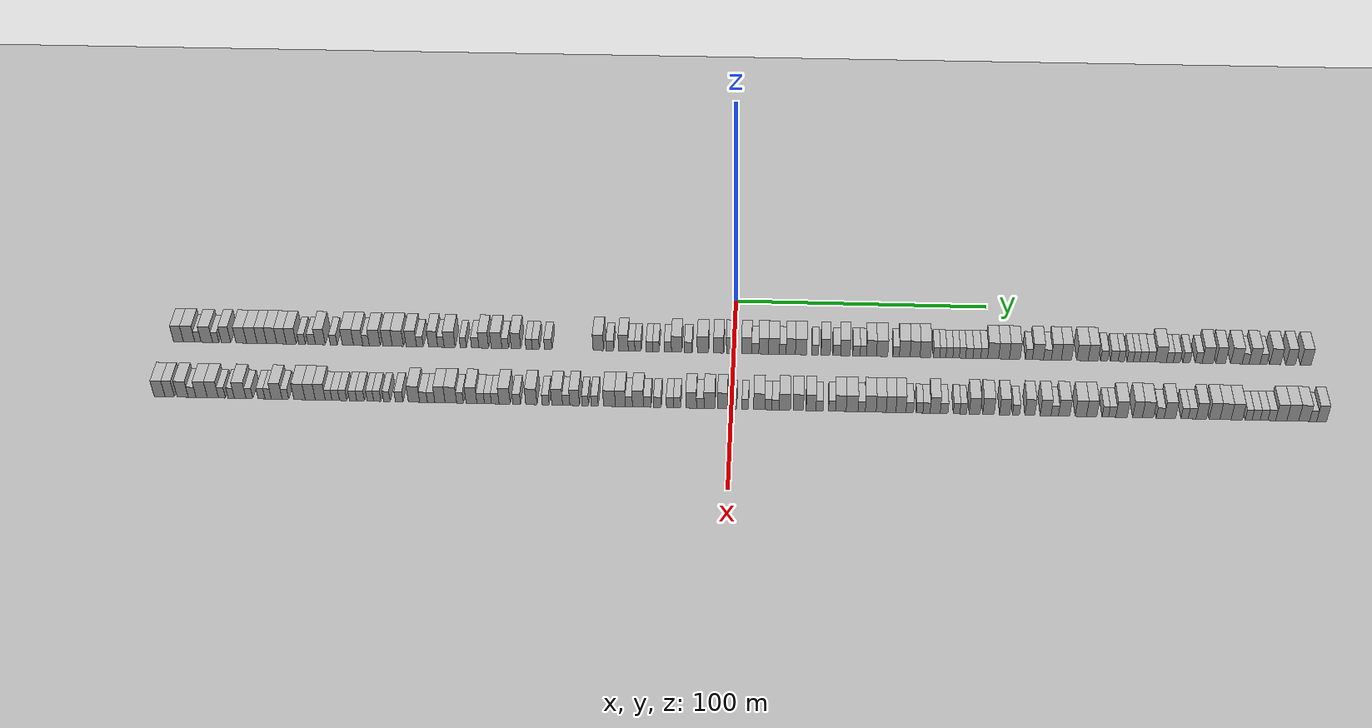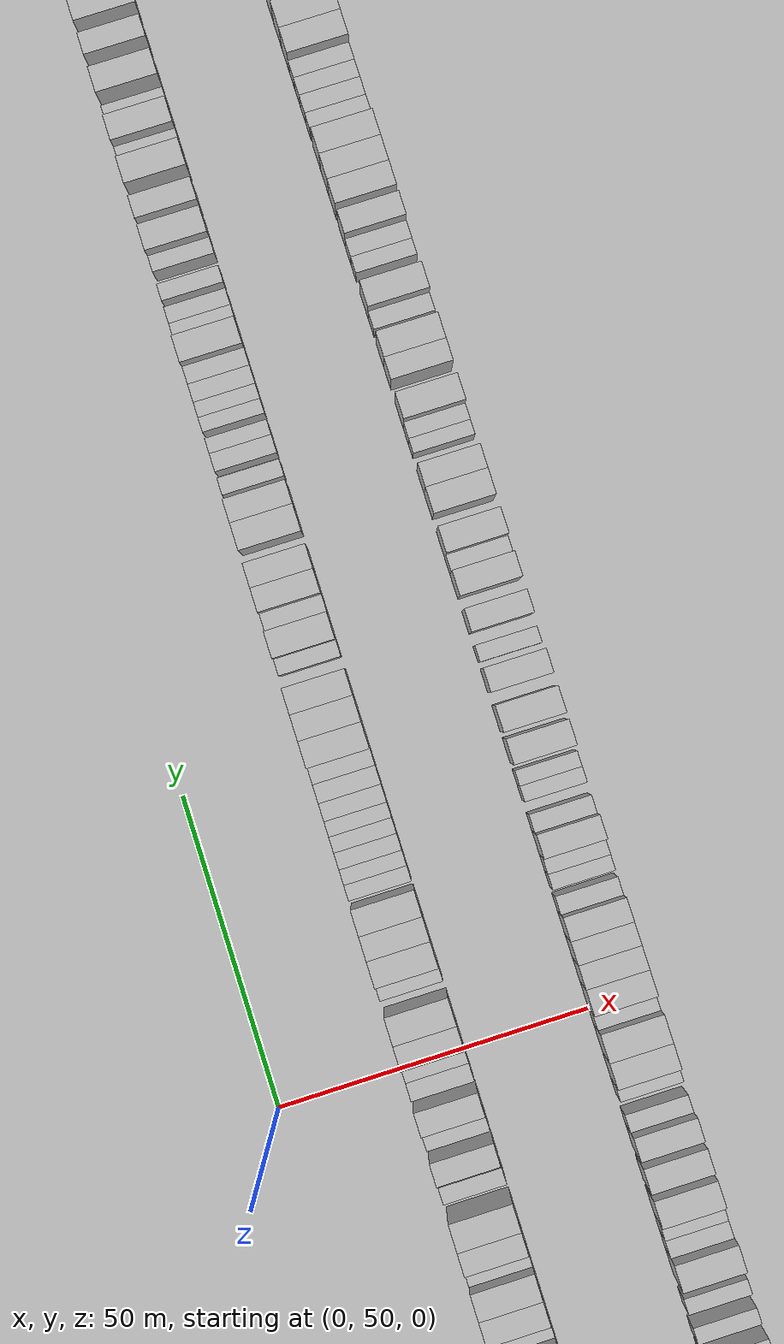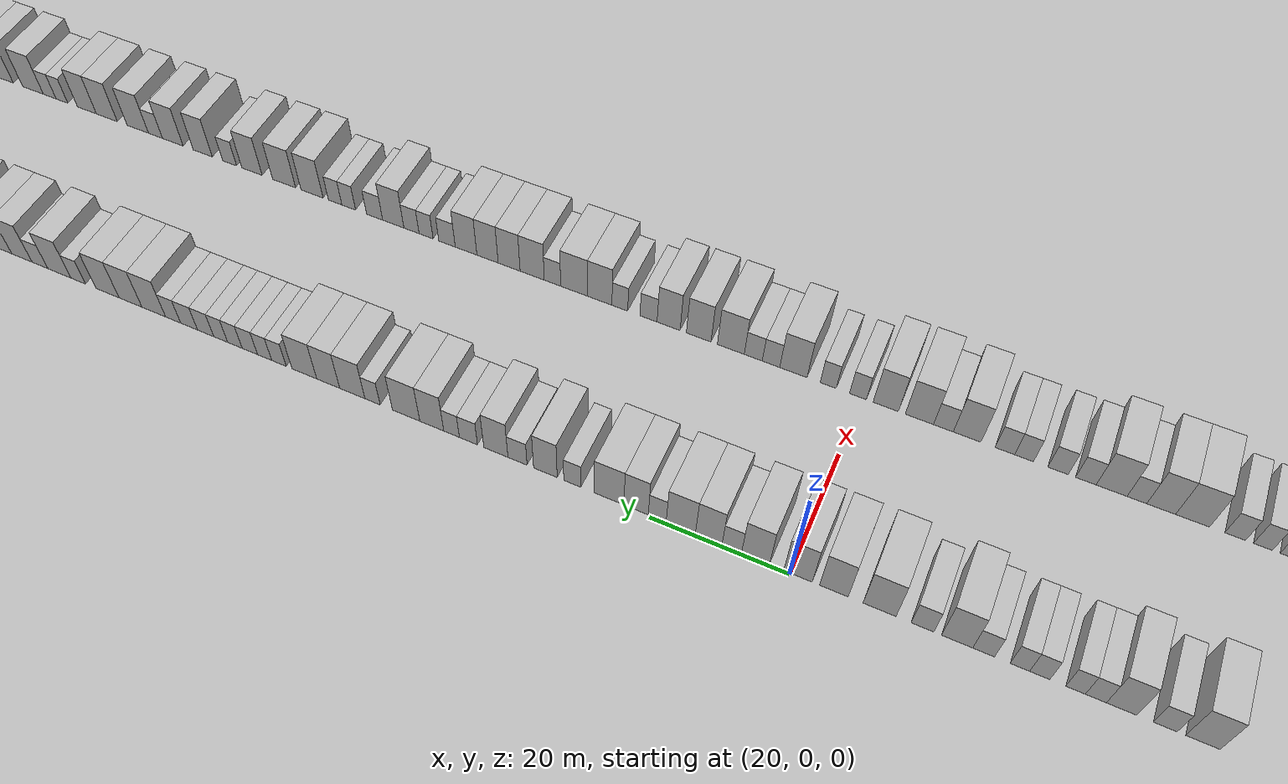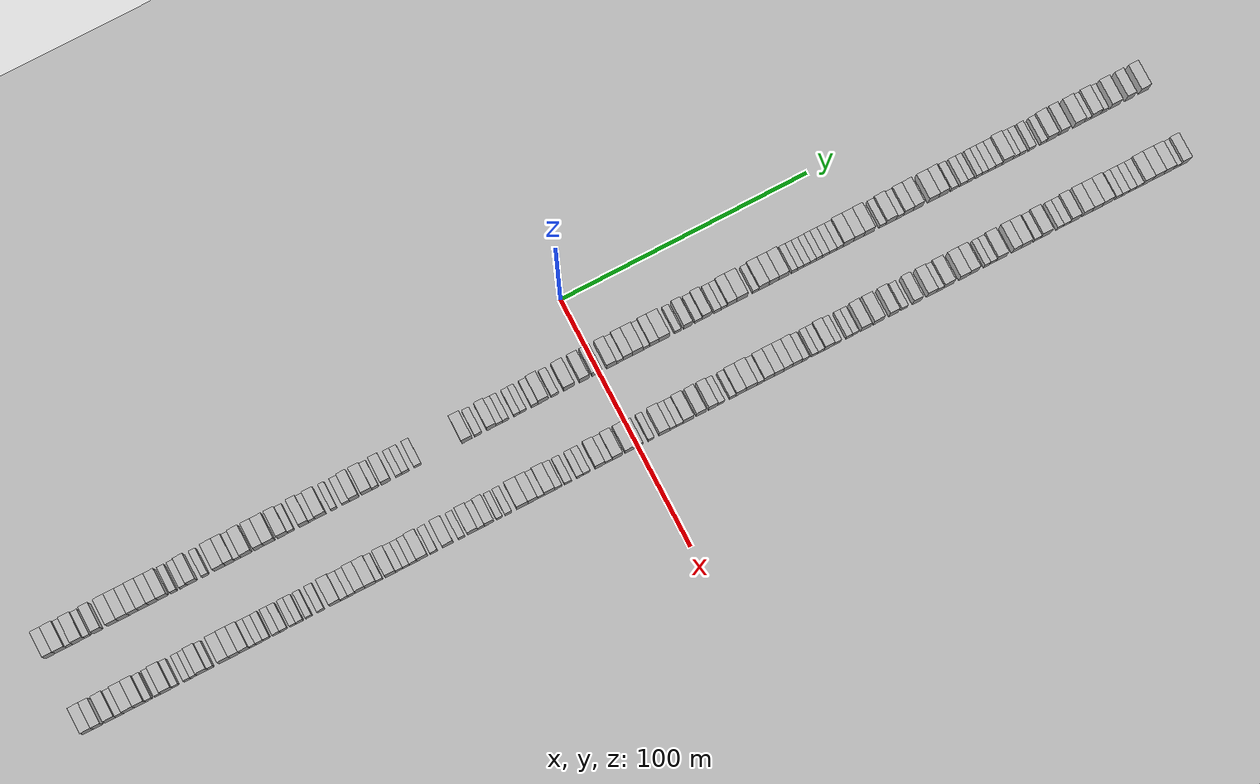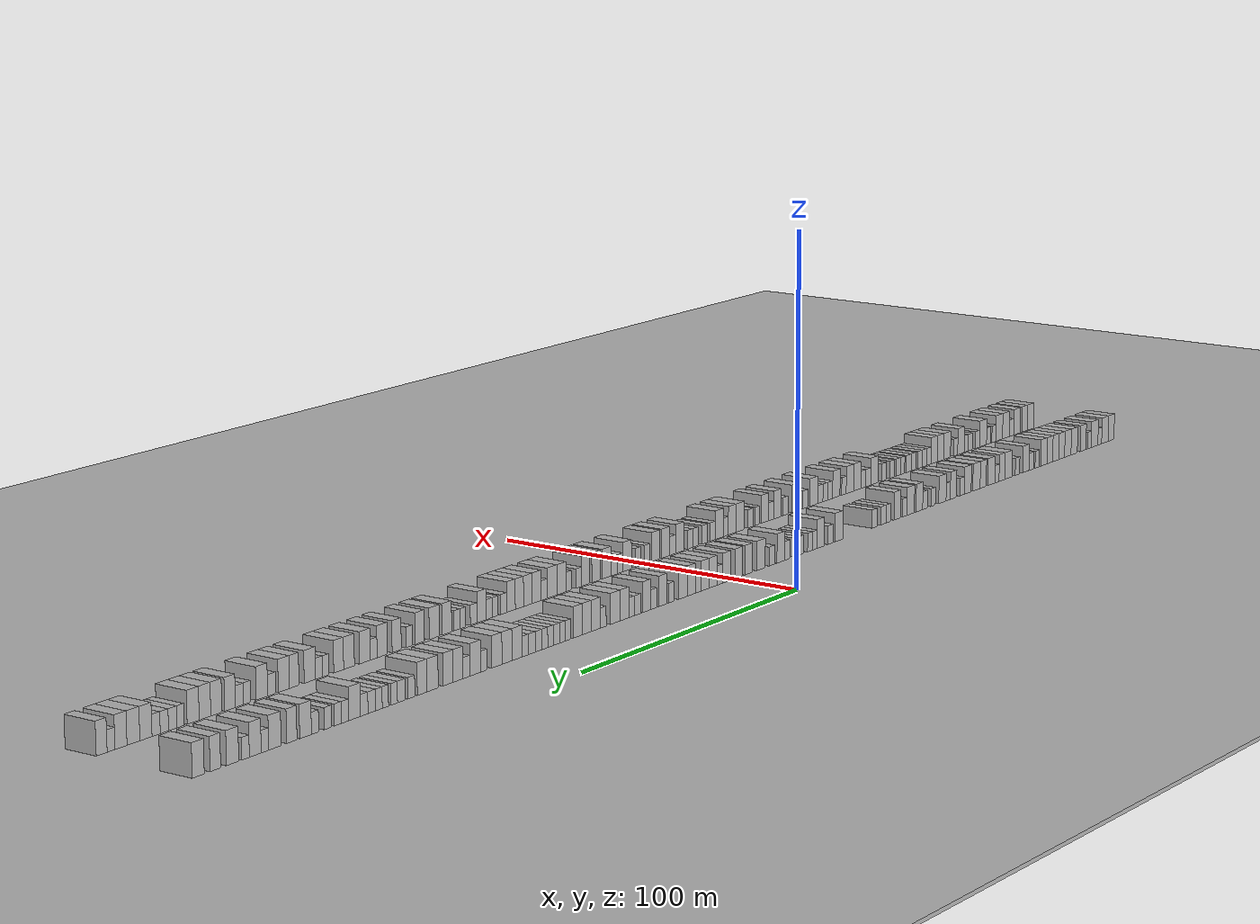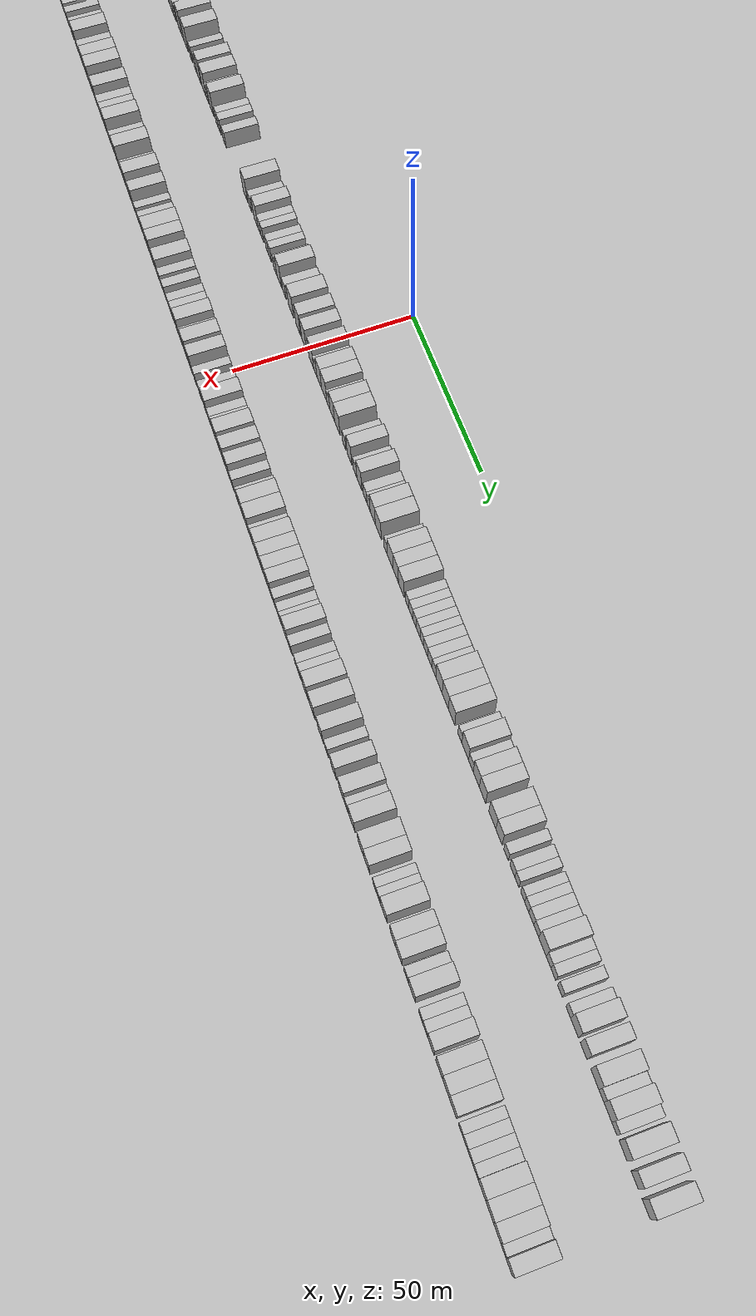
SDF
<?xml version="1.0" encoding="utf-8"?>

<sdf version="1.6">

   <world name="default">

      <gui fullscreen="0">

         <camera name="user_camera">

            <pose>-15 0 4.57585 0 0 0</pose>

            <view_controller>orbit</view_controller>

         </camera>

      </gui>

      <scene>

         <sky>

           <clouds>

             <speed>12</speed>

           </clouds>

         </sky>

         <ambient>0.4 0.4 0.4 1</ambient>

         <background>0.7 0.7 0.7 1</background>

         <shadows>1</shadows>

      </scene>

      <gravity>0 0 -9.8066</gravity>

      <magnetic_field>6e-06 2.3e-05 -4.2e-05</magnetic_field>

      <physics default="0" name="default_physics" type="ode">

         <ode>

            <solver>

               <type>quick</type>

               <iters>10</iters>

               <sor>1.0</sor>

               <use_dynamic_moi_rescaling>0</use_dynamic_moi_rescaling>

            </solver>

            <constraints>

               <cfm>0</cfm>

               <erp>0.2</erp>

               <contact_max_correcting_vel>100</contact_max_correcting_vel>

               <contact_surface_layer>0.001</contact_surface_layer>

            </constraints>

         </ode>

         <max_step_size>0.004</max_step_size>

         <real_time_factor>1</real_time_factor>

         <real_time_update_rate>250</real_time_update_rate>

      </physics>

      <light name="sun" type="directional">

         <cast_shadows>1</cast_shadows>

         <pose>0 0 10 0 0 0</pose>

         <diffuse>0.8 0.8 0.8 1</diffuse>

         <specular>0.2 0.2 0.2 1</specular>

         <attenuation>

            <range>1000</range>

            <constant>0.9</constant>

            <linear>0.01</linear>

            <quadratic>0.001</quadratic>

         </attenuation>

         <direction>-0.5 0.1 -0.9</direction>

      </light>

      <include>

         <name>ground_plane_1</name>

         <uri>model://HANNAS_ground_plane</uri>

         <pose>0 0 0  0 0 0</pose>

      </include>

      <include>

         <name>ground_plane_2</name>

         <uri>model://HANNAS_ground_plane</uri>

         <pose>100 0 0  0 0 0</pose>

      </include>

      <model name="building_1">

         <static>1</static>

         <pose frame="">25.0000 -218.0419 0 0.000000 0.000000 0.000000</pose>

         <link name="link">

            <pose frame="">0 0 4.50 0 0 0</pose>

            <collision name="collision">

               <geometry>

                  <box>

                     <size>10.0000 3.9162 9.0000</size>

                  </box>

               </geometry>

               <max_contacts>10</max_contacts>

               <surface>

                  <contact>

                     <ode/>

                  </contact>

                  <bounce/>

                  <friction>

                     <torsional>

                        <ode/>

                     </torsional>

                     <ode/>

                  </friction>

               </surface>

            </collision>

            <visual name="visual">

               <cast_shadows>0</cast_shadows>

               <geometry>

                  <box>

                     <size>10.0000 3.9162 9.0000</size>

                  </box>

               </geometry>

               <material>

                  <script>

                     <uri>model://HANNAS_wall/materials/scripts</uri>

                     <uri>model://HANNAS_wall/materials/textures</uri>

                     <name>vrc/HANNAS_wall</name>

                  </script>

               </material>

            </visual>

            <self_collide>0</self_collide>

            <enable_wind>0</enable_wind>

            <kinematic>0</kinematic>

         </link>

      </model>

      <model name="building_2">

         <static>1</static>

         <pose frame="">25.0000 -213.8533 0 0.000000 0.000000 0.000000</pose>

         <link name="link">

            <pose frame="">0 0 4.50 0 0 0</pose>

            <collision name="collision">

               <geometry>

                  <box>

                     <size>10.0000 4.4610 9.0000</size>

                  </box>

               </geometry>

               <max_contacts>10</max_contacts>

               <surface>

                  <contact>

                     <ode/>

                  </contact>

                  <bounce/>

                  <friction>

                     <torsional>

                        <ode/>

                     </torsional>

                     <ode/>

                  </friction>

               </surface>

            </collision>

            <visual name="visual">

               <cast_shadows>0</cast_shadows>

               <geometry>

                  <box>

                     <size>10.0000 4.4610 9.0000</size>

                  </box>

               </geometry>

               <material>

                  <script>

                     <uri>model://HANNAS_wall/materials/scripts</uri>

                     <uri>model://HANNAS_wall/materials/textures</uri>

                     <name>vrc/HANNAS_wall</name>

                  </script>

               </material>

            </visual>

            <self_collide>0</self_collide>

            <enable_wind>0</enable_wind>

            <kinematic>0</kinematic>

         </link>

      </model>

      <model name="building_3">

         <static>1</static>

         <pose frame="">25.0000 -210.3677 0 0.000000 0.000000 0.000000</pose>

         <link name="link">

            <pose frame="">0 0 3.00 0 0 0</pose>

            <collision name="collision">

               <geometry>

                  <box>

                     <size>10.0000 2.5101 6.0000</size>

                  </box>

               </geometry>

               <max_contacts>10</max_contacts>

               <surface>

                  <contact>

                     <ode/>

                  </contact>

                  <bounce/>

                  <friction>

                     <torsional>

                        <ode/>

                     </torsional>

                     <ode/>

                  </friction>

               </surface>

            </collision>

            <visual name="visual">

               <cast_shadows>0</cast_shadows>

               <geometry>

                  <box>

                     <size>10.0000 2.5101 6.0000</size>

                  </box>

               </geometry>

               <material>

                  <script>

                     <uri>model://HANNAS_wall/materials/scripts</uri>

                     <uri>model://HANNAS_wall/materials/textures</uri>

                     <name>vrc/HANNAS_wall</name>

                  </script>

               </material>

            </visual>

            <self_collide>0</self_collide>

            <enable_wind>0</enable_wind>

            <kinematic>0</kinematic>

         </link>

      </model>

      <model name="building_4">

         <static>1</static>

         <pose frame="">25.0000 -206.8642 0 0.000000 0.000000 0.000000</pose>

         <link name="link">

            <pose frame="">0 0 4.50 0 0 0</pose>

            <collision name="collision">

               <geometry>

                  <box>

                     <size>10.0000 4.4970 9.0000</size>

                  </box>

               </geometry>

               <max_contacts>10</max_contacts>

               <surface>

                  <contact>

                     <ode/>

                  </contact>

                  <bounce/>

                  <friction>

                     <torsional>

                        <ode/>

                     </torsional>

                     <ode/>

                  </friction>

               </surface>

            </collision>

            <visual name="visual">

               <cast_shadows>0</cast_shadows>

               <geometry>

                  <box>

                     <size>10.0000 4.4970 9.0000</size>

                  </box>

               </geometry>

               <material>

                  <script>

                     <uri>model://HANNAS_wall/materials/scripts</uri>

                     <uri>model://HANNAS_wall/materials/textures</uri>

                     <name>vrc/HANNAS_wall</name>

                  </script>

               </material>

            </visual>

            <self_collide>0</self_collide>

            <enable_wind>0</enable_wind>

            <kinematic>0</kinematic>

         </link>

      </model>

      <model name="building_5">

         <static>1</static>

         <pose frame="">25.0000 -203.3650 0 0.000000 0.000000 0.000000</pose>

         <link name="link">

            <pose frame="">0 0 3.00 0 0 0</pose>

            <collision name="collision">

               <geometry>

                  <box>

                     <size>10.0000 2.5015 6.0000</size>

                  </box>

               </geometry>

               <max_contacts>10</max_contacts>

               <surface>

                  <contact>

                     <ode/>

                  </contact>

                  <bounce/>

                  <friction>

                     <torsional>

                        <ode/>

                     </torsional>

                     <ode/>

                  </friction>

               </surface>

            </collision>

            <visual name="visual">

               <cast_shadows>0</cast_shadows>

               <geometry>

                  <box>

                     <size>10.0000 2.5015 6.0000</size>

                  </box>

               </geometry>

               <material>

                  <script>

                     <uri>model://HANNAS_wall/materials/scripts</uri>

                     <uri>model://HANNAS_wall/materials/textures</uri>

                     <name>vrc/HANNAS_wall</name>

                  </script>

               </material>

            </visual>

            <self_collide>0</self_collide>

            <enable_wind>0</enable_wind>

            <kinematic>0</kinematic>

         </link>

      </model>

      <model name="building_6">

         <static>1</static>

         <pose frame="">25.0000 -199.2475 0 0.000000 0.000000 0.000000</pose>

         <link name="link">

            <pose frame="">0 0 4.50 0 0 0</pose>

            <collision name="collision">

               <geometry>

                  <box>

                     <size>10.0000 3.7333 9.0000</size>

                  </box>

               </geometry>

               <max_contacts>10</max_contacts>

               <surface>

                  <contact>

                     <ode/>

                  </contact>

                  <bounce/>

                  <friction>

                     <torsional>

                        <ode/>

                     </torsional>

                     <ode/>

                  </friction>

               </surface>

            </collision>

            <visual name="visual">

               <cast_shadows>0</cast_shadows>

               <geometry>

                  <box>

                     <size>10.0000 3.7333 9.0000</size>

                  </box>

               </geometry>

               <material>

                  <script>

                     <uri>model://HANNAS_wall/materials/scripts</uri>

                     <uri>model://HANNAS_wall/materials/textures</uri>

                     <name>vrc/HANNAS_wall</name>

                  </script>

               </material>

            </visual>

            <self_collide>0</self_collide>

            <enable_wind>0</enable_wind>

            <kinematic>0</kinematic>

         </link>

      </model>

      <model name="building_7">

         <static>1</static>

         <pose frame="">25.0000 -193.3055 0 0.000000 0.000000 0.000000</pose>

         <link name="link">

            <pose frame="">0 0 4.50 0 0 0</pose>

            <collision name="collision">

               <geometry>

                  <box>

                     <size>10.0000 4.1508 9.0000</size>

                  </box>

               </geometry>

               <max_contacts>10</max_contacts>

               <surface>

                  <contact>

                     <ode/>

                  </contact>

                  <bounce/>

                  <friction>

                     <torsional>

                        <ode/>

                     </torsional>

                     <ode/>

                  </friction>

               </surface>

            </collision>

            <visual name="visual">

               <cast_shadows>0</cast_shadows>

               <geometry>

                  <box>

                     <size>10.0000 4.1508 9.0000</size>

                  </box>

               </geometry>

               <material>

                  <script>

                     <uri>model://HANNAS_wall/materials/scripts</uri>

                     <uri>model://HANNAS_wall/materials/textures</uri>

                     <name>vrc/HANNAS_wall</name>

                  </script>

               </material>

            </visual>

            <self_collide>0</self_collide>

            <enable_wind>0</enable_wind>

            <kinematic>0</kinematic>

         </link>

      </model>

      <model name="building_8">

         <static>1</static>

         <pose frame="">25.0000 -189.1234 0 0.000000 0.000000 0.000000</pose>

         <link name="link">

            <pose frame="">0 0 4.50 0 0 0</pose>

            <collision name="collision">

               <geometry>

                  <box>

                     <size>10.0000 4.2133 9.0000</size>

                  </box>

               </geometry>

               <max_contacts>10</max_contacts>

               <surface>

                  <contact>

                     <ode/>

                  </contact>

                  <bounce/>

                  <friction>

                     <torsional>

                        <ode/>

                     </torsional>

                     <ode/>

                  </friction>

               </surface>

            </collision>

            <visual name="visual">

               <cast_shadows>0</cast_shadows>

               <geometry>

                  <box>

                     <size>10.0000 4.2133 9.0000</size>

                  </box>

               </geometry>

               <material>

                  <script>

                     <uri>model://HANNAS_wall/materials/scripts</uri>

                     <uri>model://HANNAS_wall/materials/textures</uri>

                     <name>vrc/HANNAS_wall</name>

                  </script>

               </material>

            </visual>

            <self_collide>0</self_collide>

            <enable_wind>0</enable_wind>

            <kinematic>0</kinematic>

         </link>

      </model>

      <model name="building_9">

         <static>1</static>

         <pose frame="">25.0000 -185.1619 0 0.000000 0.000000 0.000000</pose>

         <link name="link">

            <pose frame="">0 0 4.50 0 0 0</pose>

            <collision name="collision">

               <geometry>

                  <box>

                     <size>10.0000 3.7097 9.0000</size>

                  </box>

               </geometry>

               <max_contacts>10</max_contacts>

               <surface>

                  <contact>

                     <ode/>

                  </contact>

                  <bounce/>

                  <friction>

                     <torsional>

                        <ode/>

                     </torsional>

                     <ode/>

                  </friction>

               </surface>

            </collision>

            <visual name="visual">

               <cast_shadows>0</cast_shadows>

               <geometry>

                  <box>

                     <size>10.0000 3.7097 9.0000</size>

                  </box>

               </geometry>

               <material>

                  <script>

                     <uri>model://HANNAS_wall/materials/scripts</uri>

                     <uri>model://HANNAS_wall/materials/textures</uri>

                     <name>vrc/HANNAS_wall</name>

                  </script>

               </material>

            </visual>

            <self_collide>0</self_collide>

            <enable_wind>0</enable_wind>

            <kinematic>0</kinematic>

         </link>

      </model>

      <model name="building_10">

         <static>1</static>

         <pose frame="">25.0000 -181.2895 0 0.000000 0.000000 0.000000</pose>

         <link name="link">

            <pose frame="">0 0 4.50 0 0 0</pose>

            <collision name="collision">

               <geometry>

                  <box>

                     <size>10.0000 4.0353 9.0000</size>

                  </box>

               </geometry>

               <max_contacts>10</max_contacts>

               <surface>

                  <contact>

                     <ode/>

                  </contact>

                  <bounce/>

                  <friction>

                     <torsional>

                        <ode/>

                     </torsional>

                     <ode/>

                  </friction>

               </surface>

            </collision>

            <visual name="visual">

               <cast_shadows>0</cast_shadows>

               <geometry>

                  <box>

                     <size>10.0000 4.0353 9.0000</size>

                  </box>

               </geometry>

               <material>

                  <script>

                     <uri>model://HANNAS_wall/materials/scripts</uri>

                     <uri>model://HANNAS_wall/materials/textures</uri>

                     <name>vrc/HANNAS_wall</name>

                  </script>

               </material>

            </visual>

            <self_collide>0</self_collide>

            <enable_wind>0</enable_wind>

            <kinematic>0</kinematic>

         </link>

      </model>

      <model name="building_11">

         <static>1</static>

         <pose frame="">25.0000 -177.4134 0 0.000000 0.000000 0.000000</pose>

         <link name="link">

            <pose frame="">0 0 4.50 0 0 0</pose>

            <collision name="collision">

               <geometry>

                  <box>

                     <size>10.0000 3.7169 9.0000</size>

                  </box>

               </geometry>

               <max_contacts>10</max_contacts>

               <surface>

                  <contact>

                     <ode/>

                  </contact>

                  <bounce/>

                  <friction>

                     <torsional>

                        <ode/>

                     </torsional>

                     <ode/>

                  </friction>

               </surface>

            </collision>

            <visual name="visual">

               <cast_shadows>0</cast_shadows>

               <geometry>

                  <box>

                     <size>10.0000 3.7169 9.0000</size>

                  </box>

               </geometry>

               <material>

                  <script>

                     <uri>model://HANNAS_wall/materials/scripts</uri>

                     <uri>model://HANNAS_wall/materials/textures</uri>

                     <name>vrc/HANNAS_wall</name>

                  </script>

               </material>

            </visual>

            <self_collide>0</self_collide>

            <enable_wind>0</enable_wind>

            <kinematic>0</kinematic>

         </link>

      </model>

      <model name="building_12">

         <static>1</static>

         <pose frame="">25.0000 -173.5916 0 0.000000 0.000000 0.000000</pose>

         <link name="link">

            <pose frame="">0 0 4.50 0 0 0</pose>

            <collision name="collision">

               <geometry>

                  <box>

                     <size>10.0000 3.9268 9.0000</size>

                  </box>

               </geometry>

               <max_contacts>10</max_contacts>

               <surface>

                  <contact>

                     <ode/>

                  </contact>

                  <bounce/>

                  <friction>

                     <torsional>

                        <ode/>

                     </torsional>

                     <ode/>

                  </friction>

               </surface>

            </collision>

            <visual name="visual">

               <cast_shadows>0</cast_shadows>

               <geometry>

                  <box>

                     <size>10.0000 3.9268 9.0000</size>

                  </box>

               </geometry>

               <material>

                  <script>

                     <uri>model://HANNAS_wall/materials/scripts</uri>

                     <uri>model://HANNAS_wall/materials/textures</uri>

                     <name>vrc/HANNAS_wall</name>

                  </script>

               </material>

            </visual>

            <self_collide>0</self_collide>

            <enable_wind>0</enable_wind>

            <kinematic>0</kinematic>

         </link>

      </model>

      <model name="building_13">

         <static>1</static>

         <pose frame="">25.0000 -169.3011 0 0.000000 0.000000 0.000000</pose>

         <link name="link">

            <pose frame="">0 0 3.00 0 0 0</pose>

            <collision name="collision">

               <geometry>

                  <box>

                     <size>10.0000 2.6542 6.0000</size>

                  </box>

               </geometry>

               <max_contacts>10</max_contacts>

               <surface>

                  <contact>

                     <ode/>

                  </contact>

                  <bounce/>

                  <friction>

                     <torsional>

                        <ode/>

                     </torsional>

                     <ode/>

                  </friction>

               </surface>

            </collision>

            <visual name="visual">

               <cast_shadows>0</cast_shadows>

               <geometry>

                  <box>

                     <size>10.0000 2.6542 6.0000</size>

                  </box>

               </geometry>

               <material>

                  <script>

                     <uri>model://HANNAS_wall/materials/scripts</uri>

                     <uri>model://HANNAS_wall/materials/textures</uri>

                     <name>vrc/HANNAS_wall</name>

                  </script>

               </material>

            </visual>

            <self_collide>0</self_collide>

            <enable_wind>0</enable_wind>

            <kinematic>0</kinematic>

         </link>

      </model>

      <model name="building_14">

         <static>1</static>

         <pose frame="">25.0000 -165.5096 0 0.000000 0.000000 0.000000</pose>

         <link name="link">

            <pose frame="">0 0 3.00 0 0 0</pose>

            <collision name="collision">

               <geometry>

                  <box>

                     <size>10.0000 2.9288 6.0000</size>

                  </box>

               </geometry>

               <max_contacts>10</max_contacts>

               <surface>

                  <contact>

                     <ode/>

                  </contact>

                  <bounce/>

                  <friction>

                     <torsional>

                        <ode/>

                     </torsional>

                     <ode/>

                  </friction>

               </surface>

            </collision>

            <visual name="visual">

               <cast_shadows>0</cast_shadows>

               <geometry>

                  <box>

                     <size>10.0000 2.9288 6.0000</size>

                  </box>

               </geometry>

               <material>

                  <script>

                     <uri>model://HANNAS_wall/materials/scripts</uri>

                     <uri>model://HANNAS_wall/materials/textures</uri>

                     <name>vrc/HANNAS_wall</name>

                  </script>

               </material>

            </visual>

            <self_collide>0</self_collide>

            <enable_wind>0</enable_wind>

            <kinematic>0</kinematic>

         </link>

      </model>

      <model name="building_15">

         <static>1</static>

         <pose frame="">25.0000 -162.1145 0 0.000000 0.000000 0.000000</pose>

         <link name="link">

            <pose frame="">0 0 4.50 0 0 0</pose>

            <collision name="collision">

               <geometry>

                  <box>

                     <size>10.0000 3.8613 9.0000</size>

                  </box>

               </geometry>

               <max_contacts>10</max_contacts>

               <surface>

                  <contact>

                     <ode/>

                  </contact>

                  <bounce/>

                  <friction>

                     <torsional>

                        <ode/>

                     </torsional>

                     <ode/>

                  </friction>

               </surface>

            </collision>

            <visual name="visual">

               <cast_shadows>0</cast_shadows>

               <geometry>

                  <box>

                     <size>10.0000 3.8613 9.0000</size>

                  </box>

               </geometry>

               <material>

                  <script>

                     <uri>model://HANNAS_wall/materials/scripts</uri>

                     <uri>model://HANNAS_wall/materials/textures</uri>

                     <name>vrc/HANNAS_wall</name>

                  </script>

               </material>

            </visual>

            <self_collide>0</self_collide>

            <enable_wind>0</enable_wind>

            <kinematic>0</kinematic>

         </link>

      </model>

      <model name="building_16">

         <static>1</static>

         <pose frame="">25.0000 -156.8311 0 0.000000 0.000000 0.000000</pose>

         <link name="link">

            <pose frame="">0 0 3.00 0 0 0</pose>

            <collision name="collision">

               <geometry>

                  <box>

                     <size>10.0000 2.7055 6.0000</size>

                  </box>

               </geometry>

               <max_contacts>10</max_contacts>

               <surface>

                  <contact>

                     <ode/>

                  </contact>

                  <bounce/>

                  <friction>

                     <torsional>

                        <ode/>

                     </torsional>

                     <ode/>

                  </friction>

               </surface>

            </collision>

            <visual name="visual">

               <cast_shadows>0</cast_shadows>

               <geometry>

                  <box>

                     <size>10.0000 2.7055 6.0000</size>

                  </box>

               </geometry>

               <material>

                  <script>

                     <uri>model://HANNAS_wall/materials/scripts</uri>

                     <uri>model://HANNAS_wall/materials/textures</uri>

                     <name>vrc/HANNAS_wall</name>

                  </script>

               </material>

            </visual>

            <self_collide>0</self_collide>

            <enable_wind>0</enable_wind>

            <kinematic>0</kinematic>

         </link>

      </model>

      <model name="building_17">

         <static>1</static>

         <pose frame="">25.0000 -151.2708 0 0.000000 0.000000 0.000000</pose>

         <link name="link">

            <pose frame="">0 0 4.50 0 0 0</pose>

            <collision name="collision">

               <geometry>

                  <box>

                     <size>10.0000 4.4152 9.0000</size>

                  </box>

               </geometry>

               <max_contacts>10</max_contacts>

               <surface>

                  <contact>

                     <ode/>

                  </contact>

                  <bounce/>

                  <friction>

                     <torsional>

                        <ode/>

                     </torsional>

                     <ode/>

                  </friction>

               </surface>

            </collision>

            <visual name="visual">

               <cast_shadows>0</cast_shadows>

               <geometry>

                  <box>

                     <size>10.0000 4.4152 9.0000</size>

                  </box>

               </geometry>

               <material>

                  <script>

                     <uri>model://HANNAS_wall/materials/scripts</uri>

                     <uri>model://HANNAS_wall/materials/textures</uri>

                     <name>vrc/HANNAS_wall</name>

                  </script>

               </material>

            </visual>

            <self_collide>0</self_collide>

            <enable_wind>0</enable_wind>

            <kinematic>0</kinematic>

         </link>

      </model>

      <model name="building_18">

         <static>1</static>

         <pose frame="">25.0000 -147.2323 0 0.000000 0.000000 0.000000</pose>

         <link name="link">

            <pose frame="">0 0 4.50 0 0 0</pose>

            <collision name="collision">

               <geometry>

                  <box>

                     <size>10.0000 3.6618 9.0000</size>

                  </box>

               </geometry>

               <max_contacts>10</max_contacts>

               <surface>

                  <contact>

                     <ode/>

                  </contact>

                  <bounce/>

                  <friction>

                     <torsional>

                        <ode/>

                     </torsional>

                     <ode/>

                  </friction>

               </surface>

            </collision>

            <visual name="visual">

               <cast_shadows>0</cast_shadows>

               <geometry>

                  <box>

                     <size>10.0000 3.6618 9.0000</size>

                  </box>

               </geometry>

               <material>

                  <script>

                     <uri>model://HANNAS_wall/materials/scripts</uri>

                     <uri>model://HANNAS_wall/materials/textures</uri>

                     <name>vrc/HANNAS_wall</name>

                  </script>

               </material>

            </visual>

            <self_collide>0</self_collide>

            <enable_wind>0</enable_wind>

            <kinematic>0</kinematic>

         </link>

      </model>

      <model name="building_19">

         <static>1</static>

         <pose frame="">25.0000 -144.1342 0 0.000000 0.000000 0.000000</pose>

         <link name="link">

            <pose frame="">0 0 3.00 0 0 0</pose>

            <collision name="collision">

               <geometry>

                  <box>

                     <size>10.0000 2.5345 6.0000</size>

                  </box>

               </geometry>

               <max_contacts>10</max_contacts>

               <surface>

                  <contact>

                     <ode/>

                  </contact>

                  <bounce/>

                  <friction>

                     <torsional>

                        <ode/>

                     </torsional>

                     <ode/>

                  </friction>

               </surface>

            </collision>

            <visual name="visual">

               <cast_shadows>0</cast_shadows>

               <geometry>

                  <box>

                     <size>10.0000 2.5345 6.0000</size>

                  </box>

               </geometry>

               <material>

                  <script>

                     <uri>model://HANNAS_wall/materials/scripts</uri>

                     <uri>model://HANNAS_wall/materials/textures</uri>

                     <name>vrc/HANNAS_wall</name>

                  </script>

               </material>

            </visual>

            <self_collide>0</self_collide>

            <enable_wind>0</enable_wind>

            <kinematic>0</kinematic>

         </link>

      </model>

      <model name="building_20">

         <static>1</static>

         <pose frame="">25.0000 -140.6970 0 0.000000 0.000000 0.000000</pose>

         <link name="link">

            <pose frame="">0 0 4.50 0 0 0</pose>

            <collision name="collision">

               <geometry>

                  <box>

                     <size>10.0000 4.3400 9.0000</size>

                  </box>

               </geometry>

               <max_contacts>10</max_contacts>

               <surface>

                  <contact>

                     <ode/>

                  </contact>

                  <bounce/>

                  <friction>

                     <torsional>

                        <ode/>

                     </torsional>

                     <ode/>

                  </friction>

               </surface>

            </collision>

            <visual name="visual">

               <cast_shadows>0</cast_shadows>

               <geometry>

                  <box>

                     <size>10.0000 4.3400 9.0000</size>

                  </box>

               </geometry>

               <material>

                  <script>

                     <uri>model://HANNAS_wall/materials/scripts</uri>

                     <uri>model://HANNAS_wall/materials/textures</uri>

                     <name>vrc/HANNAS_wall</name>

                  </script>

               </material>

            </visual>

            <self_collide>0</self_collide>

            <enable_wind>0</enable_wind>

            <kinematic>0</kinematic>

         </link>

      </model>

      <model name="building_21">

         <static>1</static>

         <pose frame="">25.0000 -135.6771 0 0.000000 0.000000 0.000000</pose>

         <link name="link">

            <pose frame="">0 0 4.50 0 0 0</pose>

            <collision name="collision">

               <geometry>

                  <box>

                     <size>10.0000 3.6997 9.0000</size>

                  </box>

               </geometry>

               <max_contacts>10</max_contacts>

               <surface>

                  <contact>

                     <ode/>

                  </contact>

                  <bounce/>

                  <friction>

                     <torsional>

                        <ode/>

                     </torsional>

                     <ode/>

                  </friction>

               </surface>

            </collision>

            <visual name="visual">

               <cast_shadows>0</cast_shadows>

               <geometry>

                  <box>

                     <size>10.0000 3.6997 9.0000</size>

                  </box>

               </geometry>

               <material>

                  <script>

                     <uri>model://HANNAS_wall/materials/scripts</uri>

                     <uri>model://HANNAS_wall/materials/textures</uri>

                     <name>vrc/HANNAS_wall</name>

                  </script>

               </material>

            </visual>

            <self_collide>0</self_collide>

            <enable_wind>0</enable_wind>

            <kinematic>0</kinematic>

         </link>

      </model>

      <model name="building_22">

         <static>1</static>

         <pose frame="">25.0000 -131.6127 0 0.000000 0.000000 0.000000</pose>

         <link name="link">

            <pose frame="">0 0 4.50 0 0 0</pose>

            <collision name="collision">

               <geometry>

                  <box>

                     <size>10.0000 4.4293 9.0000</size>

                  </box>

               </geometry>

               <max_contacts>10</max_contacts>

               <surface>

                  <contact>

                     <ode/>

                  </contact>

                  <bounce/>

                  <friction>

                     <torsional>

                        <ode/>

                     </torsional>

                     <ode/>

                  </friction>

               </surface>

            </collision>

            <visual name="visual">

               <cast_shadows>0</cast_shadows>

               <geometry>

                  <box>

                     <size>10.0000 4.4293 9.0000</size>

                  </box>

               </geometry>

               <material>

                  <script>

                     <uri>model://HANNAS_wall/materials/scripts</uri>

                     <uri>model://HANNAS_wall/materials/textures</uri>

                     <name>vrc/HANNAS_wall</name>

                  </script>

               </material>

            </visual>

            <self_collide>0</self_collide>

            <enable_wind>0</enable_wind>

            <kinematic>0</kinematic>

         </link>

      </model>

      <model name="building_23">

         <static>1</static>

         <pose frame="">25.0000 -126.3371 0 0.000000 0.000000 0.000000</pose>

         <link name="link">

            <pose frame="">0 0 4.50 0 0 0</pose>

            <collision name="collision">

               <geometry>

                  <box>

                     <size>10.0000 4.1219 9.0000</size>

                  </box>

               </geometry>

               <max_contacts>10</max_contacts>

               <surface>

                  <contact>

                     <ode/>

                  </contact>

                  <bounce/>

                  <friction>

                     <torsional>

                        <ode/>

                     </torsional>

                     <ode/>

                  </friction>

               </surface>

            </collision>

            <visual name="visual">

               <cast_shadows>0</cast_shadows>

               <geometry>

                  <box>

                     <size>10.0000 4.1219 9.0000</size>

                  </box>

               </geometry>

               <material>

                  <script>

                     <uri>model://HANNAS_wall/materials/scripts</uri>

                     <uri>model://HANNAS_wall/materials/textures</uri>

                     <name>vrc/HANNAS_wall</name>

                  </script>

               </material>

            </visual>

            <self_collide>0</self_collide>

            <enable_wind>0</enable_wind>

            <kinematic>0</kinematic>

         </link>

      </model>

      <model name="building_24">

         <static>1</static>

         <pose frame="">25.0000 -122.9397 0 0.000000 0.000000 0.000000</pose>

         <link name="link">

            <pose frame="">0 0 3.00 0 0 0</pose>

            <collision name="collision">

               <geometry>

                  <box>

                     <size>10.0000 2.6730 6.0000</size>

                  </box>

               </geometry>

               <max_contacts>10</max_contacts>

               <surface>

                  <contact>

                     <ode/>

                  </contact>

                  <bounce/>

                  <friction>

                     <torsional>

                        <ode/>

                     </torsional>

                     <ode/>

                  </friction>

               </surface>

            </collision>

            <visual name="visual">

               <cast_shadows>0</cast_shadows>

               <geometry>

                  <box>

                     <size>10.0000 2.6730 6.0000</size>

                  </box>

               </geometry>

               <material>

                  <script>

                     <uri>model://HANNAS_wall/materials/scripts</uri>

                     <uri>model://HANNAS_wall/materials/textures</uri>

                     <name>vrc/HANNAS_wall</name>

                  </script>

               </material>

            </visual>

            <self_collide>0</self_collide>

            <enable_wind>0</enable_wind>

            <kinematic>0</kinematic>

         </link>

      </model>

      <model name="building_25">

         <static>1</static>

         <pose frame="">25.0000 -117.7783 0 0.000000 0.000000 0.000000</pose>

         <link name="link">

            <pose frame="">0 0 4.50 0 0 0</pose>

            <collision name="collision">

               <geometry>

                  <box>

                     <size>10.0000 3.6497 9.0000</size>

                  </box>

               </geometry>

               <max_contacts>10</max_contacts>

               <surface>

                  <contact>

                     <ode/>

                  </contact>

                  <bounce/>

                  <friction>

                     <torsional>

                        <ode/>

                     </torsional>

                     <ode/>

                  </friction>

               </surface>

            </collision>

            <visual name="visual">

               <cast_shadows>0</cast_shadows>

               <geometry>

                  <box>

                     <size>10.0000 3.6497 9.0000</size>

                  </box>

               </geometry>

               <material>

                  <script>

                     <uri>model://HANNAS_wall/materials/scripts</uri>

                     <uri>model://HANNAS_wall/materials/textures</uri>

                     <name>vrc/HANNAS_wall</name>

                  </script>

               </material>

            </visual>

            <self_collide>0</self_collide>

            <enable_wind>0</enable_wind>

            <kinematic>0</kinematic>

         </link>

      </model>

      <model name="building_26">

         <static>1</static>

         <pose frame="">25.0000 -114.7021 0 0.000000 0.000000 0.000000</pose>

         <link name="link">

            <pose frame="">0 0 3.00 0 0 0</pose>

            <collision name="collision">

               <geometry>

                  <box>

                     <size>10.0000 2.5026 6.0000</size>

                  </box>

               </geometry>

               <max_contacts>10</max_contacts>

               <surface>

                  <contact>

                     <ode/>

                  </contact>

                  <bounce/>

                  <friction>

                     <torsional>

                        <ode/>

                     </torsional>

                     <ode/>

                  </friction>

               </surface>

            </collision>

            <visual name="visual">

               <cast_shadows>0</cast_shadows>

               <geometry>

                  <box>

                     <size>10.0000 2.5026 6.0000</size>

                  </box>

               </geometry>

               <material>

                  <script>

                     <uri>model://HANNAS_wall/materials/scripts</uri>

                     <uri>model://HANNAS_wall/materials/textures</uri>

                     <name>vrc/HANNAS_wall</name>

                  </script>

               </material>

            </visual>

            <self_collide>0</self_collide>

            <enable_wind>0</enable_wind>

            <kinematic>0</kinematic>

         </link>

      </model>

      <model name="building_27">

         <static>1</static>

         <pose frame="">25.0000 -111.2873 0 0.000000 0.000000 0.000000</pose>

         <link name="link">

            <pose frame="">0 0 4.50 0 0 0</pose>

            <collision name="collision">

               <geometry>

                  <box>

                     <size>10.0000 4.3269 9.0000</size>

                  </box>

               </geometry>

               <max_contacts>10</max_contacts>

               <surface>

                  <contact>

                     <ode/>

                  </contact>

                  <bounce/>

                  <friction>

                     <torsional>

                        <ode/>

                     </torsional>

                     <ode/>

                  </friction>

               </surface>

            </collision>

            <visual name="visual">

               <cast_shadows>0</cast_shadows>

               <geometry>

                  <box>

                     <size>10.0000 4.3269 9.0000</size>

                  </box>

               </geometry>

               <material>

                  <script>

                     <uri>model://HANNAS_wall/materials/scripts</uri>

                     <uri>model://HANNAS_wall/materials/textures</uri>

                     <name>vrc/HANNAS_wall</name>

                  </script>

               </material>

            </visual>

            <self_collide>0</self_collide>

            <enable_wind>0</enable_wind>

            <kinematic>0</kinematic>

         </link>

      </model>

      <model name="building_28">

         <static>1</static>

         <pose frame="">25.0000 -105.9201 0 0.000000 0.000000 0.000000</pose>

         <link name="link">

            <pose frame="">0 0 3.00 0 0 0</pose>

            <collision name="collision">

               <geometry>

                  <box>

                     <size>10.0000 2.4074 6.0000</size>

                  </box>

               </geometry>

               <max_contacts>10</max_contacts>

               <surface>

                  <contact>

                     <ode/>

                  </contact>

                  <bounce/>

                  <friction>

                     <torsional>

                        <ode/>

                     </torsional>

                     <ode/>

                  </friction>

               </surface>

            </collision>

            <visual name="visual">

               <cast_shadows>0</cast_shadows>

               <geometry>

                  <box>

                     <size>10.0000 2.4074 6.0000</size>

                  </box>

               </geometry>

               <material>

                  <script>

                     <uri>model://HANNAS_wall/materials/scripts</uri>

                     <uri>model://HANNAS_wall/materials/textures</uri>

                     <name>vrc/HANNAS_wall</name>

                  </script>

               </material>

            </visual>

            <self_collide>0</self_collide>

            <enable_wind>0</enable_wind>

            <kinematic>0</kinematic>

         </link>

      </model>

      <model name="building_29">

         <static>1</static>

         <pose frame="">25.0000 -101.2425 0 0.000000 0.000000 0.000000</pose>

         <link name="link">

            <pose frame="">0 0 3.00 0 0 0</pose>

            <collision name="collision">

               <geometry>

                  <box>

                     <size>10.0000 2.9478 6.0000</size>

                  </box>

               </geometry>

               <max_contacts>10</max_contacts>

               <surface>

                  <contact>

                     <ode/>

                  </contact>

                  <bounce/>

                  <friction>

                     <torsional>

                        <ode/>

                     </torsional>

                     <ode/>

                  </friction>

               </surface>

            </collision>

            <visual name="visual">

               <cast_shadows>0</cast_shadows>

               <geometry>

                  <box>

                     <size>10.0000 2.9478 6.0000</size>

                  </box>

               </geometry>

               <material>

                  <script>

                     <uri>model://HANNAS_wall/materials/scripts</uri>

                     <uri>model://HANNAS_wall/materials/textures</uri>

                     <name>vrc/HANNAS_wall</name>

                  </script>

               </material>

            </visual>

            <self_collide>0</self_collide>

            <enable_wind>0</enable_wind>

            <kinematic>0</kinematic>

         </link>

      </model>

      <model name="building_30">

         <static>1</static>

         <pose frame="">25.0000 -97.8844 0 0.000000 0.000000 0.000000</pose>

         <link name="link">

            <pose frame="">0 0 4.50 0 0 0</pose>

            <collision name="collision">

               <geometry>

                  <box>

                     <size>10.0000 3.7685 9.0000</size>

                  </box>

               </geometry>

               <max_contacts>10</max_contacts>

               <surface>

                  <contact>

                     <ode/>

                  </contact>

                  <bounce/>

                  <friction>

                     <torsional>

                        <ode/>

                     </torsional>

                     <ode/>

                  </friction>

               </surface>

            </collision>

            <visual name="visual">

               <cast_shadows>0</cast_shadows>

               <geometry>

                  <box>

                     <size>10.0000 3.7685 9.0000</size>

                  </box>

               </geometry>

               <material>

                  <script>

                     <uri>model://HANNAS_wall/materials/scripts</uri>

                     <uri>model://HANNAS_wall/materials/textures</uri>

                     <name>vrc/HANNAS_wall</name>

                  </script>

               </material>

            </visual>

            <self_collide>0</self_collide>

            <enable_wind>0</enable_wind>

            <kinematic>0</kinematic>

         </link>

      </model>

      <model name="building_31">

         <static>1</static>

         <pose frame="">25.0000 -92.9036 0 0.000000 0.000000 0.000000</pose>

         <link name="link">

            <pose frame="">0 0 4.50 0 0 0</pose>

            <collision name="collision">

               <geometry>

                  <box>

                     <size>10.0000 4.1931 9.0000</size>

                  </box>

               </geometry>

               <max_contacts>10</max_contacts>

               <surface>

                  <contact>

                     <ode/>

                  </contact>

                  <bounce/>

                  <friction>

                     <torsional>

                        <ode/>

                     </torsional>

                     <ode/>

                  </friction>

               </surface>

            </collision>

            <visual name="visual">

               <cast_shadows>0</cast_shadows>

               <geometry>

                  <box>

                     <size>10.0000 4.1931 9.0000</size>

                  </box>

               </geometry>

               <material>

                  <script>

                     <uri>model://HANNAS_wall/materials/scripts</uri>

                     <uri>model://HANNAS_wall/materials/textures</uri>

                     <name>vrc/HANNAS_wall</name>

                  </script>

               </material>

            </visual>

            <self_collide>0</self_collide>

            <enable_wind>0</enable_wind>

            <kinematic>0</kinematic>

         </link>

      </model>

      <model name="building_32">

         <static>1</static>

         <pose frame="">25.0000 -89.4860 0 0.000000 0.000000 0.000000</pose>

         <link name="link">

            <pose frame="">0 0 3.00 0 0 0</pose>

            <collision name="collision">

               <geometry>

                  <box>

                     <size>10.0000 2.6422 6.0000</size>

                  </box>

               </geometry>

               <max_contacts>10</max_contacts>

               <surface>

                  <contact>

                     <ode/>

                  </contact>

                  <bounce/>

                  <friction>

                     <torsional>

                        <ode/>

                     </torsional>

                     <ode/>

                  </friction>

               </surface>

            </collision>

            <visual name="visual">

               <cast_shadows>0</cast_shadows>

               <geometry>

                  <box>

                     <size>10.0000 2.6422 6.0000</size>

                  </box>

               </geometry>

               <material>

                  <script>

                     <uri>model://HANNAS_wall/materials/scripts</uri>

                     <uri>model://HANNAS_wall/materials/textures</uri>

                     <name>vrc/HANNAS_wall</name>

                  </script>

               </material>

            </visual>

            <self_collide>0</self_collide>

            <enable_wind>0</enable_wind>

            <kinematic>0</kinematic>

         </link>

      </model>

      <model name="building_33">

         <static>1</static>

         <pose frame="">25.0000 -85.2763 0 0.000000 0.000000 0.000000</pose>

         <link name="link">

            <pose frame="">0 0 4.50 0 0 0</pose>

            <collision name="collision">

               <geometry>

                  <box>

                     <size>10.0000 3.7771 9.0000</size>

                  </box>

               </geometry>

               <max_contacts>10</max_contacts>

               <surface>

                  <contact>

                     <ode/>

                  </contact>

                  <bounce/>

                  <friction>

                     <torsional>

                        <ode/>

                     </torsional>

                     <ode/>

                  </friction>

               </surface>

            </collision>

            <visual name="visual">

               <cast_shadows>0</cast_shadows>

               <geometry>

                  <box>

                     <size>10.0000 3.7771 9.0000</size>

                  </box>

               </geometry>

               <material>

                  <script>

                     <uri>model://HANNAS_wall/materials/scripts</uri>

                     <uri>model://HANNAS_wall/materials/textures</uri>

                     <name>vrc/HANNAS_wall</name>

                  </script>

               </material>

            </visual>

            <self_collide>0</self_collide>

            <enable_wind>0</enable_wind>

            <kinematic>0</kinematic>

         </link>

      </model>

      <model name="building_34">

         <static>1</static>

         <pose frame="">25.0000 -80.1502 0 0.000000 0.000000 0.000000</pose>

         <link name="link">

            <pose frame="">0 0 3.00 0 0 0</pose>

            <collision name="collision">

               <geometry>

                  <box>

                     <size>10.0000 2.4752 6.0000</size>

                  </box>

               </geometry>

               <max_contacts>10</max_contacts>

               <surface>

                  <contact>

                     <ode/>

                  </contact>

                  <bounce/>

                  <friction>

                     <torsional>

                        <ode/>

                     </torsional>

                     <ode/>

                  </friction>

               </surface>

            </collision>

            <visual name="visual">

               <cast_shadows>0</cast_shadows>

               <geometry>

                  <box>

                     <size>10.0000 2.4752 6.0000</size>

                  </box>

               </geometry>

               <material>

                  <script>

                     <uri>model://HANNAS_wall/materials/scripts</uri>

                     <uri>model://HANNAS_wall/materials/textures</uri>

                     <name>vrc/HANNAS_wall</name>

                  </script>

               </material>

            </visual>

            <self_collide>0</self_collide>

            <enable_wind>0</enable_wind>

            <kinematic>0</kinematic>

         </link>

      </model>

      <model name="building_35">

         <static>1</static>

         <pose frame="">25.0000 -77.5133 0 0.000000 0.000000 0.000000</pose>

         <link name="link">

            <pose frame="">0 0 3.00 0 0 0</pose>

            <collision name="collision">

               <geometry>

                  <box>

                     <size>10.0000 2.7986 6.0000</size>

                  </box>

               </geometry>

               <max_contacts>10</max_contacts>

               <surface>

                  <contact>

                     <ode/>

                  </contact>

                  <bounce/>

                  <friction>

                     <torsional>

                        <ode/>

                     </torsional>

                     <ode/>

                  </friction>

               </surface>

            </collision>

            <visual name="visual">

               <cast_shadows>0</cast_shadows>

               <geometry>

                  <box>

                     <size>10.0000 2.7986 6.0000</size>

                  </box>

               </geometry>

               <material>

                  <script>

                     <uri>model://HANNAS_wall/materials/scripts</uri>

                     <uri>model://HANNAS_wall/materials/textures</uri>

                     <name>vrc/HANNAS_wall</name>

                  </script>

               </material>

            </visual>

            <self_collide>0</self_collide>

            <enable_wind>0</enable_wind>

            <kinematic>0</kinematic>

         </link>

      </model>

      <model name="building_36">

         <static>1</static>

         <pose frame="">25.0000 -72.6482 0 0.000000 0.000000 0.000000</pose>

         <link name="link">

            <pose frame="">0 0 3.00 0 0 0</pose>

            <collision name="collision">

               <geometry>

                  <box>

                     <size>10.0000 2.9316 6.0000</size>

                  </box>

               </geometry>

               <max_contacts>10</max_contacts>

               <surface>

                  <contact>

                     <ode/>

                  </contact>

                  <bounce/>

                  <friction>

                     <torsional>

                        <ode/>

                     </torsional>

                     <ode/>

                  </friction>

               </surface>

            </collision>

            <visual name="visual">

               <cast_shadows>0</cast_shadows>

               <geometry>

                  <box>

                     <size>10.0000 2.9316 6.0000</size>

                  </box>

               </geometry>

               <material>

                  <script>

                     <uri>model://HANNAS_wall/materials/scripts</uri>

                     <uri>model://HANNAS_wall/materials/textures</uri>

                     <name>vrc/HANNAS_wall</name>

                  </script>

               </material>

            </visual>

            <self_collide>0</self_collide>

            <enable_wind>0</enable_wind>

            <kinematic>0</kinematic>

         </link>

      </model>

      <model name="building_37">

         <static>1</static>

         <pose frame="">25.0000 -53.0157 0 0.000000 0.000000 0.000000</pose>

         <link name="link">

            <pose frame="">0 0 4.50 0 0 0</pose>

            <collision name="collision">

               <geometry>

                  <box>

                     <size>10.0000 4.1112 9.0000</size>

                  </box>

               </geometry>

               <max_contacts>10</max_contacts>

               <surface>

                  <contact>

                     <ode/>

                  </contact>

                  <bounce/>

                  <friction>

                     <torsional>

                        <ode/>

                     </torsional>

                     <ode/>

                  </friction>

               </surface>

            </collision>

            <visual name="visual">

               <cast_shadows>0</cast_shadows>

               <geometry>

                  <box>

                     <size>10.0000 4.1112 9.0000</size>

                  </box>

               </geometry>

               <material>

                  <script>

                     <uri>model://HANNAS_wall/materials/scripts</uri>

                     <uri>model://HANNAS_wall/materials/textures</uri>

                     <name>vrc/HANNAS_wall</name>

                  </script>

               </material>

            </visual>

            <self_collide>0</self_collide>

            <enable_wind>0</enable_wind>

            <kinematic>0</kinematic>

         </link>

      </model>

      <model name="building_38">

         <static>1</static>

         <pose frame="">25.0000 -48.5144 0 0.000000 0.000000 0.000000</pose>

         <link name="link">

            <pose frame="">0 0 3.00 0 0 0</pose>

            <collision name="collision">

               <geometry>

                  <box>

                     <size>10.0000 2.8913 6.0000</size>

                  </box>

               </geometry>

               <max_contacts>10</max_contacts>

               <surface>

                  <contact>

                     <ode/>

                  </contact>

                  <bounce/>

                  <friction>

                     <torsional>

                        <ode/>

                     </torsional>

                     <ode/>

                  </friction>

               </surface>

            </collision>

            <visual name="visual">

               <cast_shadows>0</cast_shadows>

               <geometry>

                  <box>

                     <size>10.0000 2.8913 6.0000</size>

                  </box>

               </geometry>

               <material>

                  <script>

                     <uri>model://HANNAS_wall/materials/scripts</uri>

                     <uri>model://HANNAS_wall/materials/textures</uri>

                     <name>vrc/HANNAS_wall</name>

                  </script>

               </material>

            </visual>

            <self_collide>0</self_collide>

            <enable_wind>0</enable_wind>

            <kinematic>0</kinematic>

         </link>

      </model>

      <model name="building_39">

         <static>1</static>

         <pose frame="">25.0000 -43.2031 0 0.000000 0.000000 0.000000</pose>

         <link name="link">

            <pose frame="">0 0 4.50 0 0 0</pose>

            <collision name="collision">

               <geometry>

                  <box>

                     <size>10.0000 3.7314 9.0000</size>

                  </box>

               </geometry>

               <max_contacts>10</max_contacts>

               <surface>

                  <contact>

                     <ode/>

                  </contact>

                  <bounce/>

                  <friction>

                     <torsional>

                        <ode/>

                     </torsional>

                     <ode/>

                  </friction>

               </surface>

            </collision>

            <visual name="visual">

               <cast_shadows>0</cast_shadows>

               <geometry>

                  <box>

                     <size>10.0000 3.7314 9.0000</size>

                  </box>

               </geometry>

               <material>

                  <script>

                     <uri>model://HANNAS_wall/materials/scripts</uri>

                     <uri>model://HANNAS_wall/materials/textures</uri>

                     <name>vrc/HANNAS_wall</name>

                  </script>

               </material>

            </visual>

            <self_collide>0</self_collide>

            <enable_wind>0</enable_wind>

            <kinematic>0</kinematic>

         </link>

      </model>

      <model name="building_40">

         <static>1</static>

         <pose frame="">25.0000 -40.0389 0 0.000000 0.000000 0.000000</pose>

         <link name="link">

            <pose frame="">0 0 3.00 0 0 0</pose>

            <collision name="collision">

               <geometry>

                  <box>

                     <size>10.0000 2.5972 6.0000</size>

                  </box>

               </geometry>

               <max_contacts>10</max_contacts>

               <surface>

                  <contact>

                     <ode/>

                  </contact>

                  <bounce/>

                  <friction>

                     <torsional>

                        <ode/>

                     </torsional>

                     <ode/>

                  </friction>

               </surface>

            </collision>

            <visual name="visual">

               <cast_shadows>0</cast_shadows>

               <geometry>

                  <box>

                     <size>10.0000 2.5972 6.0000</size>

                  </box>

               </geometry>

               <material>

                  <script>

                     <uri>model://HANNAS_wall/materials/scripts</uri>

                     <uri>model://HANNAS_wall/materials/textures</uri>

                     <name>vrc/HANNAS_wall</name>

                  </script>

               </material>

            </visual>

            <self_collide>0</self_collide>

            <enable_wind>0</enable_wind>

            <kinematic>0</kinematic>

         </link>

      </model>

      <model name="building_41">

         <static>1</static>

         <pose frame="">25.0000 -37.5212 0 0.000000 0.000000 0.000000</pose>

         <link name="link">

            <pose frame="">0 0 3.00 0 0 0</pose>

            <collision name="collision">

               <geometry>

                  <box>

                     <size>10.0000 2.4381 6.0000</size>

                  </box>

               </geometry>

               <max_contacts>10</max_contacts>

               <surface>

                  <contact>

                     <ode/>

                  </contact>

                  <bounce/>

                  <friction>

                     <torsional>

                        <ode/>

                     </torsional>

                     <ode/>

                  </friction>

               </surface>

            </collision>

            <visual name="visual">

               <cast_shadows>0</cast_shadows>

               <geometry>

                  <box>

                     <size>10.0000 2.4381 6.0000</size>

                  </box>

               </geometry>

               <material>

                  <script>

                     <uri>model://HANNAS_wall/materials/scripts</uri>

                     <uri>model://HANNAS_wall/materials/textures</uri>

                     <name>vrc/HANNAS_wall</name>

                  </script>

               </material>

            </visual>

            <self_collide>0</self_collide>

            <enable_wind>0</enable_wind>

            <kinematic>0</kinematic>

         </link>

      </model>

      <model name="building_42">

         <static>1</static>

         <pose frame="">25.0000 -33.0255 0 0.000000 0.000000 0.000000</pose>

         <link name="link">

            <pose frame="">0 0 3.00 0 0 0</pose>

            <collision name="collision">

               <geometry>

                  <box>

                     <size>10.0000 2.5532 6.0000</size>

                  </box>

               </geometry>

               <max_contacts>10</max_contacts>

               <surface>

                  <contact>

                     <ode/>

                  </contact>

                  <bounce/>

                  <friction>

                     <torsional>

                        <ode/>

                     </torsional>

                     <ode/>

                  </friction>

               </surface>

            </collision>

            <visual name="visual">

               <cast_shadows>0</cast_shadows>

               <geometry>

                  <box>

                     <size>10.0000 2.5532 6.0000</size>

                  </box>

               </geometry>

               <material>

                  <script>

                     <uri>model://HANNAS_wall/materials/scripts</uri>

                     <uri>model://HANNAS_wall/materials/textures</uri>

                     <name>vrc/HANNAS_wall</name>

                  </script>

               </material>

            </visual>

            <self_collide>0</self_collide>

            <enable_wind>0</enable_wind>

            <kinematic>0</kinematic>

         </link>

      </model>

      <model name="building_43">

         <static>1</static>

         <pose frame="">25.0000 -30.5121 0 0.000000 0.000000 0.000000</pose>

         <link name="link">

            <pose frame="">0 0 3.00 0 0 0</pose>

            <collision name="collision">

               <geometry>

                  <box>

                     <size>10.0000 2.4736 6.0000</size>

                  </box>

               </geometry>

               <max_contacts>10</max_contacts>

               <surface>

                  <contact>

                     <ode/>

                  </contact>

                  <bounce/>

                  <friction>

                     <torsional>

                        <ode/>

                     </torsional>

                     <ode/>

                  </friction>

               </surface>

            </collision>

            <visual name="visual">

               <cast_shadows>0</cast_shadows>

               <geometry>

                  <box>

                     <size>10.0000 2.4736 6.0000</size>

                  </box>

               </geometry>

               <material>

                  <script>

                     <uri>model://HANNAS_wall/materials/scripts</uri>

                     <uri>model://HANNAS_wall/materials/textures</uri>

                     <name>vrc/HANNAS_wall</name>

                  </script>

               </material>

            </visual>

            <self_collide>0</self_collide>

            <enable_wind>0</enable_wind>

            <kinematic>0</kinematic>

         </link>

      </model>

      <model name="building_44">

         <static>1</static>

         <pose frame="">25.0000 -25.8657 0 0.000000 0.000000 0.000000</pose>

         <link name="link">

            <pose frame="">0 0 3.00 0 0 0</pose>

            <collision name="collision">

               <geometry>

                  <box>

                     <size>10.0000 2.8192 6.0000</size>

                  </box>

               </geometry>

               <max_contacts>10</max_contacts>

               <surface>

                  <contact>

                     <ode/>

                  </contact>

                  <bounce/>

                  <friction>

                     <torsional>

                        <ode/>

                     </torsional>

                     <ode/>

                  </friction>

               </surface>

            </collision>

            <visual name="visual">

               <cast_shadows>0</cast_shadows>

               <geometry>

                  <box>

                     <size>10.0000 2.8192 6.0000</size>

                  </box>

               </geometry>

               <material>

                  <script>

                     <uri>model://HANNAS_wall/materials/scripts</uri>

                     <uri>model://HANNAS_wall/materials/textures</uri>

                     <name>vrc/HANNAS_wall</name>

                  </script>

               </material>

            </visual>

            <self_collide>0</self_collide>

            <enable_wind>0</enable_wind>

            <kinematic>0</kinematic>

         </link>

      </model>

      <model name="building_45">

         <static>1</static>

         <pose frame="">25.0000 -22.4198 0 0.000000 0.000000 0.000000</pose>

         <link name="link">

            <pose frame="">0 0 4.50 0 0 0</pose>

            <collision name="collision">

               <geometry>

                  <box>

                     <size>10.0000 4.0725 9.0000</size>

                  </box>

               </geometry>

               <max_contacts>10</max_contacts>

               <surface>

                  <contact>

                     <ode/>

                  </contact>

                  <bounce/>

                  <friction>

                     <torsional>

                        <ode/>

                     </torsional>

                     <ode/>

                  </friction>

               </surface>

            </collision>

            <visual name="visual">

               <cast_shadows>0</cast_shadows>

               <geometry>

                  <box>

                     <size>10.0000 4.0725 9.0000</size>

                  </box>

               </geometry>

               <material>

                  <script>

                     <uri>model://HANNAS_wall/materials/scripts</uri>

                     <uri>model://HANNAS_wall/materials/textures</uri>

                     <name>vrc/HANNAS_wall</name>

                  </script>

               </material>

            </visual>

            <self_collide>0</self_collide>

            <enable_wind>0</enable_wind>

            <kinematic>0</kinematic>

         </link>

      </model>

      <model name="building_46">

         <static>1</static>

         <pose frame="">25.0000 -17.8843 0 0.000000 0.000000 0.000000</pose>

         <link name="link">

            <pose frame="">0 0 3.00 0 0 0</pose>

            <collision name="collision">

               <geometry>

                  <box>

                     <size>10.0000 2.9986 6.0000</size>

                  </box>

               </geometry>

               <max_contacts>10</max_contacts>

               <surface>

                  <contact>

                     <ode/>

                  </contact>

                  <bounce/>

                  <friction>

                     <torsional>

                        <ode/>

                     </torsional>

                     <ode/>

                  </friction>

               </surface>

            </collision>

            <visual name="visual">

               <cast_shadows>0</cast_shadows>

               <geometry>

                  <box>

                     <size>10.0000 2.9986 6.0000</size>

                  </box>

               </geometry>

               <material>

                  <script>

                     <uri>model://HANNAS_wall/materials/scripts</uri>

                     <uri>model://HANNAS_wall/materials/textures</uri>

                     <name>vrc/HANNAS_wall</name>

                  </script>

               </material>

            </visual>

            <self_collide>0</self_collide>

            <enable_wind>0</enable_wind>

            <kinematic>0</kinematic>

         </link>

      </model>

      <model name="building_47">

         <static>1</static>

         <pose frame="">25.0000 -12.1722 0 0.000000 0.000000 0.000000</pose>

         <link name="link">

            <pose frame="">0 0 4.50 0 0 0</pose>

            <collision name="collision">

               <geometry>

                  <box>

                     <size>10.0000 4.4255 9.0000</size>

                  </box>

               </geometry>

               <max_contacts>10</max_contacts>

               <surface>

                  <contact>

                     <ode/>

                  </contact>

                  <bounce/>

                  <friction>

                     <torsional>

                        <ode/>

                     </torsional>

                     <ode/>

                  </friction>

               </surface>

            </collision>

            <visual name="visual">

               <cast_shadows>0</cast_shadows>

               <geometry>

                  <box>

                     <size>10.0000 4.4255 9.0000</size>

                  </box>

               </geometry>

               <material>

                  <script>

                     <uri>model://HANNAS_wall/materials/scripts</uri>

                     <uri>model://HANNAS_wall/materials/textures</uri>

                     <name>vrc/HANNAS_wall</name>

                  </script>

               </material>

            </visual>

            <self_collide>0</self_collide>

            <enable_wind>0</enable_wind>

            <kinematic>0</kinematic>

         </link>

      </model>

      <model name="building_48">

         <static>1</static>

         <pose frame="">25.0000 -5.9985 0 0.000000 0.000000 0.000000</pose>

         <link name="link">

            <pose frame="">0 0 4.50 0 0 0</pose>

            <collision name="collision">

               <geometry>

                  <box>

                     <size>10.0000 3.9220 9.0000</size>

                  </box>

               </geometry>

               <max_contacts>10</max_contacts>

               <surface>

                  <contact>

                     <ode/>

                  </contact>

                  <bounce/>

                  <friction>

                     <torsional>

                        <ode/>

                     </torsional>

                     <ode/>

                  </friction>

               </surface>

            </collision>

            <visual name="visual">

               <cast_shadows>0</cast_shadows>

               <geometry>

                  <box>

                     <size>10.0000 3.9220 9.0000</size>

                  </box>

               </geometry>

               <material>

                  <script>

                     <uri>model://HANNAS_wall/materials/scripts</uri>

                     <uri>model://HANNAS_wall/materials/textures</uri>

                     <name>vrc/HANNAS_wall</name>

                  </script>

               </material>

            </visual>

            <self_collide>0</self_collide>

            <enable_wind>0</enable_wind>

            <kinematic>0</kinematic>

         </link>

      </model>

      <model name="building_49">

         <static>1</static>

         <pose frame="">25.0000 -1.0653 0 0.000000 0.000000 0.000000</pose>

         <link name="link">

            <pose frame="">0 0 4.50 0 0 0</pose>

            <collision name="collision">

               <geometry>

                  <box>

                     <size>10.0000 3.9443 9.0000</size>

                  </box>

               </geometry>

               <max_contacts>10</max_contacts>

               <surface>

                  <contact>

                     <ode/>

                  </contact>

                  <bounce/>

                  <friction>

                     <torsional>

                        <ode/>

                     </torsional>

                     <ode/>

                  </friction>

               </surface>

            </collision>

            <visual name="visual">

               <cast_shadows>0</cast_shadows>

               <geometry>

                  <box>

                     <size>10.0000 3.9443 9.0000</size>

                  </box>

               </geometry>

               <material>

                  <script>

                     <uri>model://HANNAS_wall/materials/scripts</uri>

                     <uri>model://HANNAS_wall/materials/textures</uri>

                     <name>vrc/HANNAS_wall</name>

                  </script>

               </material>

            </visual>

            <self_collide>0</self_collide>

            <enable_wind>0</enable_wind>

            <kinematic>0</kinematic>

         </link>

      </model>

      <model name="building_50">

         <static>1</static>

         <pose frame="">25.0000 4.8676 0 0.000000 0.000000 0.000000</pose>

         <link name="link">

            <pose frame="">0 0 4.50 0 0 0</pose>

            <collision name="collision">

               <geometry>

                  <box>

                     <size>10.0000 3.9215 9.0000</size>

                  </box>

               </geometry>

               <max_contacts>10</max_contacts>

               <surface>

                  <contact>

                     <ode/>

                  </contact>

                  <bounce/>

                  <friction>

                     <torsional>

                        <ode/>

                     </torsional>

                     <ode/>

                  </friction>

               </surface>

            </collision>

            <visual name="visual">

               <cast_shadows>0</cast_shadows>

               <geometry>

                  <box>

                     <size>10.0000 3.9215 9.0000</size>

                  </box>

               </geometry>

               <material>

                  <script>

                     <uri>model://HANNAS_wall/materials/scripts</uri>

                     <uri>model://HANNAS_wall/materials/textures</uri>

                     <name>vrc/HANNAS_wall</name>

                  </script>

               </material>

            </visual>

            <self_collide>0</self_collide>

            <enable_wind>0</enable_wind>

            <kinematic>0</kinematic>

         </link>

      </model>

      <model name="building_51">

         <static>1</static>

         <pose frame="">25.0000 8.2137 0 0.000000 0.000000 0.000000</pose>

         <link name="link">

            <pose frame="">0 0 3.00 0 0 0</pose>

            <collision name="collision">

               <geometry>

                  <box>

                     <size>10.0000 2.7707 6.0000</size>

                  </box>

               </geometry>

               <max_contacts>10</max_contacts>

               <surface>

                  <contact>

                     <ode/>

                  </contact>

                  <bounce/>

                  <friction>

                     <torsional>

                        <ode/>

                     </torsional>

                     <ode/>

                  </friction>

               </surface>

            </collision>

            <visual name="visual">

               <cast_shadows>0</cast_shadows>

               <geometry>

                  <box>

                     <size>10.0000 2.7707 6.0000</size>

                  </box>

               </geometry>

               <material>

                  <script>

                     <uri>model://HANNAS_wall/materials/scripts</uri>

                     <uri>model://HANNAS_wall/materials/textures</uri>

                     <name>vrc/HANNAS_wall</name>

                  </script>

               </material>

            </visual>

            <self_collide>0</self_collide>

            <enable_wind>0</enable_wind>

            <kinematic>0</kinematic>

         </link>

      </model>

      <model name="building_52">

         <static>1</static>

         <pose frame="">25.0000 11.5132 0 0.000000 0.000000 0.000000</pose>

         <link name="link">

            <pose frame="">0 0 4.50 0 0 0</pose>

            <collision name="collision">

               <geometry>

                  <box>

                     <size>10.0000 3.8282 9.0000</size>

                  </box>

               </geometry>

               <max_contacts>10</max_contacts>

               <surface>

                  <contact>

                     <ode/>

                  </contact>

                  <bounce/>

                  <friction>

                     <torsional>

                        <ode/>

                     </torsional>

                     <ode/>

                  </friction>

               </surface>

            </collision>

            <visual name="visual">

               <cast_shadows>0</cast_shadows>

               <geometry>

                  <box>

                     <size>10.0000 3.8282 9.0000</size>

                  </box>

               </geometry>

               <material>

                  <script>

                     <uri>model://HANNAS_wall/materials/scripts</uri>

                     <uri>model://HANNAS_wall/materials/textures</uri>

                     <name>vrc/HANNAS_wall</name>

                  </script>

               </material>

            </visual>

            <self_collide>0</self_collide>

            <enable_wind>0</enable_wind>

            <kinematic>0</kinematic>

         </link>

      </model>

      <model name="building_53">

         <static>1</static>

         <pose frame="">25.0000 15.5393 0 0.000000 0.000000 0.000000</pose>

         <link name="link">

            <pose frame="">0 0 4.50 0 0 0</pose>

            <collision name="collision">

               <geometry>

                  <box>

                     <size>10.0000 4.2240 9.0000</size>

                  </box>

               </geometry>

               <max_contacts>10</max_contacts>

               <surface>

                  <contact>

                     <ode/>

                  </contact>

                  <bounce/>

                  <friction>

                     <torsional>

                        <ode/>

                     </torsional>

                     <ode/>

                  </friction>

               </surface>

            </collision>

            <visual name="visual">

               <cast_shadows>0</cast_shadows>

               <geometry>

                  <box>

                     <size>10.0000 4.2240 9.0000</size>

                  </box>

               </geometry>

               <material>

                  <script>

                     <uri>model://HANNAS_wall/materials/scripts</uri>

                     <uri>model://HANNAS_wall/materials/textures</uri>

                     <name>vrc/HANNAS_wall</name>

                  </script>

               </material>

            </visual>

            <self_collide>0</self_collide>

            <enable_wind>0</enable_wind>

            <kinematic>0</kinematic>

         </link>

      </model>

      <model name="building_54">

         <static>1</static>

         <pose frame="">25.0000 18.9498 0 0.000000 0.000000 0.000000</pose>

         <link name="link">

            <pose frame="">0 0 3.00 0 0 0</pose>

            <collision name="collision">

               <geometry>

                  <box>

                     <size>10.0000 2.5970 6.0000</size>

                  </box>

               </geometry>

               <max_contacts>10</max_contacts>

               <surface>

                  <contact>

                     <ode/>

                  </contact>

                  <bounce/>

                  <friction>

                     <torsional>

                        <ode/>

                     </torsional>

                     <ode/>

                  </friction>

               </surface>

            </collision>

            <visual name="visual">

               <cast_shadows>0</cast_shadows>

               <geometry>

                  <box>

                     <size>10.0000 2.5970 6.0000</size>

                  </box>

               </geometry>

               <material>

                  <script>

                     <uri>model://HANNAS_wall/materials/scripts</uri>

                     <uri>model://HANNAS_wall/materials/textures</uri>

                     <name>vrc/HANNAS_wall</name>

                  </script>

               </material>

            </visual>

            <self_collide>0</self_collide>

            <enable_wind>0</enable_wind>

            <kinematic>0</kinematic>

         </link>

      </model>

      <model name="building_55">

         <static>1</static>

         <pose frame="">25.0000 22.0485 0 0.000000 0.000000 0.000000</pose>

         <link name="link">

            <pose frame="">0 0 4.50 0 0 0</pose>

            <collision name="collision">

               <geometry>

                  <box>

                     <size>10.0000 3.6004 9.0000</size>

                  </box>

               </geometry>

               <max_contacts>10</max_contacts>

               <surface>

                  <contact>

                     <ode/>

                  </contact>

                  <bounce/>

                  <friction>

                     <torsional>

                        <ode/>

                     </torsional>

                     <ode/>

                  </friction>

               </surface>

            </collision>

            <visual name="visual">

               <cast_shadows>0</cast_shadows>

               <geometry>

                  <box>

                     <size>10.0000 3.6004 9.0000</size>

                  </box>

               </geometry>

               <material>

                  <script>

                     <uri>model://HANNAS_wall/materials/scripts</uri>

                     <uri>model://HANNAS_wall/materials/textures</uri>

                     <name>vrc/HANNAS_wall</name>

                  </script>

               </material>

            </visual>

            <self_collide>0</self_collide>

            <enable_wind>0</enable_wind>

            <kinematic>0</kinematic>

         </link>

      </model>

      <model name="building_56">

         <static>1</static>

         <pose frame="">25.0000 26.0477 0 0.000000 0.000000 0.000000</pose>

         <link name="link">

            <pose frame="">0 0 4.50 0 0 0</pose>

            <collision name="collision">

               <geometry>

                  <box>

                     <size>10.0000 4.3980 9.0000</size>

                  </box>

               </geometry>

               <max_contacts>10</max_contacts>

               <surface>

                  <contact>

                     <ode/>

                  </contact>

                  <bounce/>

                  <friction>

                     <torsional>

                        <ode/>

                     </torsional>

                     <ode/>

                  </friction>

               </surface>

            </collision>

            <visual name="visual">

               <cast_shadows>0</cast_shadows>

               <geometry>

                  <box>

                     <size>10.0000 4.3980 9.0000</size>

                  </box>

               </geometry>

               <material>

                  <script>

                     <uri>model://HANNAS_wall/materials/scripts</uri>

                     <uri>model://HANNAS_wall/materials/textures</uri>

                     <name>vrc/HANNAS_wall</name>

                  </script>

               </material>

            </visual>

            <self_collide>0</self_collide>

            <enable_wind>0</enable_wind>

            <kinematic>0</kinematic>

         </link>

      </model>

      <model name="building_57">

         <static>1</static>

         <pose frame="">25.0000 31.5481 0 0.000000 0.000000 0.000000</pose>

         <link name="link">

            <pose frame="">0 0 3.00 0 0 0</pose>

            <collision name="collision">

               <geometry>

                  <box>

                     <size>10.0000 2.6028 6.0000</size>

                  </box>

               </geometry>

               <max_contacts>10</max_contacts>

               <surface>

                  <contact>

                     <ode/>

                  </contact>

                  <bounce/>

                  <friction>

                     <torsional>

                        <ode/>

                     </torsional>

                     <ode/>

                  </friction>

               </surface>

            </collision>

            <visual name="visual">

               <cast_shadows>0</cast_shadows>

               <geometry>

                  <box>

                     <size>10.0000 2.6028 6.0000</size>

                  </box>

               </geometry>

               <material>

                  <script>

                     <uri>model://HANNAS_wall/materials/scripts</uri>

                     <uri>model://HANNAS_wall/materials/textures</uri>

                     <name>vrc/HANNAS_wall</name>

                  </script>

               </material>

            </visual>

            <self_collide>0</self_collide>

            <enable_wind>0</enable_wind>

            <kinematic>0</kinematic>

         </link>

      </model>

      <model name="building_58">

         <static>1</static>

         <pose frame="">25.0000 35.6523 0 0.000000 0.000000 0.000000</pose>

         <link name="link">

            <pose frame="">0 0 4.50 0 0 0</pose>

            <collision name="collision">

               <geometry>

                  <box>

                     <size>10.0000 3.6056 9.0000</size>

                  </box>

               </geometry>

               <max_contacts>10</max_contacts>

               <surface>

                  <contact>

                     <ode/>

                  </contact>

                  <bounce/>

                  <friction>

                     <torsional>

                        <ode/>

                     </torsional>

                     <ode/>

                  </friction>

               </surface>

            </collision>

            <visual name="visual">

               <cast_shadows>0</cast_shadows>

               <geometry>

                  <box>

                     <size>10.0000 3.6056 9.0000</size>

                  </box>

               </geometry>

               <material>

                  <script>

                     <uri>model://HANNAS_wall/materials/scripts</uri>

                     <uri>model://HANNAS_wall/materials/textures</uri>

                     <name>vrc/HANNAS_wall</name>

                  </script>

               </material>

            </visual>

            <self_collide>0</self_collide>

            <enable_wind>0</enable_wind>

            <kinematic>0</kinematic>

         </link>

      </model>

      <model name="building_59">

         <static>1</static>

         <pose frame="">25.0000 39.9330 0 0.000000 0.000000 0.000000</pose>

         <link name="link">

            <pose frame="">0 0 3.00 0 0 0</pose>

            <collision name="collision">

               <geometry>

                  <box>

                     <size>10.0000 2.9558 6.0000</size>

                  </box>

               </geometry>

               <max_contacts>10</max_contacts>

               <surface>

                  <contact>

                     <ode/>

                  </contact>

                  <bounce/>

                  <friction>

                     <torsional>

                        <ode/>

                     </torsional>

                     <ode/>

                  </friction>

               </surface>

            </collision>

            <visual name="visual">

               <cast_shadows>0</cast_shadows>

               <geometry>

                  <box>

                     <size>10.0000 2.9558 6.0000</size>

                  </box>

               </geometry>

               <material>

                  <script>

                     <uri>model://HANNAS_wall/materials/scripts</uri>

                     <uri>model://HANNAS_wall/materials/textures</uri>

                     <name>vrc/HANNAS_wall</name>

                  </script>

               </material>

            </visual>

            <self_collide>0</self_collide>

            <enable_wind>0</enable_wind>

            <kinematic>0</kinematic>

         </link>

      </model>

      <model name="building_60">

         <static>1</static>

         <pose frame="">25.0000 43.2895 0 0.000000 0.000000 0.000000</pose>

         <link name="link">

            <pose frame="">0 0 4.50 0 0 0</pose>

            <collision name="collision">

               <geometry>

                  <box>

                     <size>10.0000 3.7572 9.0000</size>

                  </box>

               </geometry>

               <max_contacts>10</max_contacts>

               <surface>

                  <contact>

                     <ode/>

                  </contact>

                  <bounce/>

                  <friction>

                     <torsional>

                        <ode/>

                     </torsional>

                     <ode/>

                  </friction>

               </surface>

            </collision>

            <visual name="visual">

               <cast_shadows>0</cast_shadows>

               <geometry>

                  <box>

                     <size>10.0000 3.7572 9.0000</size>

                  </box>

               </geometry>

               <material>

                  <script>

                     <uri>model://HANNAS_wall/materials/scripts</uri>

                     <uri>model://HANNAS_wall/materials/textures</uri>

                     <name>vrc/HANNAS_wall</name>

                  </script>

               </material>

            </visual>

            <self_collide>0</self_collide>

            <enable_wind>0</enable_wind>

            <kinematic>0</kinematic>

         </link>

      </model>

      <model name="building_61">

         <static>1</static>

         <pose frame="">25.0000 47.5904 0 0.000000 0.000000 0.000000</pose>

         <link name="link">

            <pose frame="">0 0 3.00 0 0 0</pose>

            <collision name="collision">

               <geometry>

                  <box>

                     <size>10.0000 2.8447 6.0000</size>

                  </box>

               </geometry>

               <max_contacts>10</max_contacts>

               <surface>

                  <contact>

                     <ode/>

                  </contact>

                  <bounce/>

                  <friction>

                     <torsional>

                        <ode/>

                     </torsional>

                     <ode/>

                  </friction>

               </surface>

            </collision>

            <visual name="visual">

               <cast_shadows>0</cast_shadows>

               <geometry>

                  <box>

                     <size>10.0000 2.8447 6.0000</size>

                  </box>

               </geometry>

               <material>

                  <script>

                     <uri>model://HANNAS_wall/materials/scripts</uri>

                     <uri>model://HANNAS_wall/materials/textures</uri>

                     <name>vrc/HANNAS_wall</name>

                  </script>

               </material>

            </visual>

            <self_collide>0</self_collide>

            <enable_wind>0</enable_wind>

            <kinematic>0</kinematic>

         </link>

      </model>

      <model name="building_62">

         <static>1</static>

         <pose frame="">25.0000 50.2499 0 0.000000 0.000000 0.000000</pose>

         <link name="link">

            <pose frame="">0 0 3.00 0 0 0</pose>

            <collision name="collision">

               <geometry>

                  <box>

                     <size>10.0000 2.4743 6.0000</size>

                  </box>

               </geometry>

               <max_contacts>10</max_contacts>

               <surface>

                  <contact>

                     <ode/>

                  </contact>

                  <bounce/>

                  <friction>

                     <torsional>

                        <ode/>

                     </torsional>

                     <ode/>

                  </friction>

               </surface>

            </collision>

            <visual name="visual">

               <cast_shadows>0</cast_shadows>

               <geometry>

                  <box>

                     <size>10.0000 2.4743 6.0000</size>

                  </box>

               </geometry>

               <material>

                  <script>

                     <uri>model://HANNAS_wall/materials/scripts</uri>

                     <uri>model://HANNAS_wall/materials/textures</uri>

                     <name>vrc/HANNAS_wall</name>

                  </script>

               </material>

            </visual>

            <self_collide>0</self_collide>

            <enable_wind>0</enable_wind>

            <kinematic>0</kinematic>

         </link>

      </model>

      <model name="building_63">

         <static>1</static>

         <pose frame="">25.0000 53.4135 0 0.000000 0.000000 0.000000</pose>

         <link name="link">

            <pose frame="">0 0 4.50 0 0 0</pose>

            <collision name="collision">

               <geometry>

                  <box>

                     <size>10.0000 3.8528 9.0000</size>

                  </box>

               </geometry>

               <max_contacts>10</max_contacts>

               <surface>

                  <contact>

                     <ode/>

                  </contact>

                  <bounce/>

                  <friction>

                     <torsional>

                        <ode/>

                     </torsional>

                     <ode/>

                  </friction>

               </surface>

            </collision>

            <visual name="visual">

               <cast_shadows>0</cast_shadows>

               <geometry>

                  <box>

                     <size>10.0000 3.8528 9.0000</size>

                  </box>

               </geometry>

               <material>

                  <script>

                     <uri>model://HANNAS_wall/materials/scripts</uri>

                     <uri>model://HANNAS_wall/materials/textures</uri>

                     <name>vrc/HANNAS_wall</name>

                  </script>

               </material>

            </visual>

            <self_collide>0</self_collide>

            <enable_wind>0</enable_wind>

            <kinematic>0</kinematic>

         </link>

      </model>

      <model name="building_64">

         <static>1</static>

         <pose frame="">25.0000 57.5541 0 0.000000 0.000000 0.000000</pose>

         <link name="link">

            <pose frame="">0 0 4.50 0 0 0</pose>

            <collision name="collision">

               <geometry>

                  <box>

                     <size>10.0000 4.4286 9.0000</size>

                  </box>

               </geometry>

               <max_contacts>10</max_contacts>

               <surface>

                  <contact>

                     <ode/>

                  </contact>

                  <bounce/>

                  <friction>

                     <torsional>

                        <ode/>

                     </torsional>

                     <ode/>

                  </friction>

               </surface>

            </collision>

            <visual name="visual">

               <cast_shadows>0</cast_shadows>

               <geometry>

                  <box>

                     <size>10.0000 4.4286 9.0000</size>

                  </box>

               </geometry>

               <material>

                  <script>

                     <uri>model://HANNAS_wall/materials/scripts</uri>

                     <uri>model://HANNAS_wall/materials/textures</uri>

                     <name>vrc/HANNAS_wall</name>

                  </script>

               </material>

            </visual>

            <self_collide>0</self_collide>

            <enable_wind>0</enable_wind>

            <kinematic>0</kinematic>

         </link>

      </model>

      <model name="building_65">

         <static>1</static>

         <pose frame="">25.0000 63.0092 0 0.000000 0.000000 0.000000</pose>

         <link name="link">

            <pose frame="">0 0 3.00 0 0 0</pose>

            <collision name="collision">

               <geometry>

                  <box>

                     <size>10.0000 2.4815 6.0000</size>

                  </box>

               </geometry>

               <max_contacts>10</max_contacts>

               <surface>

                  <contact>

                     <ode/>

                  </contact>

                  <bounce/>

                  <friction>

                     <torsional>

                        <ode/>

                     </torsional>

                     <ode/>

                  </friction>

               </surface>

            </collision>

            <visual name="visual">

               <cast_shadows>0</cast_shadows>

               <geometry>

                  <box>

                     <size>10.0000 2.4815 6.0000</size>

                  </box>

               </geometry>

               <material>

                  <script>

                     <uri>model://HANNAS_wall/materials/scripts</uri>

                     <uri>model://HANNAS_wall/materials/textures</uri>

                     <name>vrc/HANNAS_wall</name>

                  </script>

               </material>

            </visual>

            <self_collide>0</self_collide>

            <enable_wind>0</enable_wind>

            <kinematic>0</kinematic>

         </link>

      </model>

      <model name="building_66">

         <static>1</static>

         <pose frame="">25.0000 66.3426 0 0.000000 0.000000 0.000000</pose>

         <link name="link">

            <pose frame="">0 0 4.50 0 0 0</pose>

            <collision name="collision">

               <geometry>

                  <box>

                     <size>10.0000 4.1854 9.0000</size>

                  </box>

               </geometry>

               <max_contacts>10</max_contacts>

               <surface>

                  <contact>

                     <ode/>

                  </contact>

                  <bounce/>

                  <friction>

                     <torsional>

                        <ode/>

                     </torsional>

                     <ode/>

                  </friction>

               </surface>

            </collision>

            <visual name="visual">

               <cast_shadows>0</cast_shadows>

               <geometry>

                  <box>

                     <size>10.0000 4.1854 9.0000</size>

                  </box>

               </geometry>

               <material>

                  <script>

                     <uri>model://HANNAS_wall/materials/scripts</uri>

                     <uri>model://HANNAS_wall/materials/textures</uri>

                     <name>vrc/HANNAS_wall</name>

                  </script>

               </material>

            </visual>

            <self_collide>0</self_collide>

            <enable_wind>0</enable_wind>

            <kinematic>0</kinematic>

         </link>

      </model>

      <model name="building_67">

         <static>1</static>

         <pose frame="">25.0000 70.3587 0 0.000000 0.000000 0.000000</pose>

         <link name="link">

            <pose frame="">0 0 4.50 0 0 0</pose>

            <collision name="collision">

               <geometry>

                  <box>

                     <size>10.0000 3.8470 9.0000</size>

                  </box>

               </geometry>

               <max_contacts>10</max_contacts>

               <surface>

                  <contact>

                     <ode/>

                  </contact>

                  <bounce/>

                  <friction>

                     <torsional>

                        <ode/>

                     </torsional>

                     <ode/>

                  </friction>

               </surface>

            </collision>

            <visual name="visual">

               <cast_shadows>0</cast_shadows>

               <geometry>

                  <box>

                     <size>10.0000 3.8470 9.0000</size>

                  </box>

               </geometry>

               <material>

                  <script>

                     <uri>model://HANNAS_wall/materials/scripts</uri>

                     <uri>model://HANNAS_wall/materials/textures</uri>

                     <name>vrc/HANNAS_wall</name>

                  </script>

               </material>

            </visual>

            <self_collide>0</self_collide>

            <enable_wind>0</enable_wind>

            <kinematic>0</kinematic>

         </link>

      </model>

      <model name="building_68">

         <static>1</static>

         <pose frame="">25.0000 74.3656 0 0.000000 0.000000 0.000000</pose>

         <link name="link">

            <pose frame="">0 0 4.50 0 0 0</pose>

            <collision name="collision">

               <geometry>

                  <box>

                     <size>10.0000 4.1667 9.0000</size>

                  </box>

               </geometry>

               <max_contacts>10</max_contacts>

               <surface>

                  <contact>

                     <ode/>

                  </contact>

                  <bounce/>

                  <friction>

                     <torsional>

                        <ode/>

                     </torsional>

                     <ode/>

                  </friction>

               </surface>

            </collision>

            <visual name="visual">

               <cast_shadows>0</cast_shadows>

               <geometry>

                  <box>

                     <size>10.0000 4.1667 9.0000</size>

                  </box>

               </geometry>

               <material>

                  <script>

                     <uri>model://HANNAS_wall/materials/scripts</uri>

                     <uri>model://HANNAS_wall/materials/textures</uri>

                     <name>vrc/HANNAS_wall</name>

                  </script>

               </material>

            </visual>

            <self_collide>0</self_collide>

            <enable_wind>0</enable_wind>

            <kinematic>0</kinematic>

         </link>

      </model>

      <model name="building_69">

         <static>1</static>

         <pose frame="">25.0000 78.6879 0 0.000000 0.000000 0.000000</pose>

         <link name="link">

            <pose frame="">0 0 3.00 0 0 0</pose>

            <collision name="collision">

               <geometry>

                  <box>

                     <size>10.0000 2.4779 6.0000</size>

                  </box>

               </geometry>

               <max_contacts>10</max_contacts>

               <surface>

                  <contact>

                     <ode/>

                  </contact>

                  <bounce/>

                  <friction>

                     <torsional>

                        <ode/>

                     </torsional>

                     <ode/>

                  </friction>

               </surface>

            </collision>

            <visual name="visual">

               <cast_shadows>0</cast_shadows>

               <geometry>

                  <box>

                     <size>10.0000 2.4779 6.0000</size>

                  </box>

               </geometry>

               <material>

                  <script>

                     <uri>model://HANNAS_wall/materials/scripts</uri>

                     <uri>model://HANNAS_wall/materials/textures</uri>

                     <name>vrc/HANNAS_wall</name>

                  </script>

               </material>

            </visual>

            <self_collide>0</self_collide>

            <enable_wind>0</enable_wind>

            <kinematic>0</kinematic>

         </link>

      </model>

      <model name="building_70">

         <static>1</static>

         <pose frame="">25.0000 81.1449 0 0.000000 0.000000 0.000000</pose>

         <link name="link">

            <pose frame="">0 0 3.00 0 0 0</pose>

            <collision name="collision">

               <geometry>

                  <box>

                     <size>10.0000 2.4361 6.0000</size>

                  </box>

               </geometry>

               <max_contacts>10</max_contacts>

               <surface>

                  <contact>

                     <ode/>

                  </contact>

                  <bounce/>

                  <friction>

                     <torsional>

                        <ode/>

                     </torsional>

                     <ode/>

                  </friction>

               </surface>

            </collision>

            <visual name="visual">

               <cast_shadows>0</cast_shadows>

               <geometry>

                  <box>

                     <size>10.0000 2.4361 6.0000</size>

                  </box>

               </geometry>

               <material>

                  <script>

                     <uri>model://HANNAS_wall/materials/scripts</uri>

                     <uri>model://HANNAS_wall/materials/textures</uri>

                     <name>vrc/HANNAS_wall</name>

                  </script>

               </material>

            </visual>

            <self_collide>0</self_collide>

            <enable_wind>0</enable_wind>

            <kinematic>0</kinematic>

         </link>

      </model>

      <model name="building_71">

         <static>1</static>

         <pose frame="">25.0000 83.6868 0 0.000000 0.000000 0.000000</pose>

         <link name="link">

            <pose frame="">0 0 3.00 0 0 0</pose>

            <collision name="collision">

               <geometry>

                  <box>

                     <size>10.0000 2.6477 6.0000</size>

                  </box>

               </geometry>

               <max_contacts>10</max_contacts>

               <surface>

                  <contact>

                     <ode/>

                  </contact>

                  <bounce/>

                  <friction>

                     <torsional>

                        <ode/>

                     </torsional>

                     <ode/>

                  </friction>

               </surface>

            </collision>

            <visual name="visual">

               <cast_shadows>0</cast_shadows>

               <geometry>

                  <box>

                     <size>10.0000 2.6477 6.0000</size>

                  </box>

               </geometry>

               <material>

                  <script>

                     <uri>model://HANNAS_wall/materials/scripts</uri>

                     <uri>model://HANNAS_wall/materials/textures</uri>

                     <name>vrc/HANNAS_wall</name>

                  </script>

               </material>

            </visual>

            <self_collide>0</self_collide>

            <enable_wind>0</enable_wind>

            <kinematic>0</kinematic>

         </link>

      </model>

      <model name="building_72">

         <static>1</static>

         <pose frame="">25.0000 86.2719 0 0.000000 0.000000 0.000000</pose>

         <link name="link">

            <pose frame="">0 0 3.00 0 0 0</pose>

            <collision name="collision">

               <geometry>

                  <box>

                     <size>10.0000 2.5225 6.0000</size>

                  </box>

               </geometry>

               <max_contacts>10</max_contacts>

               <surface>

                  <contact>

                     <ode/>

                  </contact>

                  <bounce/>

                  <friction>

                     <torsional>

                        <ode/>

                     </torsional>

                     <ode/>

                  </friction>

               </surface>

            </collision>

            <visual name="visual">

               <cast_shadows>0</cast_shadows>

               <geometry>

                  <box>

                     <size>10.0000 2.5225 6.0000</size>

                  </box>

               </geometry>

               <material>

                  <script>

                     <uri>model://HANNAS_wall/materials/scripts</uri>

                     <uri>model://HANNAS_wall/materials/textures</uri>

                     <name>vrc/HANNAS_wall</name>

                  </script>

               </material>

            </visual>

            <self_collide>0</self_collide>

            <enable_wind>0</enable_wind>

            <kinematic>0</kinematic>

         </link>

      </model>

      <model name="building_73">

         <static>1</static>

         <pose frame="">25.0000 88.7493 0 0.000000 0.000000 0.000000</pose>

         <link name="link">

            <pose frame="">0 0 3.00 0 0 0</pose>

            <collision name="collision">

               <geometry>

                  <box>

                     <size>10.0000 2.4323 6.0000</size>

                  </box>

               </geometry>

               <max_contacts>10</max_contacts>

               <surface>

                  <contact>

                     <ode/>

                  </contact>

                  <bounce/>

                  <friction>

                     <torsional>

                        <ode/>

                     </torsional>

                     <ode/>

                  </friction>

               </surface>

            </collision>

            <visual name="visual">

               <cast_shadows>0</cast_shadows>

               <geometry>

                  <box>

                     <size>10.0000 2.4323 6.0000</size>

                  </box>

               </geometry>

               <material>

                  <script>

                     <uri>model://HANNAS_wall/materials/scripts</uri>

                     <uri>model://HANNAS_wall/materials/textures</uri>

                     <name>vrc/HANNAS_wall</name>

                  </script>

               </material>

            </visual>

            <self_collide>0</self_collide>

            <enable_wind>0</enable_wind>

            <kinematic>0</kinematic>

         </link>

      </model>

      <model name="building_74">

         <static>1</static>

         <pose frame="">25.0000 91.3941 0 0.000000 0.000000 0.000000</pose>

         <link name="link">

            <pose frame="">0 0 3.00 0 0 0</pose>

            <collision name="collision">

               <geometry>

                  <box>

                     <size>10.0000 2.8573 6.0000</size>

                  </box>

               </geometry>

               <max_contacts>10</max_contacts>

               <surface>

                  <contact>

                     <ode/>

                  </contact>

                  <bounce/>

                  <friction>

                     <torsional>

                        <ode/>

                     </torsional>

                     <ode/>

                  </friction>

               </surface>

            </collision>

            <visual name="visual">

               <cast_shadows>0</cast_shadows>

               <geometry>

                  <box>

                     <size>10.0000 2.8573 6.0000</size>

                  </box>

               </geometry>

               <material>

                  <script>

                     <uri>model://HANNAS_wall/materials/scripts</uri>

                     <uri>model://HANNAS_wall/materials/textures</uri>

                     <name>vrc/HANNAS_wall</name>

                  </script>

               </material>

            </visual>

            <self_collide>0</self_collide>

            <enable_wind>0</enable_wind>

            <kinematic>0</kinematic>

         </link>

      </model>

      <model name="building_75">

         <static>1</static>

         <pose frame="">25.0000 94.3210 0 0.000000 0.000000 0.000000</pose>

         <link name="link">

            <pose frame="">0 0 3.00 0 0 0</pose>

            <collision name="collision">

               <geometry>

                  <box>

                     <size>10.0000 2.9966 6.0000</size>

                  </box>

               </geometry>

               <max_contacts>10</max_contacts>

               <surface>

                  <contact>

                     <ode/>

                  </contact>

                  <bounce/>

                  <friction>

                     <torsional>

                        <ode/>

                     </torsional>

                     <ode/>

                  </friction>

               </surface>

            </collision>

            <visual name="visual">

               <cast_shadows>0</cast_shadows>

               <geometry>

                  <box>

                     <size>10.0000 2.9966 6.0000</size>

                  </box>

               </geometry>

               <material>

                  <script>

                     <uri>model://HANNAS_wall/materials/scripts</uri>

                     <uri>model://HANNAS_wall/materials/textures</uri>

                     <name>vrc/HANNAS_wall</name>

                  </script>

               </material>

            </visual>

            <self_collide>0</self_collide>

            <enable_wind>0</enable_wind>

            <kinematic>0</kinematic>

         </link>

      </model>

      <model name="building_76">

         <static>1</static>

         <pose frame="">25.0000 97.1688 0 0.000000 0.000000 0.000000</pose>

         <link name="link">

            <pose frame="">0 0 3.00 0 0 0</pose>

            <collision name="collision">

               <geometry>

                  <box>

                     <size>10.0000 2.6990 6.0000</size>

                  </box>

               </geometry>

               <max_contacts>10</max_contacts>

               <surface>

                  <contact>

                     <ode/>

                  </contact>

                  <bounce/>

                  <friction>

                     <torsional>

                        <ode/>

                     </torsional>

                     <ode/>

                  </friction>

               </surface>

            </collision>

            <visual name="visual">

               <cast_shadows>0</cast_shadows>

               <geometry>

                  <box>

                     <size>10.0000 2.6990 6.0000</size>

                  </box>

               </geometry>

               <material>

                  <script>

                     <uri>model://HANNAS_wall/materials/scripts</uri>

                     <uri>model://HANNAS_wall/materials/textures</uri>

                     <name>vrc/HANNAS_wall</name>

                  </script>

               </material>

            </visual>

            <self_collide>0</self_collide>

            <enable_wind>0</enable_wind>

            <kinematic>0</kinematic>

         </link>

      </model>

      <model name="building_77">

         <static>1</static>

         <pose frame="">25.0000 100.6494 0 0.000000 0.000000 0.000000</pose>

         <link name="link">

            <pose frame="">0 0 4.50 0 0 0</pose>

            <collision name="collision">

               <geometry>

                  <box>

                     <size>10.0000 4.2621 9.0000</size>

                  </box>

               </geometry>

               <max_contacts>10</max_contacts>

               <surface>

                  <contact>

                     <ode/>

                  </contact>

                  <bounce/>

                  <friction>

                     <torsional>

                        <ode/>

                     </torsional>

                     <ode/>

                  </friction>

               </surface>

            </collision>

            <visual name="visual">

               <cast_shadows>0</cast_shadows>

               <geometry>

                  <box>

                     <size>10.0000 4.2621 9.0000</size>

                  </box>

               </geometry>

               <material>

                  <script>

                     <uri>model://HANNAS_wall/materials/scripts</uri>

                     <uri>model://HANNAS_wall/materials/textures</uri>

                     <name>vrc/HANNAS_wall</name>

                  </script>

               </material>

            </visual>

            <self_collide>0</self_collide>

            <enable_wind>0</enable_wind>

            <kinematic>0</kinematic>

         </link>

      </model>

      <model name="building_78">

         <static>1</static>

         <pose frame="">25.0000 104.8678 0 0.000000 0.000000 0.000000</pose>

         <link name="link">

            <pose frame="">0 0 4.50 0 0 0</pose>

            <collision name="collision">

               <geometry>

                  <box>

                     <size>10.0000 4.1746 9.0000</size>

                  </box>

               </geometry>

               <max_contacts>10</max_contacts>

               <surface>

                  <contact>

                     <ode/>

                  </contact>

                  <bounce/>

                  <friction>

                     <torsional>

                        <ode/>

                     </torsional>

                     <ode/>

                  </friction>

               </surface>

            </collision>

            <visual name="visual">

               <cast_shadows>0</cast_shadows>

               <geometry>

                  <box>

                     <size>10.0000 4.1746 9.0000</size>

                  </box>

               </geometry>

               <material>

                  <script>

                     <uri>model://HANNAS_wall/materials/scripts</uri>

                     <uri>model://HANNAS_wall/materials/textures</uri>

                     <name>vrc/HANNAS_wall</name>

                  </script>

               </material>

            </visual>

            <self_collide>0</self_collide>

            <enable_wind>0</enable_wind>

            <kinematic>0</kinematic>

         </link>

      </model>

      <model name="building_79">

         <static>1</static>

         <pose frame="">25.0000 109.0626 0 0.000000 0.000000 0.000000</pose>

         <link name="link">

            <pose frame="">0 0 4.50 0 0 0</pose>

            <collision name="collision">

               <geometry>

                  <box>

                     <size>10.0000 4.2151 9.0000</size>

                  </box>

               </geometry>

               <max_contacts>10</max_contacts>

               <surface>

                  <contact>

                     <ode/>

                  </contact>

                  <bounce/>

                  <friction>

                     <torsional>

                        <ode/>

                     </torsional>

                     <ode/>

                  </friction>

               </surface>

            </collision>

            <visual name="visual">

               <cast_shadows>0</cast_shadows>

               <geometry>

                  <box>

                     <size>10.0000 4.2151 9.0000</size>

                  </box>

               </geometry>

               <material>

                  <script>

                     <uri>model://HANNAS_wall/materials/scripts</uri>

                     <uri>model://HANNAS_wall/materials/textures</uri>

                     <name>vrc/HANNAS_wall</name>

                  </script>

               </material>

            </visual>

            <self_collide>0</self_collide>

            <enable_wind>0</enable_wind>

            <kinematic>0</kinematic>

         </link>

      </model>

      <model name="building_80">

         <static>1</static>

         <pose frame="">25.0000 114.5072 0 0.000000 0.000000 0.000000</pose>

         <link name="link">

            <pose frame="">0 0 3.00 0 0 0</pose>

            <collision name="collision">

               <geometry>

                  <box>

                     <size>10.0000 2.6740 6.0000</size>

                  </box>

               </geometry>

               <max_contacts>10</max_contacts>

               <surface>

                  <contact>

                     <ode/>

                  </contact>

                  <bounce/>

                  <friction>

                     <torsional>

                        <ode/>

                     </torsional>

                     <ode/>

                  </friction>

               </surface>

            </collision>

            <visual name="visual">

               <cast_shadows>0</cast_shadows>

               <geometry>

                  <box>

                     <size>10.0000 2.6740 6.0000</size>

                  </box>

               </geometry>

               <material>

                  <script>

                     <uri>model://HANNAS_wall/materials/scripts</uri>

                     <uri>model://HANNAS_wall/materials/textures</uri>

                     <name>vrc/HANNAS_wall</name>

                  </script>

               </material>

            </visual>

            <self_collide>0</self_collide>

            <enable_wind>0</enable_wind>

            <kinematic>0</kinematic>

         </link>

      </model>

      <model name="building_81">

         <static>1</static>

         <pose frame="">25.0000 118.0211 0 0.000000 0.000000 0.000000</pose>

         <link name="link">

            <pose frame="">0 0 4.50 0 0 0</pose>

            <collision name="collision">

               <geometry>

                  <box>

                     <size>10.0000 4.3538 9.0000</size>

                  </box>

               </geometry>

               <max_contacts>10</max_contacts>

               <surface>

                  <contact>

                     <ode/>

                  </contact>

                  <bounce/>

                  <friction>

                     <torsional>

                        <ode/>

                     </torsional>

                     <ode/>

                  </friction>

               </surface>

            </collision>

            <visual name="visual">

               <cast_shadows>0</cast_shadows>

               <geometry>

                  <box>

                     <size>10.0000 4.3538 9.0000</size>

                  </box>

               </geometry>

               <material>

                  <script>

                     <uri>model://HANNAS_wall/materials/scripts</uri>

                     <uri>model://HANNAS_wall/materials/textures</uri>

                     <name>vrc/HANNAS_wall</name>

                  </script>

               </material>

            </visual>

            <self_collide>0</self_collide>

            <enable_wind>0</enable_wind>

            <kinematic>0</kinematic>

         </link>

      </model>

      <model name="building_82">

         <static>1</static>

         <pose frame="">25.0000 121.6904 0 0.000000 0.000000 0.000000</pose>

         <link name="link">

            <pose frame="">0 0 3.00 0 0 0</pose>

            <collision name="collision">

               <geometry>

                  <box>

                     <size>10.0000 2.9847 6.0000</size>

                  </box>

               </geometry>

               <max_contacts>10</max_contacts>

               <surface>

                  <contact>

                     <ode/>

                  </contact>

                  <bounce/>

                  <friction>

                     <torsional>

                        <ode/>

                     </torsional>

                     <ode/>

                  </friction>

               </surface>

            </collision>

            <visual name="visual">

               <cast_shadows>0</cast_shadows>

               <geometry>

                  <box>

                     <size>10.0000 2.9847 6.0000</size>

                  </box>

               </geometry>

               <material>

                  <script>

                     <uri>model://HANNAS_wall/materials/scripts</uri>

                     <uri>model://HANNAS_wall/materials/textures</uri>

                     <name>vrc/HANNAS_wall</name>

                  </script>

               </material>

            </visual>

            <self_collide>0</self_collide>

            <enable_wind>0</enable_wind>

            <kinematic>0</kinematic>

         </link>

      </model>

      <model name="building_83">

         <static>1</static>

         <pose frame="">25.0000 125.1271 0 0.000000 0.000000 0.000000</pose>

         <link name="link">

            <pose frame="">0 0 4.50 0 0 0</pose>

            <collision name="collision">

               <geometry>

                  <box>

                     <size>10.0000 3.8887 9.0000</size>

                  </box>

               </geometry>

               <max_contacts>10</max_contacts>

               <surface>

                  <contact>

                     <ode/>

                  </contact>

                  <bounce/>

                  <friction>

                     <torsional>

                        <ode/>

                     </torsional>

                     <ode/>

                  </friction>

               </surface>

            </collision>

            <visual name="visual">

               <cast_shadows>0</cast_shadows>

               <geometry>

                  <box>

                     <size>10.0000 3.8887 9.0000</size>

                  </box>

               </geometry>

               <material>

                  <script>

                     <uri>model://HANNAS_wall/materials/scripts</uri>

                     <uri>model://HANNAS_wall/materials/textures</uri>

                     <name>vrc/HANNAS_wall</name>

                  </script>

               </material>

            </visual>

            <self_collide>0</self_collide>

            <enable_wind>0</enable_wind>

            <kinematic>0</kinematic>

         </link>

      </model>

      <model name="building_84">

         <static>1</static>

         <pose frame="">25.0000 129.0523 0 0.000000 0.000000 0.000000</pose>

         <link name="link">

            <pose frame="">0 0 4.50 0 0 0</pose>

            <collision name="collision">

               <geometry>

                  <box>

                     <size>10.0000 3.9617 9.0000</size>

                  </box>

               </geometry>

               <max_contacts>10</max_contacts>

               <surface>

                  <contact>

                     <ode/>

                  </contact>

                  <bounce/>

                  <friction>

                     <torsional>

                        <ode/>

                     </torsional>

                     <ode/>

                  </friction>

               </surface>

            </collision>

            <visual name="visual">

               <cast_shadows>0</cast_shadows>

               <geometry>

                  <box>

                     <size>10.0000 3.9617 9.0000</size>

                  </box>

               </geometry>

               <material>

                  <script>

                     <uri>model://HANNAS_wall/materials/scripts</uri>

                     <uri>model://HANNAS_wall/materials/textures</uri>

                     <name>vrc/HANNAS_wall</name>

                  </script>

               </material>

            </visual>

            <self_collide>0</self_collide>

            <enable_wind>0</enable_wind>

            <kinematic>0</kinematic>

         </link>

      </model>

      <model name="building_85">

         <static>1</static>

         <pose frame="">25.0000 135.2453 0 0.000000 0.000000 0.000000</pose>

         <link name="link">

            <pose frame="">0 0 4.50 0 0 0</pose>

            <collision name="collision">

               <geometry>

                  <box>

                     <size>10.0000 4.4245 9.0000</size>

                  </box>

               </geometry>

               <max_contacts>10</max_contacts>

               <surface>

                  <contact>

                     <ode/>

                  </contact>

                  <bounce/>

                  <friction>

                     <torsional>

                        <ode/>

                     </torsional>

                     <ode/>

                  </friction>

               </surface>

            </collision>

            <visual name="visual">

               <cast_shadows>0</cast_shadows>

               <geometry>

                  <box>

                     <size>10.0000 4.4245 9.0000</size>

                  </box>

               </geometry>

               <material>

                  <script>

                     <uri>model://HANNAS_wall/materials/scripts</uri>

                     <uri>model://HANNAS_wall/materials/textures</uri>

                     <name>vrc/HANNAS_wall</name>

                  </script>

               </material>

            </visual>

            <self_collide>0</self_collide>

            <enable_wind>0</enable_wind>

            <kinematic>0</kinematic>

         </link>

      </model>

      <model name="building_86">

         <static>1</static>

         <pose frame="">25.0000 139.3725 0 0.000000 0.000000 0.000000</pose>

         <link name="link">

            <pose frame="">0 0 4.50 0 0 0</pose>

            <collision name="collision">

               <geometry>

                  <box>

                     <size>10.0000 3.8299 9.0000</size>

                  </box>

               </geometry>

               <max_contacts>10</max_contacts>

               <surface>

                  <contact>

                     <ode/>

                  </contact>

                  <bounce/>

                  <friction>

                     <torsional>

                        <ode/>

                     </torsional>

                     <ode/>

                  </friction>

               </surface>

            </collision>

            <visual name="visual">

               <cast_shadows>0</cast_shadows>

               <geometry>

                  <box>

                     <size>10.0000 3.8299 9.0000</size>

                  </box>

               </geometry>

               <material>

                  <script>

                     <uri>model://HANNAS_wall/materials/scripts</uri>

                     <uri>model://HANNAS_wall/materials/textures</uri>

                     <name>vrc/HANNAS_wall</name>

                  </script>

               </material>

            </visual>

            <self_collide>0</self_collide>

            <enable_wind>0</enable_wind>

            <kinematic>0</kinematic>

         </link>

      </model>

      <model name="building_87">

         <static>1</static>

         <pose frame="">25.0000 143.6843 0 0.000000 0.000000 0.000000</pose>

         <link name="link">

            <pose frame="">0 0 3.00 0 0 0</pose>

            <collision name="collision">

               <geometry>

                  <box>

                     <size>10.0000 2.7937 6.0000</size>

                  </box>

               </geometry>

               <max_contacts>10</max_contacts>

               <surface>

                  <contact>

                     <ode/>

                  </contact>

                  <bounce/>

                  <friction>

                     <torsional>

                        <ode/>

                     </torsional>

                     <ode/>

                  </friction>

               </surface>

            </collision>

            <visual name="visual">

               <cast_shadows>0</cast_shadows>

               <geometry>

                  <box>

                     <size>10.0000 2.7937 6.0000</size>

                  </box>

               </geometry>

               <material>

                  <script>

                     <uri>model://HANNAS_wall/materials/scripts</uri>

                     <uri>model://HANNAS_wall/materials/textures</uri>

                     <name>vrc/HANNAS_wall</name>

                  </script>

               </material>

            </visual>

            <self_collide>0</self_collide>

            <enable_wind>0</enable_wind>

            <kinematic>0</kinematic>

         </link>

      </model>

      <model name="building_88">

         <static>1</static>

         <pose frame="">25.0000 147.5683 0 0.000000 0.000000 0.000000</pose>

         <link name="link">

            <pose frame="">0 0 3.00 0 0 0</pose>

            <collision name="collision">

               <geometry>

                  <box>

                     <size>10.0000 2.9743 6.0000</size>

                  </box>

               </geometry>

               <max_contacts>10</max_contacts>

               <surface>

                  <contact>

                     <ode/>

                  </contact>

                  <bounce/>

                  <friction>

                     <torsional>

                        <ode/>

                     </torsional>

                     <ode/>

                  </friction>

               </surface>

            </collision>

            <visual name="visual">

               <cast_shadows>0</cast_shadows>

               <geometry>

                  <box>

                     <size>10.0000 2.9743 6.0000</size>

                  </box>

               </geometry>

               <material>

                  <script>

                     <uri>model://HANNAS_wall/materials/scripts</uri>

                     <uri>model://HANNAS_wall/materials/textures</uri>

                     <name>vrc/HANNAS_wall</name>

                  </script>

               </material>

            </visual>

            <self_collide>0</self_collide>

            <enable_wind>0</enable_wind>

            <kinematic>0</kinematic>

         </link>

      </model>

      <model name="building_89">

         <static>1</static>

         <pose frame="">25.0000 150.2918 0 0.000000 0.000000 0.000000</pose>

         <link name="link">

            <pose frame="">0 0 3.00 0 0 0</pose>

            <collision name="collision">

               <geometry>

                  <box>

                     <size>10.0000 2.4726 6.0000</size>

                  </box>

               </geometry>

               <max_contacts>10</max_contacts>

               <surface>

                  <contact>

                     <ode/>

                  </contact>

                  <bounce/>

                  <friction>

                     <torsional>

                        <ode/>

                     </torsional>

                     <ode/>

                  </friction>

               </surface>

            </collision>

            <visual name="visual">

               <cast_shadows>0</cast_shadows>

               <geometry>

                  <box>

                     <size>10.0000 2.4726 6.0000</size>

                  </box>

               </geometry>

               <material>

                  <script>

                     <uri>model://HANNAS_wall/materials/scripts</uri>

                     <uri>model://HANNAS_wall/materials/textures</uri>

                     <name>vrc/HANNAS_wall</name>

                  </script>

               </material>

            </visual>

            <self_collide>0</self_collide>

            <enable_wind>0</enable_wind>

            <kinematic>0</kinematic>

         </link>

      </model>

      <model name="building_90">

         <static>1</static>

         <pose frame="">25.0000 153.7331 0 0.000000 0.000000 0.000000</pose>

         <link name="link">

            <pose frame="">0 0 3.00 0 0 0</pose>

            <collision name="collision">

               <geometry>

                  <box>

                     <size>10.0000 2.4100 6.0000</size>

                  </box>

               </geometry>

               <max_contacts>10</max_contacts>

               <surface>

                  <contact>

                     <ode/>

                  </contact>

                  <bounce/>

                  <friction>

                     <torsional>

                        <ode/>

                     </torsional>

                     <ode/>

                  </friction>

               </surface>

            </collision>

            <visual name="visual">

               <cast_shadows>0</cast_shadows>

               <geometry>

                  <box>

                     <size>10.0000 2.4100 6.0000</size>

                  </box>

               </geometry>

               <material>

                  <script>

                     <uri>model://HANNAS_wall/materials/scripts</uri>

                     <uri>model://HANNAS_wall/materials/textures</uri>

                     <name>vrc/HANNAS_wall</name>

                  </script>

               </material>

            </visual>

            <self_collide>0</self_collide>

            <enable_wind>0</enable_wind>

            <kinematic>0</kinematic>

         </link>

      </model>

      <model name="building_91">

         <static>1</static>

         <pose frame="">25.0000 156.1732 0 0.000000 0.000000 0.000000</pose>

         <link name="link">

            <pose frame="">0 0 3.00 0 0 0</pose>

            <collision name="collision">

               <geometry>

                  <box>

                     <size>10.0000 2.4704 6.0000</size>

                  </box>

               </geometry>

               <max_contacts>10</max_contacts>

               <surface>

                  <contact>

                     <ode/>

                  </contact>

                  <bounce/>

                  <friction>

                     <torsional>

                        <ode/>

                     </torsional>

                     <ode/>

                  </friction>

               </surface>

            </collision>

            <visual name="visual">

               <cast_shadows>0</cast_shadows>

               <geometry>

                  <box>

                     <size>10.0000 2.4704 6.0000</size>

                  </box>

               </geometry>

               <material>

                  <script>

                     <uri>model://HANNAS_wall/materials/scripts</uri>

                     <uri>model://HANNAS_wall/materials/textures</uri>

                     <name>vrc/HANNAS_wall</name>

                  </script>

               </material>

            </visual>

            <self_collide>0</self_collide>

            <enable_wind>0</enable_wind>

            <kinematic>0</kinematic>

         </link>

      </model>

      <model name="building_92">

         <static>1</static>

         <pose frame="">25.0000 158.9029 0 0.000000 0.000000 0.000000</pose>

         <link name="link">

            <pose frame="">0 0 3.00 0 0 0</pose>

            <collision name="collision">

               <geometry>

                  <box>

                     <size>10.0000 2.9889 6.0000</size>

                  </box>

               </geometry>

               <max_contacts>10</max_contacts>

               <surface>

                  <contact>

                     <ode/>

                  </contact>

                  <bounce/>

                  <friction>

                     <torsional>

                        <ode/>

                     </torsional>

                     <ode/>

                  </friction>

               </surface>

            </collision>

            <visual name="visual">

               <cast_shadows>0</cast_shadows>

               <geometry>

                  <box>

                     <size>10.0000 2.9889 6.0000</size>

                  </box>

               </geometry>

               <material>

                  <script>

                     <uri>model://HANNAS_wall/materials/scripts</uri>

                     <uri>model://HANNAS_wall/materials/textures</uri>

                     <name>vrc/HANNAS_wall</name>

                  </script>

               </material>

            </visual>

            <self_collide>0</self_collide>

            <enable_wind>0</enable_wind>

            <kinematic>0</kinematic>

         </link>

      </model>

      <model name="building_93">

         <static>1</static>

         <pose frame="">25.0000 161.8465 0 0.000000 0.000000 0.000000</pose>

         <link name="link">

            <pose frame="">0 0 3.00 0 0 0</pose>

            <collision name="collision">

               <geometry>

                  <box>

                     <size>10.0000 2.8983 6.0000</size>

                  </box>

               </geometry>

               <max_contacts>10</max_contacts>

               <surface>

                  <contact>

                     <ode/>

                  </contact>

                  <bounce/>

                  <friction>

                     <torsional>

                        <ode/>

                     </torsional>

                     <ode/>

                  </friction>

               </surface>

            </collision>

            <visual name="visual">

               <cast_shadows>0</cast_shadows>

               <geometry>

                  <box>

                     <size>10.0000 2.8983 6.0000</size>

                  </box>

               </geometry>

               <material>

                  <script>

                     <uri>model://HANNAS_wall/materials/scripts</uri>

                     <uri>model://HANNAS_wall/materials/textures</uri>

                     <name>vrc/HANNAS_wall</name>

                  </script>

               </material>

            </visual>

            <self_collide>0</self_collide>

            <enable_wind>0</enable_wind>

            <kinematic>0</kinematic>

         </link>

      </model>

      <model name="building_94">

         <static>1</static>

         <pose frame="">25.0000 165.4857 0 0.000000 0.000000 0.000000</pose>

         <link name="link">

            <pose frame="">0 0 4.50 0 0 0</pose>

            <collision name="collision">

               <geometry>

                  <box>

                     <size>10.0000 4.3802 9.0000</size>

                  </box>

               </geometry>

               <max_contacts>10</max_contacts>

               <surface>

                  <contact>

                     <ode/>

                  </contact>

                  <bounce/>

                  <friction>

                     <torsional>

                        <ode/>

                     </torsional>

                     <ode/>

                  </friction>

               </surface>

            </collision>

            <visual name="visual">

               <cast_shadows>0</cast_shadows>

               <geometry>

                  <box>

                     <size>10.0000 4.3802 9.0000</size>

                  </box>

               </geometry>

               <material>

                  <script>

                     <uri>model://HANNAS_wall/materials/scripts</uri>

                     <uri>model://HANNAS_wall/materials/textures</uri>

                     <name>vrc/HANNAS_wall</name>

                  </script>

               </material>

            </visual>

            <self_collide>0</self_collide>

            <enable_wind>0</enable_wind>

            <kinematic>0</kinematic>

         </link>

      </model>

      <model name="building_95">

         <static>1</static>

         <pose frame="">25.0000 169.0139 0 0.000000 0.000000 0.000000</pose>

         <link name="link">

            <pose frame="">0 0 3.00 0 0 0</pose>

            <collision name="collision">

               <geometry>

                  <box>

                     <size>10.0000 2.6763 6.0000</size>

                  </box>

               </geometry>

               <max_contacts>10</max_contacts>

               <surface>

                  <contact>

                     <ode/>

                  </contact>

                  <bounce/>

                  <friction>

                     <torsional>

                        <ode/>

                     </torsional>

                     <ode/>

                  </friction>

               </surface>

            </collision>

            <visual name="visual">

               <cast_shadows>0</cast_shadows>

               <geometry>

                  <box>

                     <size>10.0000 2.6763 6.0000</size>

                  </box>

               </geometry>

               <material>

                  <script>

                     <uri>model://HANNAS_wall/materials/scripts</uri>

                     <uri>model://HANNAS_wall/materials/textures</uri>

                     <name>vrc/HANNAS_wall</name>

                  </script>

               </material>

            </visual>

            <self_collide>0</self_collide>

            <enable_wind>0</enable_wind>

            <kinematic>0</kinematic>

         </link>

      </model>

      <model name="building_96">

         <static>1</static>

         <pose frame="">25.0000 171.7086 0 0.000000 0.000000 0.000000</pose>

         <link name="link">

            <pose frame="">0 0 3.00 0 0 0</pose>

            <collision name="collision">

               <geometry>

                  <box>

                     <size>10.0000 2.7130 6.0000</size>

                  </box>

               </geometry>

               <max_contacts>10</max_contacts>

               <surface>

                  <contact>

                     <ode/>

                  </contact>

                  <bounce/>

                  <friction>

                     <torsional>

                        <ode/>

                     </torsional>

                     <ode/>

                  </friction>

               </surface>

            </collision>

            <visual name="visual">

               <cast_shadows>0</cast_shadows>

               <geometry>

                  <box>

                     <size>10.0000 2.7130 6.0000</size>

                  </box>

               </geometry>

               <material>

                  <script>

                     <uri>model://HANNAS_wall/materials/scripts</uri>

                     <uri>model://HANNAS_wall/materials/textures</uri>

                     <name>vrc/HANNAS_wall</name>

                  </script>

               </material>

            </visual>

            <self_collide>0</self_collide>

            <enable_wind>0</enable_wind>

            <kinematic>0</kinematic>

         </link>

      </model>

      <model name="building_97">

         <static>1</static>

         <pose frame="">25.0000 175.4505 0 0.000000 0.000000 0.000000</pose>

         <link name="link">

            <pose frame="">0 0 3.00 0 0 0</pose>

            <collision name="collision">

               <geometry>

                  <box>

                     <size>10.0000 2.7708 6.0000</size>

                  </box>

               </geometry>

               <max_contacts>10</max_contacts>

               <surface>

                  <contact>

                     <ode/>

                  </contact>

                  <bounce/>

                  <friction>

                     <torsional>

                        <ode/>

                     </torsional>

                     <ode/>

                  </friction>

               </surface>

            </collision>

            <visual name="visual">

               <cast_shadows>0</cast_shadows>

               <geometry>

                  <box>

                     <size>10.0000 2.7708 6.0000</size>

                  </box>

               </geometry>

               <material>

                  <script>

                     <uri>model://HANNAS_wall/materials/scripts</uri>

                     <uri>model://HANNAS_wall/materials/textures</uri>

                     <name>vrc/HANNAS_wall</name>

                  </script>

               </material>

            </visual>

            <self_collide>0</self_collide>

            <enable_wind>0</enable_wind>

            <kinematic>0</kinematic>

         </link>

      </model>

      <model name="building_98">

         <static>1</static>

         <pose frame="">25.0000 180.1701 0 0.000000 0.000000 0.000000</pose>

         <link name="link">

            <pose frame="">0 0 3.00 0 0 0</pose>

            <collision name="collision">

               <geometry>

                  <box>

                     <size>10.0000 2.6682 6.0000</size>

                  </box>

               </geometry>

               <max_contacts>10</max_contacts>

               <surface>

                  <contact>

                     <ode/>

                  </contact>

                  <bounce/>

                  <friction>

                     <torsional>

                        <ode/>

                     </torsional>

                     <ode/>

                  </friction>

               </surface>

            </collision>

            <visual name="visual">

               <cast_shadows>0</cast_shadows>

               <geometry>

                  <box>

                     <size>10.0000 2.6682 6.0000</size>

                  </box>

               </geometry>

               <material>

                  <script>

                     <uri>model://HANNAS_wall/materials/scripts</uri>

                     <uri>model://HANNAS_wall/materials/textures</uri>

                     <name>vrc/HANNAS_wall</name>

                  </script>

               </material>

            </visual>

            <self_collide>0</self_collide>

            <enable_wind>0</enable_wind>

            <kinematic>0</kinematic>

         </link>

      </model>

      <model name="building_99">

         <static>1</static>

         <pose frame="">25.0000 183.6478 0 0.000000 0.000000 0.000000</pose>

         <link name="link">

            <pose frame="">0 0 4.50 0 0 0</pose>

            <collision name="collision">

               <geometry>

                  <box>

                     <size>10.0000 4.2873 9.0000</size>

                  </box>

               </geometry>

               <max_contacts>10</max_contacts>

               <surface>

                  <contact>

                     <ode/>

                  </contact>

                  <bounce/>

                  <friction>

                     <torsional>

                        <ode/>

                     </torsional>

                     <ode/>

                  </friction>

               </surface>

            </collision>

            <visual name="visual">

               <cast_shadows>0</cast_shadows>

               <geometry>

                  <box>

                     <size>10.0000 4.2873 9.0000</size>

                  </box>

               </geometry>

               <material>

                  <script>

                     <uri>model://HANNAS_wall/materials/scripts</uri>

                     <uri>model://HANNAS_wall/materials/textures</uri>

                     <name>vrc/HANNAS_wall</name>

                  </script>

               </material>

            </visual>

            <self_collide>0</self_collide>

            <enable_wind>0</enable_wind>

            <kinematic>0</kinematic>

         </link>

      </model>

      <model name="building_100">

         <static>1</static>

         <pose frame="">25.0000 188.6490 0 0.000000 0.000000 0.000000</pose>

         <link name="link">

            <pose frame="">0 0 4.50 0 0 0</pose>

            <collision name="collision">

               <geometry>

                  <box>

                     <size>10.0000 3.7152 9.0000</size>

                  </box>

               </geometry>

               <max_contacts>10</max_contacts>

               <surface>

                  <contact>

                     <ode/>

                  </contact>

                  <bounce/>

                  <friction>

                     <torsional>

                        <ode/>

                     </torsional>

                     <ode/>

                  </friction>

               </surface>

            </collision>

            <visual name="visual">

               <cast_shadows>0</cast_shadows>

               <geometry>

                  <box>

                     <size>10.0000 3.7152 9.0000</size>

                  </box>

               </geometry>

               <material>

                  <script>

                     <uri>model://HANNAS_wall/materials/scripts</uri>

                     <uri>model://HANNAS_wall/materials/textures</uri>

                     <name>vrc/HANNAS_wall</name>

                  </script>

               </material>

            </visual>

            <self_collide>0</self_collide>

            <enable_wind>0</enable_wind>

            <kinematic>0</kinematic>

         </link>

      </model>

      <model name="building_101">

         <static>1</static>

         <pose frame="">25.0000 194.7342 0 0.000000 0.000000 0.000000</pose>

         <link name="link">

            <pose frame="">0 0 4.50 0 0 0</pose>

            <collision name="collision">

               <geometry>

                  <box>

                     <size>10.0000 4.4552 9.0000</size>

                  </box>

               </geometry>

               <max_contacts>10</max_contacts>

               <surface>

                  <contact>

                     <ode/>

                  </contact>

                  <bounce/>

                  <friction>

                     <torsional>

                        <ode/>

                     </torsional>

                     <ode/>

                  </friction>

               </surface>

            </collision>

            <visual name="visual">

               <cast_shadows>0</cast_shadows>

               <geometry>

                  <box>

                     <size>10.0000 4.4552 9.0000</size>

                  </box>

               </geometry>

               <material>

                  <script>

                     <uri>model://HANNAS_wall/materials/scripts</uri>

                     <uri>model://HANNAS_wall/materials/textures</uri>

                     <name>vrc/HANNAS_wall</name>

                  </script>

               </material>

            </visual>

            <self_collide>0</self_collide>

            <enable_wind>0</enable_wind>

            <kinematic>0</kinematic>

         </link>

      </model>

      <model name="building_102">

         <static>1</static>

         <pose frame="">25.0000 198.2845 0 0.000000 0.000000 0.000000</pose>

         <link name="link">

            <pose frame="">0 0 3.00 0 0 0</pose>

            <collision name="collision">

               <geometry>

                  <box>

                     <size>10.0000 2.6454 6.0000</size>

                  </box>

               </geometry>

               <max_contacts>10</max_contacts>

               <surface>

                  <contact>

                     <ode/>

                  </contact>

                  <bounce/>

                  <friction>

                     <torsional>

                        <ode/>

                     </torsional>

                     <ode/>

                  </friction>

               </surface>

            </collision>

            <visual name="visual">

               <cast_shadows>0</cast_shadows>

               <geometry>

                  <box>

                     <size>10.0000 2.6454 6.0000</size>

                  </box>

               </geometry>

               <material>

                  <script>

                     <uri>model://HANNAS_wall/materials/scripts</uri>

                     <uri>model://HANNAS_wall/materials/textures</uri>

                     <name>vrc/HANNAS_wall</name>

                  </script>

               </material>

            </visual>

            <self_collide>0</self_collide>

            <enable_wind>0</enable_wind>

            <kinematic>0</kinematic>

         </link>

      </model>

      <model name="building_103">

         <static>1</static>

         <pose frame="">25.0000 201.6958 0 0.000000 0.000000 0.000000</pose>

         <link name="link">

            <pose frame="">0 0 4.50 0 0 0</pose>

            <collision name="collision">

               <geometry>

                  <box>

                     <size>10.0000 4.1772 9.0000</size>

                  </box>

               </geometry>

               <max_contacts>10</max_contacts>

               <surface>

                  <contact>

                     <ode/>

                  </contact>

                  <bounce/>

                  <friction>

                     <torsional>

                        <ode/>

                     </torsional>

                     <ode/>

                  </friction>

               </surface>

            </collision>

            <visual name="visual">

               <cast_shadows>0</cast_shadows>

               <geometry>

                  <box>

                     <size>10.0000 4.1772 9.0000</size>

                  </box>

               </geometry>

               <material>

                  <script>

                     <uri>model://HANNAS_wall/materials/scripts</uri>

                     <uri>model://HANNAS_wall/materials/textures</uri>

                     <name>vrc/HANNAS_wall</name>

                  </script>

               </material>

            </visual>

            <self_collide>0</self_collide>

            <enable_wind>0</enable_wind>

            <kinematic>0</kinematic>

         </link>

      </model>

      <model name="building_104">

         <static>1</static>

         <pose frame="">25.0000 205.1505 0 0.000000 0.000000 0.000000</pose>

         <link name="link">

            <pose frame="">0 0 3.00 0 0 0</pose>

            <collision name="collision">

               <geometry>

                  <box>

                     <size>10.0000 2.7322 6.0000</size>

                  </box>

               </geometry>

               <max_contacts>10</max_contacts>

               <surface>

                  <contact>

                     <ode/>

                  </contact>

                  <bounce/>

                  <friction>

                     <torsional>

                        <ode/>

                     </torsional>

                     <ode/>

                  </friction>

               </surface>

            </collision>

            <visual name="visual">

               <cast_shadows>0</cast_shadows>

               <geometry>

                  <box>

                     <size>10.0000 2.7322 6.0000</size>

                  </box>

               </geometry>

               <material>

                  <script>

                     <uri>model://HANNAS_wall/materials/scripts</uri>

                     <uri>model://HANNAS_wall/materials/textures</uri>

                     <name>vrc/HANNAS_wall</name>

                  </script>

               </material>

            </visual>

            <self_collide>0</self_collide>

            <enable_wind>0</enable_wind>

            <kinematic>0</kinematic>

         </link>

      </model>

      <model name="building_105">

         <static>1</static>

         <pose frame="">25.0000 209.6522 0 0.000000 0.000000 0.000000</pose>

         <link name="link">

            <pose frame="">0 0 4.50 0 0 0</pose>

            <collision name="collision">

               <geometry>

                  <box>

                     <size>10.0000 4.2711 9.0000</size>

                  </box>

               </geometry>

               <max_contacts>10</max_contacts>

               <surface>

                  <contact>

                     <ode/>

                  </contact>

                  <bounce/>

                  <friction>

                     <torsional>

                        <ode/>

                     </torsional>

                     <ode/>

                  </friction>

               </surface>

            </collision>

            <visual name="visual">

               <cast_shadows>0</cast_shadows>

               <geometry>

                  <box>

                     <size>10.0000 4.2711 9.0000</size>

                  </box>

               </geometry>

               <material>

                  <script>

                     <uri>model://HANNAS_wall/materials/scripts</uri>

                     <uri>model://HANNAS_wall/materials/textures</uri>

                     <name>vrc/HANNAS_wall</name>

                  </script>

               </material>

            </visual>

            <self_collide>0</self_collide>

            <enable_wind>0</enable_wind>

            <kinematic>0</kinematic>

         </link>

      </model>

      <model name="building_106">

         <static>1</static>

         <pose frame="">25.0000 215.6043 0 0.000000 0.000000 0.000000</pose>

         <link name="link">

            <pose frame="">0 0 4.50 0 0 0</pose>

            <collision name="collision">

               <geometry>

                  <box>

                     <size>10.0000 3.6331 9.0000</size>

                  </box>

               </geometry>

               <max_contacts>10</max_contacts>

               <surface>

                  <contact>

                     <ode/>

                  </contact>

                  <bounce/>

                  <friction>

                     <torsional>

                        <ode/>

                     </torsional>

                     <ode/>

                  </friction>

               </surface>

            </collision>

            <visual name="visual">

               <cast_shadows>0</cast_shadows>

               <geometry>

                  <box>

                     <size>10.0000 3.6331 9.0000</size>

                  </box>

               </geometry>

               <material>

                  <script>

                     <uri>model://HANNAS_wall/materials/scripts</uri>

                     <uri>model://HANNAS_wall/materials/textures</uri>

                     <name>vrc/HANNAS_wall</name>

                  </script>

               </material>

            </visual>

            <self_collide>0</self_collide>

            <enable_wind>0</enable_wind>

            <kinematic>0</kinematic>

         </link>

      </model>

      <model name="building_107">

         <static>1</static>

         <pose frame="">25.0000 221.4676 0 0.000000 0.000000 0.000000</pose>

         <link name="link">

            <pose frame="">0 0 4.50 0 0 0</pose>

            <collision name="collision">

               <geometry>

                  <box>

                     <size>10.0000 4.0934 9.0000</size>

                  </box>

               </geometry>

               <max_contacts>10</max_contacts>

               <surface>

                  <contact>

                     <ode/>

                  </contact>

                  <bounce/>

                  <friction>

                     <torsional>

                        <ode/>

                     </torsional>

                     <ode/>

                  </friction>

               </surface>

            </collision>

            <visual name="visual">

               <cast_shadows>0</cast_shadows>

               <geometry>

                  <box>

                     <size>10.0000 4.0934 9.0000</size>

                  </box>

               </geometry>

               <material>

                  <script>

                     <uri>model://HANNAS_wall/materials/scripts</uri>

                     <uri>model://HANNAS_wall/materials/textures</uri>

                     <name>vrc/HANNAS_wall</name>

                  </script>

               </material>

            </visual>

            <self_collide>0</self_collide>

            <enable_wind>0</enable_wind>

            <kinematic>0</kinematic>

         </link>

      </model>

      <model name="building_108">

         <static>1</static>

         <pose frame="">55.0000 -217.9267 0 0.000000 0.000000 0.000000</pose>

         <link name="link">

            <pose frame="">0 0 4.50 0 0 0</pose>

            <collision name="collision">

               <geometry>

                  <box>

                     <size>10.0000 4.1465 9.0000</size>

                  </box>

               </geometry>

               <max_contacts>10</max_contacts>

               <surface>

                  <contact>

                     <ode/>

                  </contact>

                  <bounce/>

                  <friction>

                     <torsional>

                        <ode/>

                     </torsional>

                     <ode/>

                  </friction>

               </surface>

            </collision>

            <visual name="visual">

               <cast_shadows>0</cast_shadows>

               <geometry>

                  <box>

                     <size>10.0000 4.1465 9.0000</size>

                  </box>

               </geometry>

               <material>

                  <script>

                     <uri>model://HANNAS_wall/materials/scripts</uri>

                     <uri>model://HANNAS_wall/materials/textures</uri>

                     <name>vrc/HANNAS_wall</name>

                  </script>

               </material>

            </visual>

            <self_collide>0</self_collide>

            <enable_wind>0</enable_wind>

            <kinematic>0</kinematic>

         </link>

      </model>

      <model name="building_109">

         <static>1</static>

         <pose frame="">55.0000 -214.0347 0 0.000000 0.000000 0.000000</pose>

         <link name="link">

            <pose frame="">0 0 4.50 0 0 0</pose>

            <collision name="collision">

               <geometry>

                  <box>

                     <size>10.0000 3.6376 9.0000</size>

                  </box>

               </geometry>

               <max_contacts>10</max_contacts>

               <surface>

                  <contact>

                     <ode/>

                  </contact>

                  <bounce/>

                  <friction>

                     <torsional>

                        <ode/>

                     </torsional>

                     <ode/>

                  </friction>

               </surface>

            </collision>

            <visual name="visual">

               <cast_shadows>0</cast_shadows>

               <geometry>

                  <box>

                     <size>10.0000 3.6376 9.0000</size>

                  </box>

               </geometry>

               <material>

                  <script>

                     <uri>model://HANNAS_wall/materials/scripts</uri>

                     <uri>model://HANNAS_wall/materials/textures</uri>

                     <name>vrc/HANNAS_wall</name>

                  </script>

               </material>

            </visual>

            <self_collide>0</self_collide>

            <enable_wind>0</enable_wind>

            <kinematic>0</kinematic>

         </link>

      </model>

      <model name="building_110">

         <static>1</static>

         <pose frame="">55.0000 -209.0882 0 0.000000 0.000000 0.000000</pose>

         <link name="link">

            <pose frame="">0 0 4.50 0 0 0</pose>

            <collision name="collision">

               <geometry>

                  <box>

                     <size>10.0000 4.2554 9.0000</size>

                  </box>

               </geometry>

               <max_contacts>10</max_contacts>

               <surface>

                  <contact>

                     <ode/>

                  </contact>

                  <bounce/>

                  <friction>

                     <torsional>

                        <ode/>

                     </torsional>

                     <ode/>

                  </friction>

               </surface>

            </collision>

            <visual name="visual">

               <cast_shadows>0</cast_shadows>

               <geometry>

                  <box>

                     <size>10.0000 4.2554 9.0000</size>

                  </box>

               </geometry>

               <material>

                  <script>

                     <uri>model://HANNAS_wall/materials/scripts</uri>

                     <uri>model://HANNAS_wall/materials/textures</uri>

                     <name>vrc/HANNAS_wall</name>

                  </script>

               </material>

            </visual>

            <self_collide>0</self_collide>

            <enable_wind>0</enable_wind>

            <kinematic>0</kinematic>

         </link>

      </model>

      <model name="building_111">

         <static>1</static>

         <pose frame="">55.0000 -205.4622 0 0.000000 0.000000 0.000000</pose>

         <link name="link">

            <pose frame="">0 0 3.00 0 0 0</pose>

            <collision name="collision">

               <geometry>

                  <box>

                     <size>10.0000 2.9965 6.0000</size>

                  </box>

               </geometry>

               <max_contacts>10</max_contacts>

               <surface>

                  <contact>

                     <ode/>

                  </contact>

                  <bounce/>

                  <friction>

                     <torsional>

                        <ode/>

                     </torsional>

                     <ode/>

                  </friction>

               </surface>

            </collision>

            <visual name="visual">

               <cast_shadows>0</cast_shadows>

               <geometry>

                  <box>

                     <size>10.0000 2.9965 6.0000</size>

                  </box>

               </geometry>

               <material>

                  <script>

                     <uri>model://HANNAS_wall/materials/scripts</uri>

                     <uri>model://HANNAS_wall/materials/textures</uri>

                     <name>vrc/HANNAS_wall</name>

                  </script>

               </material>

            </visual>

            <self_collide>0</self_collide>

            <enable_wind>0</enable_wind>

            <kinematic>0</kinematic>

         </link>

      </model>

      <model name="building_112">

         <static>1</static>

         <pose frame="">55.0000 -201.8013 0 0.000000 0.000000 0.000000</pose>

         <link name="link">

            <pose frame="">0 0 4.50 0 0 0</pose>

            <collision name="collision">

               <geometry>

                  <box>

                     <size>10.0000 4.3253 9.0000</size>

                  </box>

               </geometry>

               <max_contacts>10</max_contacts>

               <surface>

                  <contact>

                     <ode/>

                  </contact>

                  <bounce/>

                  <friction>

                     <torsional>

                        <ode/>

                     </torsional>

                     <ode/>

                  </friction>

               </surface>

            </collision>

            <visual name="visual">

               <cast_shadows>0</cast_shadows>

               <geometry>

                  <box>

                     <size>10.0000 4.3253 9.0000</size>

                  </box>

               </geometry>

               <material>

                  <script>

                     <uri>model://HANNAS_wall/materials/scripts</uri>

                     <uri>model://HANNAS_wall/materials/textures</uri>

                     <name>vrc/HANNAS_wall</name>

                  </script>

               </material>

            </visual>

            <self_collide>0</self_collide>

            <enable_wind>0</enable_wind>

            <kinematic>0</kinematic>

         </link>

      </model>

      <model name="building_113">

         <static>1</static>

         <pose frame="">55.0000 -197.5059 0 0.000000 0.000000 0.000000</pose>

         <link name="link">

            <pose frame="">0 0 4.50 0 0 0</pose>

            <collision name="collision">

               <geometry>

                  <box>

                     <size>10.0000 4.2656 9.0000</size>

                  </box>

               </geometry>

               <max_contacts>10</max_contacts>

               <surface>

                  <contact>

                     <ode/>

                  </contact>

                  <bounce/>

                  <friction>

                     <torsional>

                        <ode/>

                     </torsional>

                     <ode/>

                  </friction>

               </surface>

            </collision>

            <visual name="visual">

               <cast_shadows>0</cast_shadows>

               <geometry>

                  <box>

                     <size>10.0000 4.2656 9.0000</size>

                  </box>

               </geometry>

               <material>

                  <script>

                     <uri>model://HANNAS_wall/materials/scripts</uri>

                     <uri>model://HANNAS_wall/materials/textures</uri>

                     <name>vrc/HANNAS_wall</name>

                  </script>

               </material>

            </visual>

            <self_collide>0</self_collide>

            <enable_wind>0</enable_wind>

            <kinematic>0</kinematic>

         </link>

      </model>

      <model name="building_114">

         <static>1</static>

         <pose frame="">55.0000 -194.0413 0 0.000000 0.000000 0.000000</pose>

         <link name="link">

            <pose frame="">0 0 3.00 0 0 0</pose>

            <collision name="collision">

               <geometry>

                  <box>

                     <size>10.0000 2.6636 6.0000</size>

                  </box>

               </geometry>

               <max_contacts>10</max_contacts>

               <surface>

                  <contact>

                     <ode/>

                  </contact>

                  <bounce/>

                  <friction>

                     <torsional>

                        <ode/>

                     </torsional>

                     <ode/>

                  </friction>

               </surface>

            </collision>

            <visual name="visual">

               <cast_shadows>0</cast_shadows>

               <geometry>

                  <box>

                     <size>10.0000 2.6636 6.0000</size>

                  </box>

               </geometry>

               <material>

                  <script>

                     <uri>model://HANNAS_wall/materials/scripts</uri>

                     <uri>model://HANNAS_wall/materials/textures</uri>

                     <name>vrc/HANNAS_wall</name>

                  </script>

               </material>

            </visual>

            <self_collide>0</self_collide>

            <enable_wind>0</enable_wind>

            <kinematic>0</kinematic>

         </link>

      </model>

      <model name="building_115">

         <static>1</static>

         <pose frame="">55.0000 -190.5058 0 0.000000 0.000000 0.000000</pose>

         <link name="link">

            <pose frame="">0 0 3.00 0 0 0</pose>

            <collision name="collision">

               <geometry>

                  <box>

                     <size>10.0000 2.4074 6.0000</size>

                  </box>

               </geometry>

               <max_contacts>10</max_contacts>

               <surface>

                  <contact>

                     <ode/>

                  </contact>

                  <bounce/>

                  <friction>

                     <torsional>

                        <ode/>

                     </torsional>

                     <ode/>

                  </friction>

               </surface>

            </collision>

            <visual name="visual">

               <cast_shadows>0</cast_shadows>

               <geometry>

                  <box>

                     <size>10.0000 2.4074 6.0000</size>

                  </box>

               </geometry>

               <material>

                  <script>

                     <uri>model://HANNAS_wall/materials/scripts</uri>

                     <uri>model://HANNAS_wall/materials/textures</uri>

                     <name>vrc/HANNAS_wall</name>

                  </script>

               </material>

            </visual>

            <self_collide>0</self_collide>

            <enable_wind>0</enable_wind>

            <kinematic>0</kinematic>

         </link>

      </model>

      <model name="building_116">

         <static>1</static>

         <pose frame="">55.0000 -187.0731 0 0.000000 0.000000 0.000000</pose>

         <link name="link">

            <pose frame="">0 0 4.50 0 0 0</pose>

            <collision name="collision">

               <geometry>

                  <box>

                     <size>10.0000 4.4581 9.0000</size>

                  </box>

               </geometry>

               <max_contacts>10</max_contacts>

               <surface>

                  <contact>

                     <ode/>

                  </contact>

                  <bounce/>

                  <friction>

                     <torsional>

                        <ode/>

                     </torsional>

                     <ode/>

                  </friction>

               </surface>

            </collision>

            <visual name="visual">

               <cast_shadows>0</cast_shadows>

               <geometry>

                  <box>

                     <size>10.0000 4.4581 9.0000</size>

                  </box>

               </geometry>

               <material>

                  <script>

                     <uri>model://HANNAS_wall/materials/scripts</uri>

                     <uri>model://HANNAS_wall/materials/textures</uri>

                     <name>vrc/HANNAS_wall</name>

                  </script>

               </material>

            </visual>

            <self_collide>0</self_collide>

            <enable_wind>0</enable_wind>

            <kinematic>0</kinematic>

         </link>

      </model>

      <model name="building_117">

         <static>1</static>

         <pose frame="">55.0000 -183.5294 0 0.000000 0.000000 0.000000</pose>

         <link name="link">

            <pose frame="">0 0 3.00 0 0 0</pose>

            <collision name="collision">

               <geometry>

                  <box>

                     <size>10.0000 2.6293 6.0000</size>

                  </box>

               </geometry>

               <max_contacts>10</max_contacts>

               <surface>

                  <contact>

                     <ode/>

                  </contact>

                  <bounce/>

                  <friction>

                     <torsional>

                        <ode/>

                     </torsional>

                     <ode/>

                  </friction>

               </surface>

            </collision>

            <visual name="visual">

               <cast_shadows>0</cast_shadows>

               <geometry>

                  <box>

                     <size>10.0000 2.6293 6.0000</size>

                  </box>

               </geometry>

               <material>

                  <script>

                     <uri>model://HANNAS_wall/materials/scripts</uri>

                     <uri>model://HANNAS_wall/materials/textures</uri>

                     <name>vrc/HANNAS_wall</name>

                  </script>

               </material>

            </visual>

            <self_collide>0</self_collide>

            <enable_wind>0</enable_wind>

            <kinematic>0</kinematic>

         </link>

      </model>

      <model name="building_118">

         <static>1</static>

         <pose frame="">55.0000 -178.9014 0 0.000000 0.000000 0.000000</pose>

         <link name="link">

            <pose frame="">0 0 3.00 0 0 0</pose>

            <collision name="collision">

               <geometry>

                  <box>

                     <size>10.0000 2.6267 6.0000</size>

                  </box>

               </geometry>

               <max_contacts>10</max_contacts>

               <surface>

                  <contact>

                     <ode/>

                  </contact>

                  <bounce/>

                  <friction>

                     <torsional>

                        <ode/>

                     </torsional>

                     <ode/>

                  </friction>

               </surface>

            </collision>

            <visual name="visual">

               <cast_shadows>0</cast_shadows>

               <geometry>

                  <box>

                     <size>10.0000 2.6267 6.0000</size>

                  </box>

               </geometry>

               <material>

                  <script>

                     <uri>model://HANNAS_wall/materials/scripts</uri>

                     <uri>model://HANNAS_wall/materials/textures</uri>

                     <name>vrc/HANNAS_wall</name>

                  </script>

               </material>

            </visual>

            <self_collide>0</self_collide>

            <enable_wind>0</enable_wind>

            <kinematic>0</kinematic>

         </link>

      </model>

      <model name="building_119">

         <static>1</static>

         <pose frame="">55.0000 -176.3672 0 0.000000 0.000000 0.000000</pose>

         <link name="link">

            <pose frame="">0 0 3.00 0 0 0</pose>

            <collision name="collision">

               <geometry>

                  <box>

                     <size>10.0000 2.4415 6.0000</size>

                  </box>

               </geometry>

               <max_contacts>10</max_contacts>

               <surface>

                  <contact>

                     <ode/>

                  </contact>

                  <bounce/>

                  <friction>

                     <torsional>

                        <ode/>

                     </torsional>

                     <ode/>

                  </friction>

               </surface>

            </collision>

            <visual name="visual">

               <cast_shadows>0</cast_shadows>

               <geometry>

                  <box>

                     <size>10.0000 2.4415 6.0000</size>

                  </box>

               </geometry>

               <material>

                  <script>

                     <uri>model://HANNAS_wall/materials/scripts</uri>

                     <uri>model://HANNAS_wall/materials/textures</uri>

                     <name>vrc/HANNAS_wall</name>

                  </script>

               </material>

            </visual>

            <self_collide>0</self_collide>

            <enable_wind>0</enable_wind>

            <kinematic>0</kinematic>

         </link>

      </model>

      <model name="building_120">

         <static>1</static>

         <pose frame="">55.0000 -173.0752 0 0.000000 0.000000 0.000000</pose>

         <link name="link">

            <pose frame="">0 0 4.50 0 0 0</pose>

            <collision name="collision">

               <geometry>

                  <box>

                     <size>10.0000 4.1426 9.0000</size>

                  </box>

               </geometry>

               <max_contacts>10</max_contacts>

               <surface>

                  <contact>

                     <ode/>

                  </contact>

                  <bounce/>

                  <friction>

                     <torsional>

                        <ode/>

                     </torsional>

                     <ode/>

                  </friction>

               </surface>

            </collision>

            <visual name="visual">

               <cast_shadows>0</cast_shadows>

               <geometry>

                  <box>

                     <size>10.0000 4.1426 9.0000</size>

                  </box>

               </geometry>

               <material>

                  <script>

                     <uri>model://HANNAS_wall/materials/scripts</uri>

                     <uri>model://HANNAS_wall/materials/textures</uri>

                     <name>vrc/HANNAS_wall</name>

                  </script>

               </material>

            </visual>

            <self_collide>0</self_collide>

            <enable_wind>0</enable_wind>

            <kinematic>0</kinematic>

         </link>

      </model>

      <model name="building_121">

         <static>1</static>

         <pose frame="">55.0000 -169.7583 0 0.000000 0.000000 0.000000</pose>

         <link name="link">

            <pose frame="">0 0 3.00 0 0 0</pose>

            <collision name="collision">

               <geometry>

                  <box>

                     <size>10.0000 2.4912 6.0000</size>

                  </box>

               </geometry>

               <max_contacts>10</max_contacts>

               <surface>

                  <contact>

                     <ode/>

                  </contact>

                  <bounce/>

                  <friction>

                     <torsional>

                        <ode/>

                     </torsional>

                     <ode/>

                  </friction>

               </surface>

            </collision>

            <visual name="visual">

               <cast_shadows>0</cast_shadows>

               <geometry>

                  <box>

                     <size>10.0000 2.4912 6.0000</size>

                  </box>

               </geometry>

               <material>

                  <script>

                     <uri>model://HANNAS_wall/materials/scripts</uri>

                     <uri>model://HANNAS_wall/materials/textures</uri>

                     <name>vrc/HANNAS_wall</name>

                  </script>

               </material>

            </visual>

            <self_collide>0</self_collide>

            <enable_wind>0</enable_wind>

            <kinematic>0</kinematic>

         </link>

      </model>

      <model name="building_122">

         <static>1</static>

         <pose frame="">55.0000 -164.3716 0 0.000000 0.000000 0.000000</pose>

         <link name="link">

            <pose frame="">0 0 4.50 0 0 0</pose>

            <collision name="collision">

               <geometry>

                  <box>

                     <size>10.0000 4.2822 9.0000</size>

                  </box>

               </geometry>

               <max_contacts>10</max_contacts>

               <surface>

                  <contact>

                     <ode/>

                  </contact>

                  <bounce/>

                  <friction>

                     <torsional>

                        <ode/>

                     </torsional>

                     <ode/>

                  </friction>

               </surface>

            </collision>

            <visual name="visual">

               <cast_shadows>0</cast_shadows>

               <geometry>

                  <box>

                     <size>10.0000 4.2822 9.0000</size>

                  </box>

               </geometry>

               <material>

                  <script>

                     <uri>model://HANNAS_wall/materials/scripts</uri>

                     <uri>model://HANNAS_wall/materials/textures</uri>

                     <name>vrc/HANNAS_wall</name>

                  </script>

               </material>

            </visual>

            <self_collide>0</self_collide>

            <enable_wind>0</enable_wind>

            <kinematic>0</kinematic>

         </link>

      </model>

      <model name="building_123">

         <static>1</static>

         <pose frame="">55.0000 -160.2860 0 0.000000 0.000000 0.000000</pose>

         <link name="link">

            <pose frame="">0 0 4.50 0 0 0</pose>

            <collision name="collision">

               <geometry>

                  <box>

                     <size>10.0000 3.8890 9.0000</size>

                  </box>

               </geometry>

               <max_contacts>10</max_contacts>

               <surface>

                  <contact>

                     <ode/>

                  </contact>

                  <bounce/>

                  <friction>

                     <torsional>

                        <ode/>

                     </torsional>

                     <ode/>

                  </friction>

               </surface>

            </collision>

            <visual name="visual">

               <cast_shadows>0</cast_shadows>

               <geometry>

                  <box>

                     <size>10.0000 3.8890 9.0000</size>

                  </box>

               </geometry>

               <material>

                  <script>

                     <uri>model://HANNAS_wall/materials/scripts</uri>

                     <uri>model://HANNAS_wall/materials/textures</uri>

                     <name>vrc/HANNAS_wall</name>

                  </script>

               </material>

            </visual>

            <self_collide>0</self_collide>

            <enable_wind>0</enable_wind>

            <kinematic>0</kinematic>

         </link>

      </model>

      <model name="building_124">

         <static>1</static>

         <pose frame="">55.0000 -156.4290 0 0.000000 0.000000 0.000000</pose>

         <link name="link">

            <pose frame="">0 0 4.50 0 0 0</pose>

            <collision name="collision">

               <geometry>

                  <box>

                     <size>10.0000 3.8249 9.0000</size>

                  </box>

               </geometry>

               <max_contacts>10</max_contacts>

               <surface>

                  <contact>

                     <ode/>

                  </contact>

                  <bounce/>

                  <friction>

                     <torsional>

                        <ode/>

                     </torsional>

                     <ode/>

                  </friction>

               </surface>

            </collision>

            <visual name="visual">

               <cast_shadows>0</cast_shadows>

               <geometry>

                  <box>

                     <size>10.0000 3.8249 9.0000</size>

                  </box>

               </geometry>

               <material>

                  <script>

                     <uri>model://HANNAS_wall/materials/scripts</uri>

                     <uri>model://HANNAS_wall/materials/textures</uri>

                     <name>vrc/HANNAS_wall</name>

                  </script>

               </material>

            </visual>

            <self_collide>0</self_collide>

            <enable_wind>0</enable_wind>

            <kinematic>0</kinematic>

         </link>

      </model>

      <model name="building_125">

         <static>1</static>

         <pose frame="">55.0000 -153.2456 0 0.000000 0.000000 0.000000</pose>

         <link name="link">

            <pose frame="">0 0 3.00 0 0 0</pose>

            <collision name="collision">

               <geometry>

                  <box>

                     <size>10.0000 2.5420 6.0000</size>

                  </box>

               </geometry>

               <max_contacts>10</max_contacts>

               <surface>

                  <contact>

                     <ode/>

                  </contact>

                  <bounce/>

                  <friction>

                     <torsional>

                        <ode/>

                     </torsional>

                     <ode/>

                  </friction>

               </surface>

            </collision>

            <visual name="visual">

               <cast_shadows>0</cast_shadows>

               <geometry>

                  <box>

                     <size>10.0000 2.5420 6.0000</size>

                  </box>

               </geometry>

               <material>

                  <script>

                     <uri>model://HANNAS_wall/materials/scripts</uri>

                     <uri>model://HANNAS_wall/materials/textures</uri>

                     <name>vrc/HANNAS_wall</name>

                  </script>

               </material>

            </visual>

            <self_collide>0</self_collide>

            <enable_wind>0</enable_wind>

            <kinematic>0</kinematic>

         </link>

      </model>

      <model name="building_126">

         <static>1</static>

         <pose frame="">55.0000 -150.5307 0 0.000000 0.000000 0.000000</pose>

         <link name="link">

            <pose frame="">0 0 3.00 0 0 0</pose>

            <collision name="collision">

               <geometry>

                  <box>

                     <size>10.0000 2.8878 6.0000</size>

                  </box>

               </geometry>

               <max_contacts>10</max_contacts>

               <surface>

                  <contact>

                     <ode/>

                  </contact>

                  <bounce/>

                  <friction>

                     <torsional>

                        <ode/>

                     </torsional>

                     <ode/>

                  </friction>

               </surface>

            </collision>

            <visual name="visual">

               <cast_shadows>0</cast_shadows>

               <geometry>

                  <box>

                     <size>10.0000 2.8878 6.0000</size>

                  </box>

               </geometry>

               <material>

                  <script>

                     <uri>model://HANNAS_wall/materials/scripts</uri>

                     <uri>model://HANNAS_wall/materials/textures</uri>

                     <name>vrc/HANNAS_wall</name>

                  </script>

               </material>

            </visual>

            <self_collide>0</self_collide>

            <enable_wind>0</enable_wind>

            <kinematic>0</kinematic>

         </link>

      </model>

      <model name="building_127">

         <static>1</static>

         <pose frame="">55.0000 -147.6992 0 0.000000 0.000000 0.000000</pose>

         <link name="link">

            <pose frame="">0 0 3.00 0 0 0</pose>

            <collision name="collision">

               <geometry>

                  <box>

                     <size>10.0000 2.7753 6.0000</size>

                  </box>

               </geometry>

               <max_contacts>10</max_contacts>

               <surface>

                  <contact>

                     <ode/>

                  </contact>

                  <bounce/>

                  <friction>

                     <torsional>

                        <ode/>

                     </torsional>

                     <ode/>

                  </friction>

               </surface>

            </collision>

            <visual name="visual">

               <cast_shadows>0</cast_shadows>

               <geometry>

                  <box>

                     <size>10.0000 2.7753 6.0000</size>

                  </box>

               </geometry>

               <material>

                  <script>

                     <uri>model://HANNAS_wall/materials/scripts</uri>

                     <uri>model://HANNAS_wall/materials/textures</uri>

                     <name>vrc/HANNAS_wall</name>

                  </script>

               </material>

            </visual>

            <self_collide>0</self_collide>

            <enable_wind>0</enable_wind>

            <kinematic>0</kinematic>

         </link>

      </model>

      <model name="building_128">

         <static>1</static>

         <pose frame="">55.0000 -143.9093 0 0.000000 0.000000 0.000000</pose>

         <link name="link">

            <pose frame="">0 0 3.00 0 0 0</pose>

            <collision name="collision">

               <geometry>

                  <box>

                     <size>10.0000 2.8045 6.0000</size>

                  </box>

               </geometry>

               <max_contacts>10</max_contacts>

               <surface>

                  <contact>

                     <ode/>

                  </contact>

                  <bounce/>

                  <friction>

                     <torsional>

                        <ode/>

                     </torsional>

                     <ode/>

                  </friction>

               </surface>

            </collision>

            <visual name="visual">

               <cast_shadows>0</cast_shadows>

               <geometry>

                  <box>

                     <size>10.0000 2.8045 6.0000</size>

                  </box>

               </geometry>

               <material>

                  <script>

                     <uri>model://HANNAS_wall/materials/scripts</uri>

                     <uri>model://HANNAS_wall/materials/textures</uri>

                     <name>vrc/HANNAS_wall</name>

                  </script>

               </material>

            </visual>

            <self_collide>0</self_collide>

            <enable_wind>0</enable_wind>

            <kinematic>0</kinematic>

         </link>

      </model>

      <model name="building_129">

         <static>1</static>

         <pose frame="">55.0000 -141.0222 0 0.000000 0.000000 0.000000</pose>

         <link name="link">

            <pose frame="">0 0 3.00 0 0 0</pose>

            <collision name="collision">

               <geometry>

                  <box>

                     <size>10.0000 2.9698 6.0000</size>

                  </box>

               </geometry>

               <max_contacts>10</max_contacts>

               <surface>

                  <contact>

                     <ode/>

                  </contact>

                  <bounce/>

                  <friction>

                     <torsional>

                        <ode/>

                     </torsional>

                     <ode/>

                  </friction>

               </surface>

            </collision>

            <visual name="visual">

               <cast_shadows>0</cast_shadows>

               <geometry>

                  <box>

                     <size>10.0000 2.9698 6.0000</size>

                  </box>

               </geometry>

               <material>

                  <script>

                     <uri>model://HANNAS_wall/materials/scripts</uri>

                     <uri>model://HANNAS_wall/materials/textures</uri>

                     <name>vrc/HANNAS_wall</name>

                  </script>

               </material>

            </visual>

            <self_collide>0</self_collide>

            <enable_wind>0</enable_wind>

            <kinematic>0</kinematic>

         </link>

      </model>

      <model name="building_130">

         <static>1</static>

         <pose frame="">55.0000 -137.2950 0 0.000000 0.000000 0.000000</pose>

         <link name="link">

            <pose frame="">0 0 3.00 0 0 0</pose>

            <collision name="collision">

               <geometry>

                  <box>

                     <size>10.0000 2.4845 6.0000</size>

                  </box>

               </geometry>

               <max_contacts>10</max_contacts>

               <surface>

                  <contact>

                     <ode/>

                  </contact>

                  <bounce/>

                  <friction>

                     <torsional>

                        <ode/>

                     </torsional>

                     <ode/>

                  </friction>

               </surface>

            </collision>

            <visual name="visual">

               <cast_shadows>0</cast_shadows>

               <geometry>

                  <box>

                     <size>10.0000 2.4845 6.0000</size>

                  </box>

               </geometry>

               <material>

                  <script>

                     <uri>model://HANNAS_wall/materials/scripts</uri>

                     <uri>model://HANNAS_wall/materials/textures</uri>

                     <name>vrc/HANNAS_wall</name>

                  </script>

               </material>

            </visual>

            <self_collide>0</self_collide>

            <enable_wind>0</enable_wind>

            <kinematic>0</kinematic>

         </link>

      </model>

      <model name="building_131">

         <static>1</static>

         <pose frame="">55.0000 -134.6602 0 0.000000 0.000000 0.000000</pose>

         <link name="link">

            <pose frame="">0 0 3.00 0 0 0</pose>

            <collision name="collision">

               <geometry>

                  <box>

                     <size>10.0000 2.7852 6.0000</size>

                  </box>

               </geometry>

               <max_contacts>10</max_contacts>

               <surface>

                  <contact>

                     <ode/>

                  </contact>

                  <bounce/>

                  <friction>

                     <torsional>

                        <ode/>

                     </torsional>

                     <ode/>

                  </friction>

               </surface>

            </collision>

            <visual name="visual">

               <cast_shadows>0</cast_shadows>

               <geometry>

                  <box>

                     <size>10.0000 2.7852 6.0000</size>

                  </box>

               </geometry>

               <material>

                  <script>

                     <uri>model://HANNAS_wall/materials/scripts</uri>

                     <uri>model://HANNAS_wall/materials/textures</uri>

                     <name>vrc/HANNAS_wall</name>

                  </script>

               </material>

            </visual>

            <self_collide>0</self_collide>

            <enable_wind>0</enable_wind>

            <kinematic>0</kinematic>

         </link>

      </model>

      <model name="building_132">

         <static>1</static>

         <pose frame="">55.0000 -131.0063 0 0.000000 0.000000 0.000000</pose>

         <link name="link">

            <pose frame="">0 0 3.00 0 0 0</pose>

            <collision name="collision">

               <geometry>

                  <box>

                     <size>10.0000 2.5226 6.0000</size>

                  </box>

               </geometry>

               <max_contacts>10</max_contacts>

               <surface>

                  <contact>

                     <ode/>

                  </contact>

                  <bounce/>

                  <friction>

                     <torsional>

                        <ode/>

                     </torsional>

                     <ode/>

                  </friction>

               </surface>

            </collision>

            <visual name="visual">

               <cast_shadows>0</cast_shadows>

               <geometry>

                  <box>

                     <size>10.0000 2.5226 6.0000</size>

                  </box>

               </geometry>

               <material>

                  <script>

                     <uri>model://HANNAS_wall/materials/scripts</uri>

                     <uri>model://HANNAS_wall/materials/textures</uri>

                     <name>vrc/HANNAS_wall</name>

                  </script>

               </material>

            </visual>

            <self_collide>0</self_collide>

            <enable_wind>0</enable_wind>

            <kinematic>0</kinematic>

         </link>

      </model>

      <model name="building_133">

         <static>1</static>

         <pose frame="">55.0000 -126.2814 0 0.000000 0.000000 0.000000</pose>

         <link name="link">

            <pose frame="">0 0 3.00 0 0 0</pose>

            <collision name="collision">

               <geometry>

                  <box>

                     <size>10.0000 2.9272 6.0000</size>

                  </box>

               </geometry>

               <max_contacts>10</max_contacts>

               <surface>

                  <contact>

                     <ode/>

                  </contact>

                  <bounce/>

                  <friction>

                     <torsional>

                        <ode/>

                     </torsional>

                     <ode/>

                  </friction>

               </surface>

            </collision>

            <visual name="visual">

               <cast_shadows>0</cast_shadows>

               <geometry>

                  <box>

                     <size>10.0000 2.9272 6.0000</size>

                  </box>

               </geometry>

               <material>

                  <script>

                     <uri>model://HANNAS_wall/materials/scripts</uri>

                     <uri>model://HANNAS_wall/materials/textures</uri>

                     <name>vrc/HANNAS_wall</name>

                  </script>

               </material>

            </visual>

            <self_collide>0</self_collide>

            <enable_wind>0</enable_wind>

            <kinematic>0</kinematic>

         </link>

      </model>

      <model name="building_134">

         <static>1</static>

         <pose frame="">55.0000 -120.6700 0 0.000000 0.000000 0.000000</pose>

         <link name="link">

            <pose frame="">0 0 4.50 0 0 0</pose>

            <collision name="collision">

               <geometry>

                  <box>

                     <size>10.0000 4.2956 9.0000</size>

                  </box>

               </geometry>

               <max_contacts>10</max_contacts>

               <surface>

                  <contact>

                     <ode/>

                  </contact>

                  <bounce/>

                  <friction>

                     <torsional>

                        <ode/>

                     </torsional>

                     <ode/>

                  </friction>

               </surface>

            </collision>

            <visual name="visual">

               <cast_shadows>0</cast_shadows>

               <geometry>

                  <box>

                     <size>10.0000 4.2956 9.0000</size>

                  </box>

               </geometry>

               <material>

                  <script>

                     <uri>model://HANNAS_wall/materials/scripts</uri>

                     <uri>model://HANNAS_wall/materials/textures</uri>

                     <name>vrc/HANNAS_wall</name>

                  </script>

               </material>

            </visual>

            <self_collide>0</self_collide>

            <enable_wind>0</enable_wind>

            <kinematic>0</kinematic>

         </link>

      </model>

      <model name="building_135">

         <static>1</static>

         <pose frame="">55.0000 -117.0394 0 0.000000 0.000000 0.000000</pose>

         <link name="link">

            <pose frame="">0 0 3.00 0 0 0</pose>

            <collision name="collision">

               <geometry>

                  <box>

                     <size>10.0000 2.9655 6.0000</size>

                  </box>

               </geometry>

               <max_contacts>10</max_contacts>

               <surface>

                  <contact>

                     <ode/>

                  </contact>

                  <bounce/>

                  <friction>

                     <torsional>

                        <ode/>

                     </torsional>

                     <ode/>

                  </friction>

               </surface>

            </collision>

            <visual name="visual">

               <cast_shadows>0</cast_shadows>

               <geometry>

                  <box>

                     <size>10.0000 2.9655 6.0000</size>

                  </box>

               </geometry>

               <material>

                  <script>

                     <uri>model://HANNAS_wall/materials/scripts</uri>

                     <uri>model://HANNAS_wall/materials/textures</uri>

                     <name>vrc/HANNAS_wall</name>

                  </script>

               </material>

            </visual>

            <self_collide>0</self_collide>

            <enable_wind>0</enable_wind>

            <kinematic>0</kinematic>

         </link>

      </model>

      <model name="building_136">

         <static>1</static>

         <pose frame="">55.0000 -114.1425 0 0.000000 0.000000 0.000000</pose>

         <link name="link">

            <pose frame="">0 0 3.00 0 0 0</pose>

            <collision name="collision">

               <geometry>

                  <box>

                     <size>10.0000 2.8282 6.0000</size>

                  </box>

               </geometry>

               <max_contacts>10</max_contacts>

               <surface>

                  <contact>

                     <ode/>

                  </contact>

                  <bounce/>

                  <friction>

                     <torsional>

                        <ode/>

                     </torsional>

                     <ode/>

                  </friction>

               </surface>

            </collision>

            <visual name="visual">

               <cast_shadows>0</cast_shadows>

               <geometry>

                  <box>

                     <size>10.0000 2.8282 6.0000</size>

                  </box>

               </geometry>

               <material>

                  <script>

                     <uri>model://HANNAS_wall/materials/scripts</uri>

                     <uri>model://HANNAS_wall/materials/textures</uri>

                     <name>vrc/HANNAS_wall</name>

                  </script>

               </material>

            </visual>

            <self_collide>0</self_collide>

            <enable_wind>0</enable_wind>

            <kinematic>0</kinematic>

         </link>

      </model>

      <model name="building_137">

         <static>1</static>

         <pose frame="">55.0000 -110.7688 0 0.000000 0.000000 0.000000</pose>

         <link name="link">

            <pose frame="">0 0 4.50 0 0 0</pose>

            <collision name="collision">

               <geometry>

                  <box>

                     <size>10.0000 3.9192 9.0000</size>

                  </box>

               </geometry>

               <max_contacts>10</max_contacts>

               <surface>

                  <contact>

                     <ode/>

                  </contact>

                  <bounce/>

                  <friction>

                     <torsional>

                        <ode/>

                     </torsional>

                     <ode/>

                  </friction>

               </surface>

            </collision>

            <visual name="visual">

               <cast_shadows>0</cast_shadows>

               <geometry>

                  <box>

                     <size>10.0000 3.9192 9.0000</size>

                  </box>

               </geometry>

               <material>

                  <script>

                     <uri>model://HANNAS_wall/materials/scripts</uri>

                     <uri>model://HANNAS_wall/materials/textures</uri>

                     <name>vrc/HANNAS_wall</name>

                  </script>

               </material>

            </visual>

            <self_collide>0</self_collide>

            <enable_wind>0</enable_wind>

            <kinematic>0</kinematic>

         </link>

      </model>

      <model name="building_138">

         <static>1</static>

         <pose frame="">55.0000 -106.6049 0 0.000000 0.000000 0.000000</pose>

         <link name="link">

            <pose frame="">0 0 4.50 0 0 0</pose>

            <collision name="collision">

               <geometry>

                  <box>

                     <size>10.0000 4.4086 9.0000</size>

                  </box>

               </geometry>

               <max_contacts>10</max_contacts>

               <surface>

                  <contact>

                     <ode/>

                  </contact>

                  <bounce/>

                  <friction>

                     <torsional>

                        <ode/>

                     </torsional>

                     <ode/>

                  </friction>

               </surface>

            </collision>

            <visual name="visual">

               <cast_shadows>0</cast_shadows>

               <geometry>

                  <box>

                     <size>10.0000 4.4086 9.0000</size>

                  </box>

               </geometry>

               <material>

                  <script>

                     <uri>model://HANNAS_wall/materials/scripts</uri>

                     <uri>model://HANNAS_wall/materials/textures</uri>

                     <name>vrc/HANNAS_wall</name>

                  </script>

               </material>

            </visual>

            <self_collide>0</self_collide>

            <enable_wind>0</enable_wind>

            <kinematic>0</kinematic>

         </link>

      </model>

      <model name="building_139">

         <static>1</static>

         <pose frame="">55.0000 -103.1118 0 0.000000 0.000000 0.000000</pose>

         <link name="link">

            <pose frame="">0 0 3.00 0 0 0</pose>

            <collision name="collision">

               <geometry>

                  <box>

                     <size>10.0000 2.5775 6.0000</size>

                  </box>

               </geometry>

               <max_contacts>10</max_contacts>

               <surface>

                  <contact>

                     <ode/>

                  </contact>

                  <bounce/>

                  <friction>

                     <torsional>

                        <ode/>

                     </torsional>

                     <ode/>

                  </friction>

               </surface>

            </collision>

            <visual name="visual">

               <cast_shadows>0</cast_shadows>

               <geometry>

                  <box>

                     <size>10.0000 2.5775 6.0000</size>

                  </box>

               </geometry>

               <material>

                  <script>

                     <uri>model://HANNAS_wall/materials/scripts</uri>

                     <uri>model://HANNAS_wall/materials/textures</uri>

                     <name>vrc/HANNAS_wall</name>

                  </script>

               </material>

            </visual>

            <self_collide>0</self_collide>

            <enable_wind>0</enable_wind>

            <kinematic>0</kinematic>

         </link>

      </model>

      <model name="building_140">

         <static>1</static>

         <pose frame="">55.0000 -98.7578 0 0.000000 0.000000 0.000000</pose>

         <link name="link">

            <pose frame="">0 0 4.50 0 0 0</pose>

            <collision name="collision">

               <geometry>

                  <box>

                     <size>10.0000 4.1305 9.0000</size>

                  </box>

               </geometry>

               <max_contacts>10</max_contacts>

               <surface>

                  <contact>

                     <ode/>

                  </contact>

                  <bounce/>

                  <friction>

                     <torsional>

                        <ode/>

                     </torsional>

                     <ode/>

                  </friction>

               </surface>

            </collision>

            <visual name="visual">

               <cast_shadows>0</cast_shadows>

               <geometry>

                  <box>

                     <size>10.0000 4.1305 9.0000</size>

                  </box>

               </geometry>

               <material>

                  <script>

                     <uri>model://HANNAS_wall/materials/scripts</uri>

                     <uri>model://HANNAS_wall/materials/textures</uri>

                     <name>vrc/HANNAS_wall</name>

                  </script>

               </material>

            </visual>

            <self_collide>0</self_collide>

            <enable_wind>0</enable_wind>

            <kinematic>0</kinematic>

         </link>

      </model>

      <model name="building_141">

         <static>1</static>

         <pose frame="">55.0000 -95.2647 0 0.000000 0.000000 0.000000</pose>

         <link name="link">

            <pose frame="">0 0 3.00 0 0 0</pose>

            <collision name="collision">

               <geometry>

                  <box>

                     <size>10.0000 2.8557 6.0000</size>

                  </box>

               </geometry>

               <max_contacts>10</max_contacts>

               <surface>

                  <contact>

                     <ode/>

                  </contact>

                  <bounce/>

                  <friction>

                     <torsional>

                        <ode/>

                     </torsional>

                     <ode/>

                  </friction>

               </surface>

            </collision>

            <visual name="visual">

               <cast_shadows>0</cast_shadows>

               <geometry>

                  <box>

                     <size>10.0000 2.8557 6.0000</size>

                  </box>

               </geometry>

               <material>

                  <script>

                     <uri>model://HANNAS_wall/materials/scripts</uri>

                     <uri>model://HANNAS_wall/materials/textures</uri>

                     <name>vrc/HANNAS_wall</name>

                  </script>

               </material>

            </visual>

            <self_collide>0</self_collide>

            <enable_wind>0</enable_wind>

            <kinematic>0</kinematic>

         </link>

      </model>

      <model name="building_142">

         <static>1</static>

         <pose frame="">55.0000 -92.5234 0 0.000000 0.000000 0.000000</pose>

         <link name="link">

            <pose frame="">0 0 3.00 0 0 0</pose>

            <collision name="collision">

               <geometry>

                  <box>

                     <size>10.0000 2.6271 6.0000</size>

                  </box>

               </geometry>

               <max_contacts>10</max_contacts>

               <surface>

                  <contact>

                     <ode/>

                  </contact>

                  <bounce/>

                  <friction>

                     <torsional>

                        <ode/>

                     </torsional>

                     <ode/>

                  </friction>

               </surface>

            </collision>

            <visual name="visual">

               <cast_shadows>0</cast_shadows>

               <geometry>

                  <box>

                     <size>10.0000 2.6271 6.0000</size>

                  </box>

               </geometry>

               <material>

                  <script>

                     <uri>model://HANNAS_wall/materials/scripts</uri>

                     <uri>model://HANNAS_wall/materials/textures</uri>

                     <name>vrc/HANNAS_wall</name>

                  </script>

               </material>

            </visual>

            <self_collide>0</self_collide>

            <enable_wind>0</enable_wind>

            <kinematic>0</kinematic>

         </link>

      </model>

      <model name="building_143">

         <static>1</static>

         <pose frame="">55.0000 -89.7575 0 0.000000 0.000000 0.000000</pose>

         <link name="link">

            <pose frame="">0 0 3.00 0 0 0</pose>

            <collision name="collision">

               <geometry>

                  <box>

                     <size>10.0000 2.9045 6.0000</size>

                  </box>

               </geometry>

               <max_contacts>10</max_contacts>

               <surface>

                  <contact>

                     <ode/>

                  </contact>

                  <bounce/>

                  <friction>

                     <torsional>

                        <ode/>

                     </torsional>

                     <ode/>

                  </friction>

               </surface>

            </collision>

            <visual name="visual">

               <cast_shadows>0</cast_shadows>

               <geometry>

                  <box>

                     <size>10.0000 2.9045 6.0000</size>

                  </box>

               </geometry>

               <material>

                  <script>

                     <uri>model://HANNAS_wall/materials/scripts</uri>

                     <uri>model://HANNAS_wall/materials/textures</uri>

                     <name>vrc/HANNAS_wall</name>

                  </script>

               </material>

            </visual>

            <self_collide>0</self_collide>

            <enable_wind>0</enable_wind>

            <kinematic>0</kinematic>

         </link>

      </model>

      <model name="building_144">

         <static>1</static>

         <pose frame="">55.0000 -86.1651 0 0.000000 0.000000 0.000000</pose>

         <link name="link">

            <pose frame="">0 0 4.50 0 0 0</pose>

            <collision name="collision">

               <geometry>

                  <box>

                     <size>10.0000 4.2803 9.0000</size>

                  </box>

               </geometry>

               <max_contacts>10</max_contacts>

               <surface>

                  <contact>

                     <ode/>

                  </contact>

                  <bounce/>

                  <friction>

                     <torsional>

                        <ode/>

                     </torsional>

                     <ode/>

                  </friction>

               </surface>

            </collision>

            <visual name="visual">

               <cast_shadows>0</cast_shadows>

               <geometry>

                  <box>

                     <size>10.0000 4.2803 9.0000</size>

                  </box>

               </geometry>

               <material>

                  <script>

                     <uri>model://HANNAS_wall/materials/scripts</uri>

                     <uri>model://HANNAS_wall/materials/textures</uri>

                     <name>vrc/HANNAS_wall</name>

                  </script>

               </material>

            </visual>

            <self_collide>0</self_collide>

            <enable_wind>0</enable_wind>

            <kinematic>0</kinematic>

         </link>

      </model>

      <model name="building_145">

         <static>1</static>

         <pose frame="">55.0000 -81.5735 0 0.000000 0.000000 0.000000</pose>

         <link name="link">

            <pose frame="">0 0 3.00 0 0 0</pose>

            <collision name="collision">

               <geometry>

                  <box>

                     <size>10.0000 2.9029 6.0000</size>

                  </box>

               </geometry>

               <max_contacts>10</max_contacts>

               <surface>

                  <contact>

                     <ode/>

                  </contact>

                  <bounce/>

                  <friction>

                     <torsional>

                        <ode/>

                     </torsional>

                     <ode/>

                  </friction>

               </surface>

            </collision>

            <visual name="visual">

               <cast_shadows>0</cast_shadows>

               <geometry>

                  <box>

                     <size>10.0000 2.9029 6.0000</size>

                  </box>

               </geometry>

               <material>

                  <script>

                     <uri>model://HANNAS_wall/materials/scripts</uri>

                     <uri>model://HANNAS_wall/materials/textures</uri>

                     <name>vrc/HANNAS_wall</name>

                  </script>

               </material>

            </visual>

            <self_collide>0</self_collide>

            <enable_wind>0</enable_wind>

            <kinematic>0</kinematic>

         </link>

      </model>

      <model name="building_146">

         <static>1</static>

         <pose frame="">55.0000 -75.9907 0 0.000000 0.000000 0.000000</pose>

         <link name="link">

            <pose frame="">0 0 4.50 0 0 0</pose>

            <collision name="collision">

               <geometry>

                  <box>

                     <size>10.0000 4.2626 9.0000</size>

                  </box>

               </geometry>

               <max_contacts>10</max_contacts>

               <surface>

                  <contact>

                     <ode/>

                  </contact>

                  <bounce/>

                  <friction>

                     <torsional>

                        <ode/>

                     </torsional>

                     <ode/>

                  </friction>

               </surface>

            </collision>

            <visual name="visual">

               <cast_shadows>0</cast_shadows>

               <geometry>

                  <box>

                     <size>10.0000 4.2626 9.0000</size>

                  </box>

               </geometry>

               <material>

                  <script>

                     <uri>model://HANNAS_wall/materials/scripts</uri>

                     <uri>model://HANNAS_wall/materials/textures</uri>

                     <name>vrc/HANNAS_wall</name>

                  </script>

               </material>

            </visual>

            <self_collide>0</self_collide>

            <enable_wind>0</enable_wind>

            <kinematic>0</kinematic>

         </link>

      </model>

      <model name="building_147">

         <static>1</static>

         <pose frame="">55.0000 -70.5424 0 0.000000 0.000000 0.000000</pose>

         <link name="link">

            <pose frame="">0 0 3.00 0 0 0</pose>

            <collision name="collision">

               <geometry>

                  <box>

                     <size>10.0000 2.6340 6.0000</size>

                  </box>

               </geometry>

               <max_contacts>10</max_contacts>

               <surface>

                  <contact>

                     <ode/>

                  </contact>

                  <bounce/>

                  <friction>

                     <torsional>

                        <ode/>

                     </torsional>

                     <ode/>

                  </friction>

               </surface>

            </collision>

            <visual name="visual">

               <cast_shadows>0</cast_shadows>

               <geometry>

                  <box>

                     <size>10.0000 2.6340 6.0000</size>

                  </box>

               </geometry>

               <material>

                  <script>

                     <uri>model://HANNAS_wall/materials/scripts</uri>

                     <uri>model://HANNAS_wall/materials/textures</uri>

                     <name>vrc/HANNAS_wall</name>

                  </script>

               </material>

            </visual>

            <self_collide>0</self_collide>

            <enable_wind>0</enable_wind>

            <kinematic>0</kinematic>

         </link>

      </model>

      <model name="building_148">

         <static>1</static>

         <pose frame="">55.0000 -66.1726 0 0.000000 0.000000 0.000000</pose>

         <link name="link">

            <pose frame="">0 0 4.50 0 0 0</pose>

            <collision name="collision">

               <geometry>

                  <box>

                     <size>10.0000 4.1058 9.0000</size>

                  </box>

               </geometry>

               <max_contacts>10</max_contacts>

               <surface>

                  <contact>

                     <ode/>

                  </contact>

                  <bounce/>

                  <friction>

                     <torsional>

                        <ode/>

                     </torsional>

                     <ode/>

                  </friction>

               </surface>

            </collision>

            <visual name="visual">

               <cast_shadows>0</cast_shadows>

               <geometry>

                  <box>

                     <size>10.0000 4.1058 9.0000</size>

                  </box>

               </geometry>

               <material>

                  <script>

                     <uri>model://HANNAS_wall/materials/scripts</uri>

                     <uri>model://HANNAS_wall/materials/textures</uri>

                     <name>vrc/HANNAS_wall</name>

                  </script>

               </material>

            </visual>

            <self_collide>0</self_collide>

            <enable_wind>0</enable_wind>

            <kinematic>0</kinematic>

         </link>

      </model>

      <model name="building_149">

         <static>1</static>

         <pose frame="">55.0000 -62.7372 0 0.000000 0.000000 0.000000</pose>

         <link name="link">

            <pose frame="">0 0 3.00 0 0 0</pose>

            <collision name="collision">

               <geometry>

                  <box>

                     <size>10.0000 2.7651 6.0000</size>

                  </box>

               </geometry>

               <max_contacts>10</max_contacts>

               <surface>

                  <contact>

                     <ode/>

                  </contact>

                  <bounce/>

                  <friction>

                     <torsional>

                        <ode/>

                     </torsional>

                     <ode/>

                  </friction>

               </surface>

            </collision>

            <visual name="visual">

               <cast_shadows>0</cast_shadows>

               <geometry>

                  <box>

                     <size>10.0000 2.7651 6.0000</size>

                  </box>

               </geometry>

               <material>

                  <script>

                     <uri>model://HANNAS_wall/materials/scripts</uri>

                     <uri>model://HANNAS_wall/materials/textures</uri>

                     <name>vrc/HANNAS_wall</name>

                  </script>

               </material>

            </visual>

            <self_collide>0</self_collide>

            <enable_wind>0</enable_wind>

            <kinematic>0</kinematic>

         </link>

      </model>

      <model name="building_150">

         <static>1</static>

         <pose frame="">55.0000 -59.5318 0 0.000000 0.000000 0.000000</pose>

         <link name="link">

            <pose frame="">0 0 4.50 0 0 0</pose>

            <collision name="collision">

               <geometry>

                  <box>

                     <size>10.0000 3.6457 9.0000</size>

                  </box>

               </geometry>

               <max_contacts>10</max_contacts>

               <surface>

                  <contact>

                     <ode/>

                  </contact>

                  <bounce/>

                  <friction>

                     <torsional>

                        <ode/>

                     </torsional>

                     <ode/>

                  </friction>

               </surface>

            </collision>

            <visual name="visual">

               <cast_shadows>0</cast_shadows>

               <geometry>

                  <box>

                     <size>10.0000 3.6457 9.0000</size>

                  </box>

               </geometry>

               <material>

                  <script>

                     <uri>model://HANNAS_wall/materials/scripts</uri>

                     <uri>model://HANNAS_wall/materials/textures</uri>

                     <name>vrc/HANNAS_wall</name>

                  </script>

               </material>

            </visual>

            <self_collide>0</self_collide>

            <enable_wind>0</enable_wind>

            <kinematic>0</kinematic>

         </link>

      </model>

      <model name="building_151">

         <static>1</static>

         <pose frame="">55.0000 -55.4916 0 0.000000 0.000000 0.000000</pose>

         <link name="link">

            <pose frame="">0 0 3.00 0 0 0</pose>

            <collision name="collision">

               <geometry>

                  <box>

                     <size>10.0000 2.4347 6.0000</size>

                  </box>

               </geometry>

               <max_contacts>10</max_contacts>

               <surface>

                  <contact>

                     <ode/>

                  </contact>

                  <bounce/>

                  <friction>

                     <torsional>

                        <ode/>

                     </torsional>

                     <ode/>

                  </friction>

               </surface>

            </collision>

            <visual name="visual">

               <cast_shadows>0</cast_shadows>

               <geometry>

                  <box>

                     <size>10.0000 2.4347 6.0000</size>

                  </box>

               </geometry>

               <material>

                  <script>

                     <uri>model://HANNAS_wall/materials/scripts</uri>

                     <uri>model://HANNAS_wall/materials/textures</uri>

                     <name>vrc/HANNAS_wall</name>

                  </script>

               </material>

            </visual>

            <self_collide>0</self_collide>

            <enable_wind>0</enable_wind>

            <kinematic>0</kinematic>

         </link>

      </model>

      <model name="building_152">

         <static>1</static>

         <pose frame="">55.0000 -51.9256 0 0.000000 0.000000 0.000000</pose>

         <link name="link">

            <pose frame="">0 0 3.00 0 0 0</pose>

            <collision name="collision">

               <geometry>

                  <box>

                     <size>10.0000 2.6974 6.0000</size>

                  </box>

               </geometry>

               <max_contacts>10</max_contacts>

               <surface>

                  <contact>

                     <ode/>

                  </contact>

                  <bounce/>

                  <friction>

                     <torsional>

                        <ode/>

                     </torsional>

                     <ode/>

                  </friction>

               </surface>

            </collision>

            <visual name="visual">

               <cast_shadows>0</cast_shadows>

               <geometry>

                  <box>

                     <size>10.0000 2.6974 6.0000</size>

                  </box>

               </geometry>

               <material>

                  <script>

                     <uri>model://HANNAS_wall/materials/scripts</uri>

                     <uri>model://HANNAS_wall/materials/textures</uri>

                     <name>vrc/HANNAS_wall</name>

                  </script>

               </material>

            </visual>

            <self_collide>0</self_collide>

            <enable_wind>0</enable_wind>

            <kinematic>0</kinematic>

         </link>

      </model>

      <model name="building_153">

         <static>1</static>

         <pose frame="">55.0000 -46.3366 0 0.000000 0.000000 0.000000</pose>

         <link name="link">

            <pose frame="">0 0 4.50 0 0 0</pose>

            <collision name="collision">

               <geometry>

                  <box>

                     <size>10.0000 4.4806 9.0000</size>

                  </box>

               </geometry>

               <max_contacts>10</max_contacts>

               <surface>

                  <contact>

                     <ode/>

                  </contact>

                  <bounce/>

                  <friction>

                     <torsional>

                        <ode/>

                     </torsional>

                     <ode/>

                  </friction>

               </surface>

            </collision>

            <visual name="visual">

               <cast_shadows>0</cast_shadows>

               <geometry>

                  <box>

                     <size>10.0000 4.4806 9.0000</size>

                  </box>

               </geometry>

               <material>

                  <script>

                     <uri>model://HANNAS_wall/materials/scripts</uri>

                     <uri>model://HANNAS_wall/materials/textures</uri>

                     <name>vrc/HANNAS_wall</name>

                  </script>

               </material>

            </visual>

            <self_collide>0</self_collide>

            <enable_wind>0</enable_wind>

            <kinematic>0</kinematic>

         </link>

      </model>

      <model name="building_154">

         <static>1</static>

         <pose frame="">55.0000 -42.1694 0 0.000000 0.000000 0.000000</pose>

         <link name="link">

            <pose frame="">0 0 4.50 0 0 0</pose>

            <collision name="collision">

               <geometry>

                  <box>

                     <size>10.0000 3.8538 9.0000</size>

                  </box>

               </geometry>

               <max_contacts>10</max_contacts>

               <surface>

                  <contact>

                     <ode/>

                  </contact>

                  <bounce/>

                  <friction>

                     <torsional>

                        <ode/>

                     </torsional>

                     <ode/>

                  </friction>

               </surface>

            </collision>

            <visual name="visual">

               <cast_shadows>0</cast_shadows>

               <geometry>

                  <box>

                     <size>10.0000 3.8538 9.0000</size>

                  </box>

               </geometry>

               <material>

                  <script>

                     <uri>model://HANNAS_wall/materials/scripts</uri>

                     <uri>model://HANNAS_wall/materials/textures</uri>

                     <name>vrc/HANNAS_wall</name>

                  </script>

               </material>

            </visual>

            <self_collide>0</self_collide>

            <enable_wind>0</enable_wind>

            <kinematic>0</kinematic>

         </link>

      </model>

      <model name="building_155">

         <static>1</static>

         <pose frame="">55.0000 -38.9187 0 0.000000 0.000000 0.000000</pose>

         <link name="link">

            <pose frame="">0 0 3.00 0 0 0</pose>

            <collision name="collision">

               <geometry>

                  <box>

                     <size>10.0000 2.6476 6.0000</size>

                  </box>

               </geometry>

               <max_contacts>10</max_contacts>

               <surface>

                  <contact>

                     <ode/>

                  </contact>

                  <bounce/>

                  <friction>

                     <torsional>

                        <ode/>

                     </torsional>

                     <ode/>

                  </friction>

               </surface>

            </collision>

            <visual name="visual">

               <cast_shadows>0</cast_shadows>

               <geometry>

                  <box>

                     <size>10.0000 2.6476 6.0000</size>

                  </box>

               </geometry>

               <material>

                  <script>

                     <uri>model://HANNAS_wall/materials/scripts</uri>

                     <uri>model://HANNAS_wall/materials/textures</uri>

                     <name>vrc/HANNAS_wall</name>

                  </script>

               </material>

            </visual>

            <self_collide>0</self_collide>

            <enable_wind>0</enable_wind>

            <kinematic>0</kinematic>

         </link>

      </model>

      <model name="building_156">

         <static>1</static>

         <pose frame="">55.0000 -35.4906 0 0.000000 0.000000 0.000000</pose>

         <link name="link">

            <pose frame="">0 0 4.50 0 0 0</pose>

            <collision name="collision">

               <geometry>

                  <box>

                     <size>10.0000 4.2087 9.0000</size>

                  </box>

               </geometry>

               <max_contacts>10</max_contacts>

               <surface>

                  <contact>

                     <ode/>

                  </contact>

                  <bounce/>

                  <friction>

                     <torsional>

                        <ode/>

                     </torsional>

                     <ode/>

                  </friction>

               </surface>

            </collision>

            <visual name="visual">

               <cast_shadows>0</cast_shadows>

               <geometry>

                  <box>

                     <size>10.0000 4.2087 9.0000</size>

                  </box>

               </geometry>

               <material>

                  <script>

                     <uri>model://HANNAS_wall/materials/scripts</uri>

                     <uri>model://HANNAS_wall/materials/textures</uri>

                     <name>vrc/HANNAS_wall</name>

                  </script>

               </material>

            </visual>

            <self_collide>0</self_collide>

            <enable_wind>0</enable_wind>

            <kinematic>0</kinematic>

         </link>

      </model>

      <model name="building_157">

         <static>1</static>

         <pose frame="">55.0000 -31.9748 0 0.000000 0.000000 0.000000</pose>

         <link name="link">

            <pose frame="">0 0 3.00 0 0 0</pose>

            <collision name="collision">

               <geometry>

                  <box>

                     <size>10.0000 2.8229 6.0000</size>

                  </box>

               </geometry>

               <max_contacts>10</max_contacts>

               <surface>

                  <contact>

                     <ode/>

                  </contact>

                  <bounce/>

                  <friction>

                     <torsional>

                        <ode/>

                     </torsional>

                     <ode/>

                  </friction>

               </surface>

            </collision>

            <visual name="visual">

               <cast_shadows>0</cast_shadows>

               <geometry>

                  <box>

                     <size>10.0000 2.8229 6.0000</size>

                  </box>

               </geometry>

               <material>

                  <script>

                     <uri>model://HANNAS_wall/materials/scripts</uri>

                     <uri>model://HANNAS_wall/materials/textures</uri>

                     <name>vrc/HANNAS_wall</name>

                  </script>

               </material>

            </visual>

            <self_collide>0</self_collide>

            <enable_wind>0</enable_wind>

            <kinematic>0</kinematic>

         </link>

      </model>

      <model name="building_158">

         <static>1</static>

         <pose frame="">55.0000 -28.1432 0 0.000000 0.000000 0.000000</pose>

         <link name="link">

            <pose frame="">0 0 3.00 0 0 0</pose>

            <collision name="collision">

               <geometry>

                  <box>

                     <size>10.0000 2.8403 6.0000</size>

                  </box>

               </geometry>

               <max_contacts>10</max_contacts>

               <surface>

                  <contact>

                     <ode/>

                  </contact>

                  <bounce/>

                  <friction>

                     <torsional>

                        <ode/>

                     </torsional>

                     <ode/>

                  </friction>

               </surface>

            </collision>

            <visual name="visual">

               <cast_shadows>0</cast_shadows>

               <geometry>

                  <box>

                     <size>10.0000 2.8403 6.0000</size>

                  </box>

               </geometry>

               <material>

                  <script>

                     <uri>model://HANNAS_wall/materials/scripts</uri>

                     <uri>model://HANNAS_wall/materials/textures</uri>

                     <name>vrc/HANNAS_wall</name>

                  </script>

               </material>

            </visual>

            <self_collide>0</self_collide>

            <enable_wind>0</enable_wind>

            <kinematic>0</kinematic>

         </link>

      </model>

      <model name="building_159">

         <static>1</static>

         <pose frame="">55.0000 -23.4024 0 0.000000 0.000000 0.000000</pose>

         <link name="link">

            <pose frame="">0 0 3.00 0 0 0</pose>

            <collision name="collision">

               <geometry>

                  <box>

                     <size>10.0000 2.6413 6.0000</size>

                  </box>

               </geometry>

               <max_contacts>10</max_contacts>

               <surface>

                  <contact>

                     <ode/>

                  </contact>

                  <bounce/>

                  <friction>

                     <torsional>

                        <ode/>

                     </torsional>

                     <ode/>

                  </friction>

               </surface>

            </collision>

            <visual name="visual">

               <cast_shadows>0</cast_shadows>

               <geometry>

                  <box>

                     <size>10.0000 2.6413 6.0000</size>

                  </box>

               </geometry>

               <material>

                  <script>

                     <uri>model://HANNAS_wall/materials/scripts</uri>

                     <uri>model://HANNAS_wall/materials/textures</uri>

                     <name>vrc/HANNAS_wall</name>

                  </script>

               </material>

            </visual>

            <self_collide>0</self_collide>

            <enable_wind>0</enable_wind>

            <kinematic>0</kinematic>

         </link>

      </model>

      <model name="building_160">

         <static>1</static>

         <pose frame="">55.0000 -20.6963 0 0.000000 0.000000 0.000000</pose>

         <link name="link">

            <pose frame="">0 0 3.00 0 0 0</pose>

            <collision name="collision">

               <geometry>

                  <box>

                     <size>10.0000 2.7710 6.0000</size>

                  </box>

               </geometry>

               <max_contacts>10</max_contacts>

               <surface>

                  <contact>

                     <ode/>

                  </contact>

                  <bounce/>

                  <friction>

                     <torsional>

                        <ode/>

                     </torsional>

                     <ode/>

                  </friction>

               </surface>

            </collision>

            <visual name="visual">

               <cast_shadows>0</cast_shadows>

               <geometry>

                  <box>

                     <size>10.0000 2.7710 6.0000</size>

                  </box>

               </geometry>

               <material>

                  <script>

                     <uri>model://HANNAS_wall/materials/scripts</uri>

                     <uri>model://HANNAS_wall/materials/textures</uri>

                     <name>vrc/HANNAS_wall</name>

                  </script>

               </material>

            </visual>

            <self_collide>0</self_collide>

            <enable_wind>0</enable_wind>

            <kinematic>0</kinematic>

         </link>

      </model>

      <model name="building_161">

         <static>1</static>

         <pose frame="">55.0000 -15.3215 0 0.000000 0.000000 0.000000</pose>

         <link name="link">

            <pose frame="">0 0 4.50 0 0 0</pose>

            <collision name="collision">

               <geometry>

                  <box>

                     <size>10.0000 3.9785 9.0000</size>

                  </box>

               </geometry>

               <max_contacts>10</max_contacts>

               <surface>

                  <contact>

                     <ode/>

                  </contact>

                  <bounce/>

                  <friction>

                     <torsional>

                        <ode/>

                     </torsional>

                     <ode/>

                  </friction>

               </surface>

            </collision>

            <visual name="visual">

               <cast_shadows>0</cast_shadows>

               <geometry>

                  <box>

                     <size>10.0000 3.9785 9.0000</size>

                  </box>

               </geometry>

               <material>

                  <script>

                     <uri>model://HANNAS_wall/materials/scripts</uri>

                     <uri>model://HANNAS_wall/materials/textures</uri>

                     <name>vrc/HANNAS_wall</name>

                  </script>

               </material>

            </visual>

            <self_collide>0</self_collide>

            <enable_wind>0</enable_wind>

            <kinematic>0</kinematic>

         </link>

      </model>

      <model name="building_162">

         <static>1</static>

         <pose frame="">55.0000 -11.9047 0 0.000000 0.000000 0.000000</pose>

         <link name="link">

            <pose frame="">0 0 3.00 0 0 0</pose>

            <collision name="collision">

               <geometry>

                  <box>

                     <size>10.0000 2.8550 6.0000</size>

                  </box>

               </geometry>

               <max_contacts>10</max_contacts>

               <surface>

                  <contact>

                     <ode/>

                  </contact>

                  <bounce/>

                  <friction>

                     <torsional>

                        <ode/>

                     </torsional>

                     <ode/>

                  </friction>

               </surface>

            </collision>

            <visual name="visual">

               <cast_shadows>0</cast_shadows>

               <geometry>

                  <box>

                     <size>10.0000 2.8550 6.0000</size>

                  </box>

               </geometry>

               <material>

                  <script>

                     <uri>model://HANNAS_wall/materials/scripts</uri>

                     <uri>model://HANNAS_wall/materials/textures</uri>

                     <name>vrc/HANNAS_wall</name>

                  </script>

               </material>

            </visual>

            <self_collide>0</self_collide>

            <enable_wind>0</enable_wind>

            <kinematic>0</kinematic>

         </link>

      </model>

      <model name="building_163">

         <static>1</static>

         <pose frame="">55.0000 -8.4136 0 0.000000 0.000000 0.000000</pose>

         <link name="link">

            <pose frame="">0 0 4.50 0 0 0</pose>

            <collision name="collision">

               <geometry>

                  <box>

                     <size>10.0000 4.1273 9.0000</size>

                  </box>

               </geometry>

               <max_contacts>10</max_contacts>

               <surface>

                  <contact>

                     <ode/>

                  </contact>

                  <bounce/>

                  <friction>

                     <torsional>

                        <ode/>

                     </torsional>

                     <ode/>

                  </friction>

               </surface>

            </collision>

            <visual name="visual">

               <cast_shadows>0</cast_shadows>

               <geometry>

                  <box>

                     <size>10.0000 4.1273 9.0000</size>

                  </box>

               </geometry>

               <material>

                  <script>

                     <uri>model://HANNAS_wall/materials/scripts</uri>

                     <uri>model://HANNAS_wall/materials/textures</uri>

                     <name>vrc/HANNAS_wall</name>

                  </script>

               </material>

            </visual>

            <self_collide>0</self_collide>

            <enable_wind>0</enable_wind>

            <kinematic>0</kinematic>

         </link>

      </model>

      <model name="building_164">

         <static>1</static>

         <pose frame="">55.0000 -3.4805 0 0.000000 0.000000 0.000000</pose>

         <link name="link">

            <pose frame="">0 0 4.50 0 0 0</pose>

            <collision name="collision">

               <geometry>

                  <box>

                     <size>10.0000 3.7389 9.0000</size>

                  </box>

               </geometry>

               <max_contacts>10</max_contacts>

               <surface>

                  <contact>

                     <ode/>

                  </contact>

                  <bounce/>

                  <friction>

                     <torsional>

                        <ode/>

                     </torsional>

                     <ode/>

                  </friction>

               </surface>

            </collision>

            <visual name="visual">

               <cast_shadows>0</cast_shadows>

               <geometry>

                  <box>

                     <size>10.0000 3.7389 9.0000</size>

                  </box>

               </geometry>

               <material>

                  <script>

                     <uri>model://HANNAS_wall/materials/scripts</uri>

                     <uri>model://HANNAS_wall/materials/textures</uri>

                     <name>vrc/HANNAS_wall</name>

                  </script>

               </material>

            </visual>

            <self_collide>0</self_collide>

            <enable_wind>0</enable_wind>

            <kinematic>0</kinematic>

         </link>

      </model>

      <model name="building_165">

         <static>1</static>

         <pose frame="">55.0000 0.6505 0 0.000000 0.000000 0.000000</pose>

         <link name="link">

            <pose frame="">0 0 3.00 0 0 0</pose>

            <collision name="collision">

               <geometry>

                  <box>

                     <size>10.0000 2.5232 6.0000</size>

                  </box>

               </geometry>

               <max_contacts>10</max_contacts>

               <surface>

                  <contact>

                     <ode/>

                  </contact>

                  <bounce/>

                  <friction>

                     <torsional>

                        <ode/>

                     </torsional>

                     <ode/>

                  </friction>

               </surface>

            </collision>

            <visual name="visual">

               <cast_shadows>0</cast_shadows>

               <geometry>

                  <box>

                     <size>10.0000 2.5232 6.0000</size>

                  </box>

               </geometry>

               <material>

                  <script>

                     <uri>model://HANNAS_wall/materials/scripts</uri>

                     <uri>model://HANNAS_wall/materials/textures</uri>

                     <name>vrc/HANNAS_wall</name>

                  </script>

               </material>

            </visual>

            <self_collide>0</self_collide>

            <enable_wind>0</enable_wind>

            <kinematic>0</kinematic>

         </link>

      </model>

      <model name="building_166">

         <static>1</static>

         <pose frame="">55.0000 5.1251 0 0.000000 0.000000 0.000000</pose>

         <link name="link">

            <pose frame="">0 0 3.00 0 0 0</pose>

            <collision name="collision">

               <geometry>

                  <box>

                     <size>10.0000 2.4260 6.0000</size>

                  </box>

               </geometry>

               <max_contacts>10</max_contacts>

               <surface>

                  <contact>

                     <ode/>

                  </contact>

                  <bounce/>

                  <friction>

                     <torsional>

                        <ode/>

                     </torsional>

                     <ode/>

                  </friction>

               </surface>

            </collision>

            <visual name="visual">

               <cast_shadows>0</cast_shadows>

               <geometry>

                  <box>

                     <size>10.0000 2.4260 6.0000</size>

                  </box>

               </geometry>

               <material>

                  <script>

                     <uri>model://HANNAS_wall/materials/scripts</uri>

                     <uri>model://HANNAS_wall/materials/textures</uri>

                     <name>vrc/HANNAS_wall</name>

                  </script>

               </material>

            </visual>

            <self_collide>0</self_collide>

            <enable_wind>0</enable_wind>

            <kinematic>0</kinematic>

         </link>

      </model>

      <model name="building_167">

         <static>1</static>

         <pose frame="">55.0000 10.4272 0 0.000000 0.000000 0.000000</pose>

         <link name="link">

            <pose frame="">0 0 4.50 0 0 0</pose>

            <collision name="collision">

               <geometry>

                  <box>

                     <size>10.0000 4.1783 9.0000</size>

                  </box>

               </geometry>

               <max_contacts>10</max_contacts>

               <surface>

                  <contact>

                     <ode/>

                  </contact>

                  <bounce/>

                  <friction>

                     <torsional>

                        <ode/>

                     </torsional>

                     <ode/>

                  </friction>

               </surface>

            </collision>

            <visual name="visual">

               <cast_shadows>0</cast_shadows>

               <geometry>

                  <box>

                     <size>10.0000 4.1783 9.0000</size>

                  </box>

               </geometry>

               <material>

                  <script>

                     <uri>model://HANNAS_wall/materials/scripts</uri>

                     <uri>model://HANNAS_wall/materials/textures</uri>

                     <name>vrc/HANNAS_wall</name>

                  </script>

               </material>

            </visual>

            <self_collide>0</self_collide>

            <enable_wind>0</enable_wind>

            <kinematic>0</kinematic>

         </link>

      </model>

      <model name="building_168">

         <static>1</static>

         <pose frame="">55.0000 13.8626 0 0.000000 0.000000 0.000000</pose>

         <link name="link">

            <pose frame="">0 0 3.00 0 0 0</pose>

            <collision name="collision">

               <geometry>

                  <box>

                     <size>10.0000 2.6924 6.0000</size>

                  </box>

               </geometry>

               <max_contacts>10</max_contacts>

               <surface>

                  <contact>

                     <ode/>

                  </contact>

                  <bounce/>

                  <friction>

                     <torsional>

                        <ode/>

                     </torsional>

                     <ode/>

                  </friction>

               </surface>

            </collision>

            <visual name="visual">

               <cast_shadows>0</cast_shadows>

               <geometry>

                  <box>

                     <size>10.0000 2.6924 6.0000</size>

                  </box>

               </geometry>

               <material>

                  <script>

                     <uri>model://HANNAS_wall/materials/scripts</uri>

                     <uri>model://HANNAS_wall/materials/textures</uri>

                     <name>vrc/HANNAS_wall</name>

                  </script>

               </material>

            </visual>

            <self_collide>0</self_collide>

            <enable_wind>0</enable_wind>

            <kinematic>0</kinematic>

         </link>

      </model>

      <model name="building_169">

         <static>1</static>

         <pose frame="">55.0000 16.6100 0 0.000000 0.000000 0.000000</pose>

         <link name="link">

            <pose frame="">0 0 3.00 0 0 0</pose>

            <collision name="collision">

               <geometry>

                  <box>

                     <size>10.0000 2.8025 6.0000</size>

                  </box>

               </geometry>

               <max_contacts>10</max_contacts>

               <surface>

                  <contact>

                     <ode/>

                  </contact>

                  <bounce/>

                  <friction>

                     <torsional>

                        <ode/>

                     </torsional>

                     <ode/>

                  </friction>

               </surface>

            </collision>

            <visual name="visual">

               <cast_shadows>0</cast_shadows>

               <geometry>

                  <box>

                     <size>10.0000 2.8025 6.0000</size>

                  </box>

               </geometry>

               <material>

                  <script>

                     <uri>model://HANNAS_wall/materials/scripts</uri>

                     <uri>model://HANNAS_wall/materials/textures</uri>

                     <name>vrc/HANNAS_wall</name>

                  </script>

               </material>

            </visual>

            <self_collide>0</self_collide>

            <enable_wind>0</enable_wind>

            <kinematic>0</kinematic>

         </link>

      </model>

      <model name="building_170">

         <static>1</static>

         <pose frame="">55.0000 20.1219 0 0.000000 0.000000 0.000000</pose>

         <link name="link">

            <pose frame="">0 0 4.50 0 0 0</pose>

            <collision name="collision">

               <geometry>

                  <box>

                     <size>10.0000 4.2214 9.0000</size>

                  </box>

               </geometry>

               <max_contacts>10</max_contacts>

               <surface>

                  <contact>

                     <ode/>

                  </contact>

                  <bounce/>

                  <friction>

                     <torsional>

                        <ode/>

                     </torsional>

                     <ode/>

                  </friction>

               </surface>

            </collision>

            <visual name="visual">

               <cast_shadows>0</cast_shadows>

               <geometry>

                  <box>

                     <size>10.0000 4.2214 9.0000</size>

                  </box>

               </geometry>

               <material>

                  <script>

                     <uri>model://HANNAS_wall/materials/scripts</uri>

                     <uri>model://HANNAS_wall/materials/textures</uri>

                     <name>vrc/HANNAS_wall</name>

                  </script>

               </material>

            </visual>

            <self_collide>0</self_collide>

            <enable_wind>0</enable_wind>

            <kinematic>0</kinematic>

         </link>

      </model>

      <model name="building_171">

         <static>1</static>

         <pose frame="">55.0000 25.1913 0 0.000000 0.000000 0.000000</pose>

         <link name="link">

            <pose frame="">0 0 4.50 0 0 0</pose>

            <collision name="collision">

               <geometry>

                  <box>

                     <size>10.0000 3.9174 9.0000</size>

                  </box>

               </geometry>

               <max_contacts>10</max_contacts>

               <surface>

                  <contact>

                     <ode/>

                  </contact>

                  <bounce/>

                  <friction>

                     <torsional>

                        <ode/>

                     </torsional>

                     <ode/>

                  </friction>

               </surface>

            </collision>

            <visual name="visual">

               <cast_shadows>0</cast_shadows>

               <geometry>

                  <box>

                     <size>10.0000 3.9174 9.0000</size>

                  </box>

               </geometry>

               <material>

                  <script>

                     <uri>model://HANNAS_wall/materials/scripts</uri>

                     <uri>model://HANNAS_wall/materials/textures</uri>

                     <name>vrc/HANNAS_wall</name>

                  </script>

               </material>

            </visual>

            <self_collide>0</self_collide>

            <enable_wind>0</enable_wind>

            <kinematic>0</kinematic>

         </link>

      </model>

      <model name="building_172">

         <static>1</static>

         <pose frame="">55.0000 30.0034 0 0.000000 0.000000 0.000000</pose>

         <link name="link">

            <pose frame="">0 0 4.50 0 0 0</pose>

            <collision name="collision">

               <geometry>

                  <box>

                     <size>10.0000 3.7068 9.0000</size>

                  </box>

               </geometry>

               <max_contacts>10</max_contacts>

               <surface>

                  <contact>

                     <ode/>

                  </contact>

                  <bounce/>

                  <friction>

                     <torsional>

                        <ode/>

                     </torsional>

                     <ode/>

                  </friction>

               </surface>

            </collision>

            <visual name="visual">

               <cast_shadows>0</cast_shadows>

               <geometry>

                  <box>

                     <size>10.0000 3.7068 9.0000</size>

                  </box>

               </geometry>

               <material>

                  <script>

                     <uri>model://HANNAS_wall/materials/scripts</uri>

                     <uri>model://HANNAS_wall/materials/textures</uri>

                     <name>vrc/HANNAS_wall</name>

                  </script>

               </material>

            </visual>

            <self_collide>0</self_collide>

            <enable_wind>0</enable_wind>

            <kinematic>0</kinematic>

         </link>

      </model>

      <model name="building_173">

         <static>1</static>

         <pose frame="">55.0000 33.2369 0 0.000000 0.000000 0.000000</pose>

         <link name="link">

            <pose frame="">0 0 3.00 0 0 0</pose>

            <collision name="collision">

               <geometry>

                  <box>

                     <size>10.0000 2.7602 6.0000</size>

                  </box>

               </geometry>

               <max_contacts>10</max_contacts>

               <surface>

                  <contact>

                     <ode/>

                  </contact>

                  <bounce/>

                  <friction>

                     <torsional>

                        <ode/>

                     </torsional>

                     <ode/>

                  </friction>

               </surface>

            </collision>

            <visual name="visual">

               <cast_shadows>0</cast_shadows>

               <geometry>

                  <box>

                     <size>10.0000 2.7602 6.0000</size>

                  </box>

               </geometry>

               <material>

                  <script>

                     <uri>model://HANNAS_wall/materials/scripts</uri>

                     <uri>model://HANNAS_wall/materials/textures</uri>

                     <name>vrc/HANNAS_wall</name>

                  </script>

               </material>

            </visual>

            <self_collide>0</self_collide>

            <enable_wind>0</enable_wind>

            <kinematic>0</kinematic>

         </link>

      </model>

      <model name="building_174">

         <static>1</static>

         <pose frame="">55.0000 37.9140 0 0.000000 0.000000 0.000000</pose>

         <link name="link">

            <pose frame="">0 0 3.00 0 0 0</pose>

            <collision name="collision">

               <geometry>

                  <box>

                     <size>10.0000 2.5939 6.0000</size>

                  </box>

               </geometry>

               <max_contacts>10</max_contacts>

               <surface>

                  <contact>

                     <ode/>

                  </contact>

                  <bounce/>

                  <friction>

                     <torsional>

                        <ode/>

                     </torsional>

                     <ode/>

                  </friction>

               </surface>

            </collision>

            <visual name="visual">

               <cast_shadows>0</cast_shadows>

               <geometry>

                  <box>

                     <size>10.0000 2.5939 6.0000</size>

                  </box>

               </geometry>

               <material>

                  <script>

                     <uri>model://HANNAS_wall/materials/scripts</uri>

                     <uri>model://HANNAS_wall/materials/textures</uri>

                     <name>vrc/HANNAS_wall</name>

                  </script>

               </material>

            </visual>

            <self_collide>0</self_collide>

            <enable_wind>0</enable_wind>

            <kinematic>0</kinematic>

         </link>

      </model>

      <model name="building_175">

         <static>1</static>

         <pose frame="">55.0000 41.2305 0 0.000000 0.000000 0.000000</pose>

         <link name="link">

            <pose frame="">0 0 4.50 0 0 0</pose>

            <collision name="collision">

               <geometry>

                  <box>

                     <size>10.0000 4.0392 9.0000</size>

                  </box>

               </geometry>

               <max_contacts>10</max_contacts>

               <surface>

                  <contact>

                     <ode/>

                  </contact>

                  <bounce/>

                  <friction>

                     <torsional>

                        <ode/>

                     </torsional>

                     <ode/>

                  </friction>

               </surface>

            </collision>

            <visual name="visual">

               <cast_shadows>0</cast_shadows>

               <geometry>

                  <box>

                     <size>10.0000 4.0392 9.0000</size>

                  </box>

               </geometry>

               <material>

                  <script>

                     <uri>model://HANNAS_wall/materials/scripts</uri>

                     <uri>model://HANNAS_wall/materials/textures</uri>

                     <name>vrc/HANNAS_wall</name>

                  </script>

               </material>

            </visual>

            <self_collide>0</self_collide>

            <enable_wind>0</enable_wind>

            <kinematic>0</kinematic>

         </link>

      </model>

      <model name="building_176">

         <static>1</static>

         <pose frame="">55.0000 45.4848 0 0.000000 0.000000 0.000000</pose>

         <link name="link">

            <pose frame="">0 0 4.50 0 0 0</pose>

            <collision name="collision">

               <geometry>

                  <box>

                     <size>10.0000 4.4694 9.0000</size>

                  </box>

               </geometry>

               <max_contacts>10</max_contacts>

               <surface>

                  <contact>

                     <ode/>

                  </contact>

                  <bounce/>

                  <friction>

                     <torsional>

                        <ode/>

                     </torsional>

                     <ode/>

                  </friction>

               </surface>

            </collision>

            <visual name="visual">

               <cast_shadows>0</cast_shadows>

               <geometry>

                  <box>

                     <size>10.0000 4.4694 9.0000</size>

                  </box>

               </geometry>

               <material>

                  <script>

                     <uri>model://HANNAS_wall/materials/scripts</uri>

                     <uri>model://HANNAS_wall/materials/textures</uri>

                     <name>vrc/HANNAS_wall</name>

                  </script>

               </material>

            </visual>

            <self_collide>0</self_collide>

            <enable_wind>0</enable_wind>

            <kinematic>0</kinematic>

         </link>

      </model>

      <model name="building_177">

         <static>1</static>

         <pose frame="">55.0000 49.0983 0 0.000000 0.000000 0.000000</pose>

         <link name="link">

            <pose frame="">0 0 3.00 0 0 0</pose>

            <collision name="collision">

               <geometry>

                  <box>

                     <size>10.0000 2.7575 6.0000</size>

                  </box>

               </geometry>

               <max_contacts>10</max_contacts>

               <surface>

                  <contact>

                     <ode/>

                  </contact>

                  <bounce/>

                  <friction>

                     <torsional>

                        <ode/>

                     </torsional>

                     <ode/>

                  </friction>

               </surface>

            </collision>

            <visual name="visual">

               <cast_shadows>0</cast_shadows>

               <geometry>

                  <box>

                     <size>10.0000 2.7575 6.0000</size>

                  </box>

               </geometry>

               <material>

                  <script>

                     <uri>model://HANNAS_wall/materials/scripts</uri>

                     <uri>model://HANNAS_wall/materials/textures</uri>

                     <name>vrc/HANNAS_wall</name>

                  </script>

               </material>

            </visual>

            <self_collide>0</self_collide>

            <enable_wind>0</enable_wind>

            <kinematic>0</kinematic>

         </link>

      </model>

      <model name="building_178">

         <static>1</static>

         <pose frame="">55.0000 52.5286 0 0.000000 0.000000 0.000000</pose>

         <link name="link">

            <pose frame="">0 0 4.50 0 0 0</pose>

            <collision name="collision">

               <geometry>

                  <box>

                     <size>10.0000 4.1032 9.0000</size>

                  </box>

               </geometry>

               <max_contacts>10</max_contacts>

               <surface>

                  <contact>

                     <ode/>

                  </contact>

                  <bounce/>

                  <friction>

                     <torsional>

                        <ode/>

                     </torsional>

                     <ode/>

                  </friction>

               </surface>

            </collision>

            <visual name="visual">

               <cast_shadows>0</cast_shadows>

               <geometry>

                  <box>

                     <size>10.0000 4.1032 9.0000</size>

                  </box>

               </geometry>

               <material>

                  <script>

                     <uri>model://HANNAS_wall/materials/scripts</uri>

                     <uri>model://HANNAS_wall/materials/textures</uri>

                     <name>vrc/HANNAS_wall</name>

                  </script>

               </material>

            </visual>

            <self_collide>0</self_collide>

            <enable_wind>0</enable_wind>

            <kinematic>0</kinematic>

         </link>

      </model>

      <model name="building_179">

         <static>1</static>

         <pose frame="">55.0000 56.4631 0 0.000000 0.000000 0.000000</pose>

         <link name="link">

            <pose frame="">0 0 4.50 0 0 0</pose>

            <collision name="collision">

               <geometry>

                  <box>

                     <size>10.0000 3.7657 9.0000</size>

                  </box>

               </geometry>

               <max_contacts>10</max_contacts>

               <surface>

                  <contact>

                     <ode/>

                  </contact>

                  <bounce/>

                  <friction>

                     <torsional>

                        <ode/>

                     </torsional>

                     <ode/>

                  </friction>

               </surface>

            </collision>

            <visual name="visual">

               <cast_shadows>0</cast_shadows>

               <geometry>

                  <box>

                     <size>10.0000 3.7657 9.0000</size>

                  </box>

               </geometry>

               <material>

                  <script>

                     <uri>model://HANNAS_wall/materials/scripts</uri>

                     <uri>model://HANNAS_wall/materials/textures</uri>

                     <name>vrc/HANNAS_wall</name>

                  </script>

               </material>

            </visual>

            <self_collide>0</self_collide>

            <enable_wind>0</enable_wind>

            <kinematic>0</kinematic>

         </link>

      </model>

      <model name="building_180">

         <static>1</static>

         <pose frame="">55.0000 60.1836 0 0.000000 0.000000 0.000000</pose>

         <link name="link">

            <pose frame="">0 0 4.50 0 0 0</pose>

            <collision name="collision">

               <geometry>

                  <box>

                     <size>10.0000 3.6752 9.0000</size>

                  </box>

               </geometry>

               <max_contacts>10</max_contacts>

               <surface>

                  <contact>

                     <ode/>

                  </contact>

                  <bounce/>

                  <friction>

                     <torsional>

                        <ode/>

                     </torsional>

                     <ode/>

                  </friction>

               </surface>

            </collision>

            <visual name="visual">

               <cast_shadows>0</cast_shadows>

               <geometry>

                  <box>

                     <size>10.0000 3.6752 9.0000</size>

                  </box>

               </geometry>

               <material>

                  <script>

                     <uri>model://HANNAS_wall/materials/scripts</uri>

                     <uri>model://HANNAS_wall/materials/textures</uri>

                     <name>vrc/HANNAS_wall</name>

                  </script>

               </material>

            </visual>

            <self_collide>0</self_collide>

            <enable_wind>0</enable_wind>

            <kinematic>0</kinematic>

         </link>

      </model>

      <model name="building_181">

         <static>1</static>

         <pose frame="">55.0000 63.9075 0 0.000000 0.000000 0.000000</pose>

         <link name="link">

            <pose frame="">0 0 4.50 0 0 0</pose>

            <collision name="collision">

               <geometry>

                  <box>

                     <size>10.0000 3.7727 9.0000</size>

                  </box>

               </geometry>

               <max_contacts>10</max_contacts>

               <surface>

                  <contact>

                     <ode/>

                  </contact>

                  <bounce/>

                  <friction>

                     <torsional>

                        <ode/>

                     </torsional>

                     <ode/>

                  </friction>

               </surface>

            </collision>

            <visual name="visual">

               <cast_shadows>0</cast_shadows>

               <geometry>

                  <box>

                     <size>10.0000 3.7727 9.0000</size>

                  </box>

               </geometry>

               <material>

                  <script>

                     <uri>model://HANNAS_wall/materials/scripts</uri>

                     <uri>model://HANNAS_wall/materials/textures</uri>

                     <name>vrc/HANNAS_wall</name>

                  </script>

               </material>

            </visual>

            <self_collide>0</self_collide>

            <enable_wind>0</enable_wind>

            <kinematic>0</kinematic>

         </link>

      </model>

      <model name="building_182">

         <static>1</static>

         <pose frame="">55.0000 67.2432 0 0.000000 0.000000 0.000000</pose>

         <link name="link">

            <pose frame="">0 0 3.00 0 0 0</pose>

            <collision name="collision">

               <geometry>

                  <box>

                     <size>10.0000 2.8986 6.0000</size>

                  </box>

               </geometry>

               <max_contacts>10</max_contacts>

               <surface>

                  <contact>

                     <ode/>

                  </contact>

                  <bounce/>

                  <friction>

                     <torsional>

                        <ode/>

                     </torsional>

                     <ode/>

                  </friction>

               </surface>

            </collision>

            <visual name="visual">

               <cast_shadows>0</cast_shadows>

               <geometry>

                  <box>

                     <size>10.0000 2.8986 6.0000</size>

                  </box>

               </geometry>

               <material>

                  <script>

                     <uri>model://HANNAS_wall/materials/scripts</uri>

                     <uri>model://HANNAS_wall/materials/textures</uri>

                     <name>vrc/HANNAS_wall</name>

                  </script>

               </material>

            </visual>

            <self_collide>0</self_collide>

            <enable_wind>0</enable_wind>

            <kinematic>0</kinematic>

         </link>

      </model>

      <model name="building_183">

         <static>1</static>

         <pose frame="">55.0000 70.9348 0 0.000000 0.000000 0.000000</pose>

         <link name="link">

            <pose frame="">0 0 3.00 0 0 0</pose>

            <collision name="collision">

               <geometry>

                  <box>

                     <size>10.0000 2.4846 6.0000</size>

                  </box>

               </geometry>

               <max_contacts>10</max_contacts>

               <surface>

                  <contact>

                     <ode/>

                  </contact>

                  <bounce/>

                  <friction>

                     <torsional>

                        <ode/>

                     </torsional>

                     <ode/>

                  </friction>

               </surface>

            </collision>

            <visual name="visual">

               <cast_shadows>0</cast_shadows>

               <geometry>

                  <box>

                     <size>10.0000 2.4846 6.0000</size>

                  </box>

               </geometry>

               <material>

                  <script>

                     <uri>model://HANNAS_wall/materials/scripts</uri>

                     <uri>model://HANNAS_wall/materials/textures</uri>

                     <name>vrc/HANNAS_wall</name>

                  </script>

               </material>

            </visual>

            <self_collide>0</self_collide>

            <enable_wind>0</enable_wind>

            <kinematic>0</kinematic>

         </link>

      </model>

      <model name="building_184">

         <static>1</static>

         <pose frame="">55.0000 73.5314 0 0.000000 0.000000 0.000000</pose>

         <link name="link">

            <pose frame="">0 0 3.00 0 0 0</pose>

            <collision name="collision">

               <geometry>

                  <box>

                     <size>10.0000 2.7085 6.0000</size>

                  </box>

               </geometry>

               <max_contacts>10</max_contacts>

               <surface>

                  <contact>

                     <ode/>

                  </contact>

                  <bounce/>

                  <friction>

                     <torsional>

                        <ode/>

                     </torsional>

                     <ode/>

                  </friction>

               </surface>

            </collision>

            <visual name="visual">

               <cast_shadows>0</cast_shadows>

               <geometry>

                  <box>

                     <size>10.0000 2.7085 6.0000</size>

                  </box>

               </geometry>

               <material>

                  <script>

                     <uri>model://HANNAS_wall/materials/scripts</uri>

                     <uri>model://HANNAS_wall/materials/textures</uri>

                     <name>vrc/HANNAS_wall</name>

                  </script>

               </material>

            </visual>

            <self_collide>0</self_collide>

            <enable_wind>0</enable_wind>

            <kinematic>0</kinematic>

         </link>

      </model>

      <model name="building_185">

         <static>1</static>

         <pose frame="">55.0000 76.7921 0 0.000000 0.000000 0.000000</pose>

         <link name="link">

            <pose frame="">0 0 4.50 0 0 0</pose>

            <collision name="collision">

               <geometry>

                  <box>

                     <size>10.0000 3.8130 9.0000</size>

                  </box>

               </geometry>

               <max_contacts>10</max_contacts>

               <surface>

                  <contact>

                     <ode/>

                  </contact>

                  <bounce/>

                  <friction>

                     <torsional>

                        <ode/>

                     </torsional>

                     <ode/>

                  </friction>

               </surface>

            </collision>

            <visual name="visual">

               <cast_shadows>0</cast_shadows>

               <geometry>

                  <box>

                     <size>10.0000 3.8130 9.0000</size>

                  </box>

               </geometry>

               <material>

                  <script>

                     <uri>model://HANNAS_wall/materials/scripts</uri>

                     <uri>model://HANNAS_wall/materials/textures</uri>

                     <name>vrc/HANNAS_wall</name>

                  </script>

               </material>

            </visual>

            <self_collide>0</self_collide>

            <enable_wind>0</enable_wind>

            <kinematic>0</kinematic>

         </link>

      </model>

      <model name="building_186">

         <static>1</static>

         <pose frame="">55.0000 80.1616 0 0.000000 0.000000 0.000000</pose>

         <link name="link">

            <pose frame="">0 0 3.00 0 0 0</pose>

            <collision name="collision">

               <geometry>

                  <box>

                     <size>10.0000 2.9261 6.0000</size>

                  </box>

               </geometry>

               <max_contacts>10</max_contacts>

               <surface>

                  <contact>

                     <ode/>

                  </contact>

                  <bounce/>

                  <friction>

                     <torsional>

                        <ode/>

                     </torsional>

                     <ode/>

                  </friction>

               </surface>

            </collision>

            <visual name="visual">

               <cast_shadows>0</cast_shadows>

               <geometry>

                  <box>

                     <size>10.0000 2.9261 6.0000</size>

                  </box>

               </geometry>

               <material>

                  <script>

                     <uri>model://HANNAS_wall/materials/scripts</uri>

                     <uri>model://HANNAS_wall/materials/textures</uri>

                     <name>vrc/HANNAS_wall</name>

                  </script>

               </material>

            </visual>

            <self_collide>0</self_collide>

            <enable_wind>0</enable_wind>

            <kinematic>0</kinematic>

         </link>

      </model>

      <model name="building_187">

         <static>1</static>

         <pose frame="">55.0000 84.8802 0 0.000000 0.000000 0.000000</pose>

         <link name="link">

            <pose frame="">0 0 3.00 0 0 0</pose>

            <collision name="collision">

               <geometry>

                  <box>

                     <size>10.0000 2.5111 6.0000</size>

                  </box>

               </geometry>

               <max_contacts>10</max_contacts>

               <surface>

                  <contact>

                     <ode/>

                  </contact>

                  <bounce/>

                  <friction>

                     <torsional>

                        <ode/>

                     </torsional>

                     <ode/>

                  </friction>

               </surface>

            </collision>

            <visual name="visual">

               <cast_shadows>0</cast_shadows>

               <geometry>

                  <box>

                     <size>10.0000 2.5111 6.0000</size>

                  </box>

               </geometry>

               <material>

                  <script>

                     <uri>model://HANNAS_wall/materials/scripts</uri>

                     <uri>model://HANNAS_wall/materials/textures</uri>

                     <name>vrc/HANNAS_wall</name>

                  </script>

               </material>

            </visual>

            <self_collide>0</self_collide>

            <enable_wind>0</enable_wind>

            <kinematic>0</kinematic>

         </link>

      </model>

      <model name="building_188">

         <static>1</static>

         <pose frame="">55.0000 87.3745 0 0.000000 0.000000 0.000000</pose>

         <link name="link">

            <pose frame="">0 0 3.00 0 0 0</pose>

            <collision name="collision">

               <geometry>

                  <box>

                     <size>10.0000 2.4774 6.0000</size>

                  </box>

               </geometry>

               <max_contacts>10</max_contacts>

               <surface>

                  <contact>

                     <ode/>

                  </contact>

                  <bounce/>

                  <friction>

                     <torsional>

                        <ode/>

                     </torsional>

                     <ode/>

                  </friction>

               </surface>

            </collision>

            <visual name="visual">

               <cast_shadows>0</cast_shadows>

               <geometry>

                  <box>

                     <size>10.0000 2.4774 6.0000</size>

                  </box>

               </geometry>

               <material>

                  <script>

                     <uri>model://HANNAS_wall/materials/scripts</uri>

                     <uri>model://HANNAS_wall/materials/textures</uri>

                     <name>vrc/HANNAS_wall</name>

                  </script>

               </material>

            </visual>

            <self_collide>0</self_collide>

            <enable_wind>0</enable_wind>

            <kinematic>0</kinematic>

         </link>

      </model>

      <model name="building_189">

         <static>1</static>

         <pose frame="">55.0000 91.6677 0 0.000000 0.000000 0.000000</pose>

         <link name="link">

            <pose frame="">0 0 4.50 0 0 0</pose>

            <collision name="collision">

               <geometry>

                  <box>

                     <size>10.0000 4.1089 9.0000</size>

                  </box>

               </geometry>

               <max_contacts>10</max_contacts>

               <surface>

                  <contact>

                     <ode/>

                  </contact>

                  <bounce/>

                  <friction>

                     <torsional>

                        <ode/>

                     </torsional>

                     <ode/>

                  </friction>

               </surface>

            </collision>

            <visual name="visual">

               <cast_shadows>0</cast_shadows>

               <geometry>

                  <box>

                     <size>10.0000 4.1089 9.0000</size>

                  </box>

               </geometry>

               <material>

                  <script>

                     <uri>model://HANNAS_wall/materials/scripts</uri>

                     <uri>model://HANNAS_wall/materials/textures</uri>

                     <name>vrc/HANNAS_wall</name>

                  </script>

               </material>

            </visual>

            <self_collide>0</self_collide>

            <enable_wind>0</enable_wind>

            <kinematic>0</kinematic>

         </link>

      </model>

      <model name="building_190">

         <static>1</static>

         <pose frame="">55.0000 96.8815 0 0.000000 0.000000 0.000000</pose>

         <link name="link">

            <pose frame="">0 0 4.50 0 0 0</pose>

            <collision name="collision">

               <geometry>

                  <box>

                     <size>10.0000 4.3187 9.0000</size>

                  </box>

               </geometry>

               <max_contacts>10</max_contacts>

               <surface>

                  <contact>

                     <ode/>

                  </contact>

                  <bounce/>

                  <friction>

                     <torsional>

                        <ode/>

                     </torsional>

                     <ode/>

                  </friction>

               </surface>

            </collision>

            <visual name="visual">

               <cast_shadows>0</cast_shadows>

               <geometry>

                  <box>

                     <size>10.0000 4.3187 9.0000</size>

                  </box>

               </geometry>

               <material>

                  <script>

                     <uri>model://HANNAS_wall/materials/scripts</uri>

                     <uri>model://HANNAS_wall/materials/textures</uri>

                     <name>vrc/HANNAS_wall</name>

                  </script>

               </material>

            </visual>

            <self_collide>0</self_collide>

            <enable_wind>0</enable_wind>

            <kinematic>0</kinematic>

         </link>

      </model>

      <model name="building_191">

         <static>1</static>

         <pose frame="">55.0000 102.9817 0 0.000000 0.000000 0.000000</pose>

         <link name="link">

            <pose frame="">0 0 4.50 0 0 0</pose>

            <collision name="collision">

               <geometry>

                  <box>

                     <size>10.0000 3.8818 9.0000</size>

                  </box>

               </geometry>

               <max_contacts>10</max_contacts>

               <surface>

                  <contact>

                     <ode/>

                  </contact>

                  <bounce/>

                  <friction>

                     <torsional>

                        <ode/>

                     </torsional>

                     <ode/>

                  </friction>

               </surface>

            </collision>

            <visual name="visual">

               <cast_shadows>0</cast_shadows>

               <geometry>

                  <box>

                     <size>10.0000 3.8818 9.0000</size>

                  </box>

               </geometry>

               <material>

                  <script>

                     <uri>model://HANNAS_wall/materials/scripts</uri>

                     <uri>model://HANNAS_wall/materials/textures</uri>

                     <name>vrc/HANNAS_wall</name>

                  </script>

               </material>

            </visual>

            <self_collide>0</self_collide>

            <enable_wind>0</enable_wind>

            <kinematic>0</kinematic>

         </link>

      </model>

      <model name="building_192">

         <static>1</static>

         <pose frame="">55.0000 107.2572 0 0.000000 0.000000 0.000000</pose>

         <link name="link">

            <pose frame="">0 0 3.00 0 0 0</pose>

            <collision name="collision">

               <geometry>

                  <box>

                     <size>10.0000 2.6694 6.0000</size>

                  </box>

               </geometry>

               <max_contacts>10</max_contacts>

               <surface>

                  <contact>

                     <ode/>

                  </contact>

                  <bounce/>

                  <friction>

                     <torsional>

                        <ode/>

                     </torsional>

                     <ode/>

                  </friction>

               </surface>

            </collision>

            <visual name="visual">

               <cast_shadows>0</cast_shadows>

               <geometry>

                  <box>

                     <size>10.0000 2.6694 6.0000</size>

                  </box>

               </geometry>

               <material>

                  <script>

                     <uri>model://HANNAS_wall/materials/scripts</uri>

                     <uri>model://HANNAS_wall/materials/textures</uri>

                     <name>vrc/HANNAS_wall</name>

                  </script>

               </material>

            </visual>

            <self_collide>0</self_collide>

            <enable_wind>0</enable_wind>

            <kinematic>0</kinematic>

         </link>

      </model>

      <model name="building_193">

         <static>1</static>

         <pose frame="">55.0000 112.4577 0 0.000000 0.000000 0.000000</pose>

         <link name="link">

            <pose frame="">0 0 4.50 0 0 0</pose>

            <collision name="collision">

               <geometry>

                  <box>

                     <size>10.0000 3.7316 9.0000</size>

                  </box>

               </geometry>

               <max_contacts>10</max_contacts>

               <surface>

                  <contact>

                     <ode/>

                  </contact>

                  <bounce/>

                  <friction>

                     <torsional>

                        <ode/>

                     </torsional>

                     <ode/>

                  </friction>

               </surface>

            </collision>

            <visual name="visual">

               <cast_shadows>0</cast_shadows>

               <geometry>

                  <box>

                     <size>10.0000 3.7316 9.0000</size>

                  </box>

               </geometry>

               <material>

                  <script>

                     <uri>model://HANNAS_wall/materials/scripts</uri>

                     <uri>model://HANNAS_wall/materials/textures</uri>

                     <name>vrc/HANNAS_wall</name>

                  </script>

               </material>

            </visual>

            <self_collide>0</self_collide>

            <enable_wind>0</enable_wind>

            <kinematic>0</kinematic>

         </link>

      </model>

      <model name="building_194">

         <static>1</static>

         <pose frame="">55.0000 118.3690 0 0.000000 0.000000 0.000000</pose>

         <link name="link">

            <pose frame="">0 0 4.50 0 0 0</pose>

            <collision name="collision">

               <geometry>

                  <box>

                     <size>10.0000 4.0909 9.0000</size>

                  </box>

               </geometry>

               <max_contacts>10</max_contacts>

               <surface>

                  <contact>

                     <ode/>

                  </contact>

                  <bounce/>

                  <friction>

                     <torsional>

                        <ode/>

                     </torsional>

                     <ode/>

                  </friction>

               </surface>

            </collision>

            <visual name="visual">

               <cast_shadows>0</cast_shadows>

               <geometry>

                  <box>

                     <size>10.0000 4.0909 9.0000</size>

                  </box>

               </geometry>

               <material>

                  <script>

                     <uri>model://HANNAS_wall/materials/scripts</uri>

                     <uri>model://HANNAS_wall/materials/textures</uri>

                     <name>vrc/HANNAS_wall</name>

                  </script>

               </material>

            </visual>

            <self_collide>0</self_collide>

            <enable_wind>0</enable_wind>

            <kinematic>0</kinematic>

         </link>

      </model>

      <model name="building_195">

         <static>1</static>

         <pose frame="">55.0000 121.8026 0 0.000000 0.000000 0.000000</pose>

         <link name="link">

            <pose frame="">0 0 3.00 0 0 0</pose>

            <collision name="collision">

               <geometry>

                  <box>

                     <size>10.0000 2.7765 6.0000</size>

                  </box>

               </geometry>

               <max_contacts>10</max_contacts>

               <surface>

                  <contact>

                     <ode/>

                  </contact>

                  <bounce/>

                  <friction>

                     <torsional>

                        <ode/>

                     </torsional>

                     <ode/>

                  </friction>

               </surface>

            </collision>

            <visual name="visual">

               <cast_shadows>0</cast_shadows>

               <geometry>

                  <box>

                     <size>10.0000 2.7765 6.0000</size>

                  </box>

               </geometry>

               <material>

                  <script>

                     <uri>model://HANNAS_wall/materials/scripts</uri>

                     <uri>model://HANNAS_wall/materials/textures</uri>

                     <name>vrc/HANNAS_wall</name>

                  </script>

               </material>

            </visual>

            <self_collide>0</self_collide>

            <enable_wind>0</enable_wind>

            <kinematic>0</kinematic>

         </link>

      </model>

      <model name="building_196">

         <static>1</static>

         <pose frame="">55.0000 125.3318 0 0.000000 0.000000 0.000000</pose>

         <link name="link">

            <pose frame="">0 0 4.50 0 0 0</pose>

            <collision name="collision">

               <geometry>

                  <box>

                     <size>10.0000 4.2819 9.0000</size>

                  </box>

               </geometry>

               <max_contacts>10</max_contacts>

               <surface>

                  <contact>

                     <ode/>

                  </contact>

                  <bounce/>

                  <friction>

                     <torsional>

                        <ode/>

                     </torsional>

                     <ode/>

                  </friction>

               </surface>

            </collision>

            <visual name="visual">

               <cast_shadows>0</cast_shadows>

               <geometry>

                  <box>

                     <size>10.0000 4.2819 9.0000</size>

                  </box>

               </geometry>

               <material>

                  <script>

                     <uri>model://HANNAS_wall/materials/scripts</uri>

                     <uri>model://HANNAS_wall/materials/textures</uri>

                     <name>vrc/HANNAS_wall</name>

                  </script>

               </material>

            </visual>

            <self_collide>0</self_collide>

            <enable_wind>0</enable_wind>

            <kinematic>0</kinematic>

         </link>

      </model>

      <model name="building_197">

         <static>1</static>

         <pose frame="">55.0000 131.5989 0 0.000000 0.000000 0.000000</pose>

         <link name="link">

            <pose frame="">0 0 4.50 0 0 0</pose>

            <collision name="collision">

               <geometry>

                  <box>

                     <size>10.0000 4.2524 9.0000</size>

                  </box>

               </geometry>

               <max_contacts>10</max_contacts>

               <surface>

                  <contact>

                     <ode/>

                  </contact>

                  <bounce/>

                  <friction>

                     <torsional>

                        <ode/>

                     </torsional>

                     <ode/>

                  </friction>

               </surface>

            </collision>

            <visual name="visual">

               <cast_shadows>0</cast_shadows>

               <geometry>

                  <box>

                     <size>10.0000 4.2524 9.0000</size>

                  </box>

               </geometry>

               <material>

                  <script>

                     <uri>model://HANNAS_wall/materials/scripts</uri>

                     <uri>model://HANNAS_wall/materials/textures</uri>

                     <name>vrc/HANNAS_wall</name>

                  </script>

               </material>

            </visual>

            <self_collide>0</self_collide>

            <enable_wind>0</enable_wind>

            <kinematic>0</kinematic>

         </link>

      </model>

      <model name="building_198">

         <static>1</static>

         <pose frame="">55.0000 135.6648 0 0.000000 0.000000 0.000000</pose>

         <link name="link">

            <pose frame="">0 0 4.50 0 0 0</pose>

            <collision name="collision">

               <geometry>

                  <box>

                     <size>10.0000 3.8793 9.0000</size>

                  </box>

               </geometry>

               <max_contacts>10</max_contacts>

               <surface>

                  <contact>

                     <ode/>

                  </contact>

                  <bounce/>

                  <friction>

                     <torsional>

                        <ode/>

                     </torsional>

                     <ode/>

                  </friction>

               </surface>

            </collision>

            <visual name="visual">

               <cast_shadows>0</cast_shadows>

               <geometry>

                  <box>

                     <size>10.0000 3.8793 9.0000</size>

                  </box>

               </geometry>

               <material>

                  <script>

                     <uri>model://HANNAS_wall/materials/scripts</uri>

                     <uri>model://HANNAS_wall/materials/textures</uri>

                     <name>vrc/HANNAS_wall</name>

                  </script>

               </material>

            </visual>

            <self_collide>0</self_collide>

            <enable_wind>0</enable_wind>

            <kinematic>0</kinematic>

         </link>

      </model>

      <model name="building_199">

         <static>1</static>

         <pose frame="">55.0000 140.8181 0 0.000000 0.000000 0.000000</pose>

         <link name="link">

            <pose frame="">0 0 3.00 0 0 0</pose>

            <collision name="collision">

               <geometry>

                  <box>

                     <size>10.0000 2.4273 6.0000</size>

                  </box>

               </geometry>

               <max_contacts>10</max_contacts>

               <surface>

                  <contact>

                     <ode/>

                  </contact>

                  <bounce/>

                  <friction>

                     <torsional>

                        <ode/>

                     </torsional>

                     <ode/>

                  </friction>

               </surface>

            </collision>

            <visual name="visual">

               <cast_shadows>0</cast_shadows>

               <geometry>

                  <box>

                     <size>10.0000 2.4273 6.0000</size>

                  </box>

               </geometry>

               <material>

                  <script>

                     <uri>model://HANNAS_wall/materials/scripts</uri>

                     <uri>model://HANNAS_wall/materials/textures</uri>

                     <name>vrc/HANNAS_wall</name>

                  </script>

               </material>

            </visual>

            <self_collide>0</self_collide>

            <enable_wind>0</enable_wind>

            <kinematic>0</kinematic>

         </link>

      </model>

      <model name="building_200">

         <static>1</static>

         <pose frame="">55.0000 143.3656 0 0.000000 0.000000 0.000000</pose>

         <link name="link">

            <pose frame="">0 0 3.00 0 0 0</pose>

            <collision name="collision">

               <geometry>

                  <box>

                     <size>10.0000 2.6678 6.0000</size>

                  </box>

               </geometry>

               <max_contacts>10</max_contacts>

               <surface>

                  <contact>

                     <ode/>

                  </contact>

                  <bounce/>

                  <friction>

                     <torsional>

                        <ode/>

                     </torsional>

                     <ode/>

                  </friction>

               </surface>

            </collision>

            <visual name="visual">

               <cast_shadows>0</cast_shadows>

               <geometry>

                  <box>

                     <size>10.0000 2.6678 6.0000</size>

                  </box>

               </geometry>

               <material>

                  <script>

                     <uri>model://HANNAS_wall/materials/scripts</uri>

                     <uri>model://HANNAS_wall/materials/textures</uri>

                     <name>vrc/HANNAS_wall</name>

                  </script>

               </material>

            </visual>

            <self_collide>0</self_collide>

            <enable_wind>0</enable_wind>

            <kinematic>0</kinematic>

         </link>

      </model>

      <model name="building_201">

         <static>1</static>

         <pose frame="">55.0000 146.8724 0 0.000000 0.000000 0.000000</pose>

         <link name="link">

            <pose frame="">0 0 4.50 0 0 0</pose>

            <collision name="collision">

               <geometry>

                  <box>

                     <size>10.0000 4.3457 9.0000</size>

                  </box>

               </geometry>

               <max_contacts>10</max_contacts>

               <surface>

                  <contact>

                     <ode/>

                  </contact>

                  <bounce/>

                  <friction>

                     <torsional>

                        <ode/>

                     </torsional>

                     <ode/>

                  </friction>

               </surface>

            </collision>

            <visual name="visual">

               <cast_shadows>0</cast_shadows>

               <geometry>

                  <box>

                     <size>10.0000 4.3457 9.0000</size>

                  </box>

               </geometry>

               <material>

                  <script>

                     <uri>model://HANNAS_wall/materials/scripts</uri>

                     <uri>model://HANNAS_wall/materials/textures</uri>

                     <name>vrc/HANNAS_wall</name>

                  </script>

               </material>

            </visual>

            <self_collide>0</self_collide>

            <enable_wind>0</enable_wind>

            <kinematic>0</kinematic>

         </link>

      </model>

      <model name="building_202">

         <static>1</static>

         <pose frame="">55.0000 152.8629 0 0.000000 0.000000 0.000000</pose>

         <link name="link">

            <pose frame="">0 0 4.50 0 0 0</pose>

            <collision name="collision">

               <geometry>

                  <box>

                     <size>10.0000 3.6353 9.0000</size>

                  </box>

               </geometry>

               <max_contacts>10</max_contacts>

               <surface>

                  <contact>

                     <ode/>

                  </contact>

                  <bounce/>

                  <friction>

                     <torsional>

                        <ode/>

                     </torsional>

                     <ode/>

                  </friction>

               </surface>

            </collision>

            <visual name="visual">

               <cast_shadows>0</cast_shadows>

               <geometry>

                  <box>

                     <size>10.0000 3.6353 9.0000</size>

                  </box>

               </geometry>

               <material>

                  <script>

                     <uri>model://HANNAS_wall/materials/scripts</uri>

                     <uri>model://HANNAS_wall/materials/textures</uri>

                     <name>vrc/HANNAS_wall</name>

                  </script>

               </material>

            </visual>

            <self_collide>0</self_collide>

            <enable_wind>0</enable_wind>

            <kinematic>0</kinematic>

         </link>

      </model>

      <model name="building_203">

         <static>1</static>

         <pose frame="">55.0000 156.7798 0 0.000000 0.000000 0.000000</pose>

         <link name="link">

            <pose frame="">0 0 4.50 0 0 0</pose>

            <collision name="collision">

               <geometry>

                  <box>

                     <size>10.0000 4.1986 9.0000</size>

                  </box>

               </geometry>

               <max_contacts>10</max_contacts>

               <surface>

                  <contact>

                     <ode/>

                  </contact>

                  <bounce/>

                  <friction>

                     <torsional>

                        <ode/>

                     </torsional>

                     <ode/>

                  </friction>

               </surface>

            </collision>

            <visual name="visual">

               <cast_shadows>0</cast_shadows>

               <geometry>

                  <box>

                     <size>10.0000 4.1986 9.0000</size>

                  </box>

               </geometry>

               <material>

                  <script>

                     <uri>model://HANNAS_wall/materials/scripts</uri>

                     <uri>model://HANNAS_wall/materials/textures</uri>

                     <name>vrc/HANNAS_wall</name>

                  </script>

               </material>

            </visual>

            <self_collide>0</self_collide>

            <enable_wind>0</enable_wind>

            <kinematic>0</kinematic>

         </link>

      </model>

      <model name="building_204">

         <static>1</static>

         <pose frame="">55.0000 161.3756 0 0.000000 0.000000 0.000000</pose>

         <link name="link">

            <pose frame="">0 0 3.00 0 0 0</pose>

            <collision name="collision">

               <geometry>

                  <box>

                     <size>10.0000 2.9930 6.0000</size>

                  </box>

               </geometry>

               <max_contacts>10</max_contacts>

               <surface>

                  <contact>

                     <ode/>

                  </contact>

                  <bounce/>

                  <friction>

                     <torsional>

                        <ode/>

                     </torsional>

                     <ode/>

                  </friction>

               </surface>

            </collision>

            <visual name="visual">

               <cast_shadows>0</cast_shadows>

               <geometry>

                  <box>

                     <size>10.0000 2.9930 6.0000</size>

                  </box>

               </geometry>

               <material>

                  <script>

                     <uri>model://HANNAS_wall/materials/scripts</uri>

                     <uri>model://HANNAS_wall/materials/textures</uri>

                     <name>vrc/HANNAS_wall</name>

                  </script>

               </material>

            </visual>

            <self_collide>0</self_collide>

            <enable_wind>0</enable_wind>

            <kinematic>0</kinematic>

         </link>

      </model>

      <model name="building_205">

         <static>1</static>

         <pose frame="">55.0000 165.0200 0 0.000000 0.000000 0.000000</pose>

         <link name="link">

            <pose frame="">0 0 4.50 0 0 0</pose>

            <collision name="collision">

               <geometry>

                  <box>

                     <size>10.0000 4.2959 9.0000</size>

                  </box>

               </geometry>

               <max_contacts>10</max_contacts>

               <surface>

                  <contact>

                     <ode/>

                  </contact>

                  <bounce/>

                  <friction>

                     <torsional>

                        <ode/>

                     </torsional>

                     <ode/>

                  </friction>

               </surface>

            </collision>

            <visual name="visual">

               <cast_shadows>0</cast_shadows>

               <geometry>

                  <box>

                     <size>10.0000 4.2959 9.0000</size>

                  </box>

               </geometry>

               <material>

                  <script>

                     <uri>model://HANNAS_wall/materials/scripts</uri>

                     <uri>model://HANNAS_wall/materials/textures</uri>

                     <name>vrc/HANNAS_wall</name>

                  </script>

               </material>

            </visual>

            <self_collide>0</self_collide>

            <enable_wind>0</enable_wind>

            <kinematic>0</kinematic>

         </link>

      </model>

      <model name="building_206">

         <static>1</static>

         <pose frame="">55.0000 170.5106 0 0.000000 0.000000 0.000000</pose>

         <link name="link">

            <pose frame="">0 0 3.00 0 0 0</pose>

            <collision name="collision">

               <geometry>

                  <box>

                     <size>10.0000 2.6854 6.0000</size>

                  </box>

               </geometry>

               <max_contacts>10</max_contacts>

               <surface>

                  <contact>

                     <ode/>

                  </contact>

                  <bounce/>

                  <friction>

                     <torsional>

                        <ode/>

                     </torsional>

                     <ode/>

                  </friction>

               </surface>

            </collision>

            <visual name="visual">

               <cast_shadows>0</cast_shadows>

               <geometry>

                  <box>

                     <size>10.0000 2.6854 6.0000</size>

                  </box>

               </geometry>

               <material>

                  <script>

                     <uri>model://HANNAS_wall/materials/scripts</uri>

                     <uri>model://HANNAS_wall/materials/textures</uri>

                     <name>vrc/HANNAS_wall</name>

                  </script>

               </material>

            </visual>

            <self_collide>0</self_collide>

            <enable_wind>0</enable_wind>

            <kinematic>0</kinematic>

         </link>

      </model>

      <model name="building_207">

         <static>1</static>

         <pose frame="">55.0000 173.3299 0 0.000000 0.000000 0.000000</pose>

         <link name="link">

            <pose frame="">0 0 3.00 0 0 0</pose>

            <collision name="collision">

               <geometry>

                  <box>

                     <size>10.0000 2.9532 6.0000</size>

                  </box>

               </geometry>

               <max_contacts>10</max_contacts>

               <surface>

                  <contact>

                     <ode/>

                  </contact>

                  <bounce/>

                  <friction>

                     <torsional>

                        <ode/>

                     </torsional>

                     <ode/>

                  </friction>

               </surface>

            </collision>

            <visual name="visual">

               <cast_shadows>0</cast_shadows>

               <geometry>

                  <box>

                     <size>10.0000 2.9532 6.0000</size>

                  </box>

               </geometry>

               <material>

                  <script>

                     <uri>model://HANNAS_wall/materials/scripts</uri>

                     <uri>model://HANNAS_wall/materials/textures</uri>

                     <name>vrc/HANNAS_wall</name>

                  </script>

               </material>

            </visual>

            <self_collide>0</self_collide>

            <enable_wind>0</enable_wind>

            <kinematic>0</kinematic>

         </link>

      </model>

      <model name="building_208">

         <static>1</static>

         <pose frame="">55.0000 176.7645 0 0.000000 0.000000 0.000000</pose>

         <link name="link">

            <pose frame="">0 0 4.50 0 0 0</pose>

            <collision name="collision">

               <geometry>

                  <box>

                     <size>10.0000 3.9160 9.0000</size>

                  </box>

               </geometry>

               <max_contacts>10</max_contacts>

               <surface>

                  <contact>

                     <ode/>

                  </contact>

                  <bounce/>

                  <friction>

                     <torsional>

                        <ode/>

                     </torsional>

                     <ode/>

                  </friction>

               </surface>

            </collision>

            <visual name="visual">

               <cast_shadows>0</cast_shadows>

               <geometry>

                  <box>

                     <size>10.0000 3.9160 9.0000</size>

                  </box>

               </geometry>

               <material>

                  <script>

                     <uri>model://HANNAS_wall/materials/scripts</uri>

                     <uri>model://HANNAS_wall/materials/textures</uri>

                     <name>vrc/HANNAS_wall</name>

                  </script>

               </material>

            </visual>

            <self_collide>0</self_collide>

            <enable_wind>0</enable_wind>

            <kinematic>0</kinematic>

         </link>

      </model>

      <model name="building_209">

         <static>1</static>

         <pose frame="">55.0000 181.7361 0 0.000000 0.000000 0.000000</pose>

         <link name="link">

            <pose frame="">0 0 4.50 0 0 0</pose>

            <collision name="collision">

               <geometry>

                  <box>

                     <size>10.0000 4.0271 9.0000</size>

                  </box>

               </geometry>

               <max_contacts>10</max_contacts>

               <surface>

                  <contact>

                     <ode/>

                  </contact>

                  <bounce/>

                  <friction>

                     <torsional>

                        <ode/>

                     </torsional>

                     <ode/>

                  </friction>

               </surface>

            </collision>

            <visual name="visual">

               <cast_shadows>0</cast_shadows>

               <geometry>

                  <box>

                     <size>10.0000 4.0271 9.0000</size>

                  </box>

               </geometry>

               <material>

                  <script>

                     <uri>model://HANNAS_wall/materials/scripts</uri>

                     <uri>model://HANNAS_wall/materials/textures</uri>

                     <name>vrc/HANNAS_wall</name>

                  </script>

               </material>

            </visual>

            <self_collide>0</self_collide>

            <enable_wind>0</enable_wind>

            <kinematic>0</kinematic>

         </link>

      </model>

      <model name="building_210">

         <static>1</static>

         <pose frame="">55.0000 185.8395 0 0.000000 0.000000 0.000000</pose>

         <link name="link">

            <pose frame="">0 0 4.50 0 0 0</pose>

            <collision name="collision">

               <geometry>

                  <box>

                     <size>10.0000 4.1797 9.0000</size>

                  </box>

               </geometry>

               <max_contacts>10</max_contacts>

               <surface>

                  <contact>

                     <ode/>

                  </contact>

                  <bounce/>

                  <friction>

                     <torsional>

                        <ode/>

                     </torsional>

                     <ode/>

                  </friction>

               </surface>

            </collision>

            <visual name="visual">

               <cast_shadows>0</cast_shadows>

               <geometry>

                  <box>

                     <size>10.0000 4.1797 9.0000</size>

                  </box>

               </geometry>

               <material>

                  <script>

                     <uri>model://HANNAS_wall/materials/scripts</uri>

                     <uri>model://HANNAS_wall/materials/textures</uri>

                     <name>vrc/HANNAS_wall</name>

                  </script>

               </material>

            </visual>

            <self_collide>0</self_collide>

            <enable_wind>0</enable_wind>

            <kinematic>0</kinematic>

         </link>

      </model>

      <model name="building_211">

         <static>1</static>

         <pose frame="">55.0000 190.0779 0 0.000000 0.000000 0.000000</pose>

         <link name="link">

            <pose frame="">0 0 4.50 0 0 0</pose>

            <collision name="collision">

               <geometry>

                  <box>

                     <size>10.0000 4.2972 9.0000</size>

                  </box>

               </geometry>

               <max_contacts>10</max_contacts>

               <surface>

                  <contact>

                     <ode/>

                  </contact>

                  <bounce/>

                  <friction>

                     <torsional>

                        <ode/>

                     </torsional>

                     <ode/>

                  </friction>

               </surface>

            </collision>

            <visual name="visual">

               <cast_shadows>0</cast_shadows>

               <geometry>

                  <box>

                     <size>10.0000 4.2972 9.0000</size>

                  </box>

               </geometry>

               <material>

                  <script>

                     <uri>model://HANNAS_wall/materials/scripts</uri>

                     <uri>model://HANNAS_wall/materials/textures</uri>

                     <name>vrc/HANNAS_wall</name>

                  </script>

               </material>

            </visual>

            <self_collide>0</self_collide>

            <enable_wind>0</enable_wind>

            <kinematic>0</kinematic>

         </link>

      </model>

      <model name="building_212">

         <static>1</static>

         <pose frame="">55.0000 194.5053 0 0.000000 0.000000 0.000000</pose>

         <link name="link">

            <pose frame="">0 0 3.00 0 0 0</pose>

            <collision name="collision">

               <geometry>

                  <box>

                     <size>10.0000 2.5576 6.0000</size>

                  </box>

               </geometry>

               <max_contacts>10</max_contacts>

               <surface>

                  <contact>

                     <ode/>

                  </contact>

                  <bounce/>

                  <friction>

                     <torsional>

                        <ode/>

                     </torsional>

                     <ode/>

                  </friction>

               </surface>

            </collision>

            <visual name="visual">

               <cast_shadows>0</cast_shadows>

               <geometry>

                  <box>

                     <size>10.0000 2.5576 6.0000</size>

                  </box>

               </geometry>

               <material>

                  <script>

                     <uri>model://HANNAS_wall/materials/scripts</uri>

                     <uri>model://HANNAS_wall/materials/textures</uri>

                     <name>vrc/HANNAS_wall</name>

                  </script>

               </material>

            </visual>

            <self_collide>0</self_collide>

            <enable_wind>0</enable_wind>

            <kinematic>0</kinematic>

         </link>

      </model>

      <model name="building_213">

         <static>1</static>

         <pose frame="">55.0000 197.2812 0 0.000000 0.000000 0.000000</pose>

         <link name="link">

            <pose frame="">0 0 3.00 0 0 0</pose>

            <collision name="collision">

               <geometry>

                  <box>

                     <size>10.0000 2.9940 6.0000</size>

                  </box>

               </geometry>

               <max_contacts>10</max_contacts>

               <surface>

                  <contact>

                     <ode/>

                  </contact>

                  <bounce/>

                  <friction>

                     <torsional>

                        <ode/>

                     </torsional>

                     <ode/>

                  </friction>

               </surface>

            </collision>

            <visual name="visual">

               <cast_shadows>0</cast_shadows>

               <geometry>

                  <box>

                     <size>10.0000 2.9940 6.0000</size>

                  </box>

               </geometry>

               <material>

                  <script>

                     <uri>model://HANNAS_wall/materials/scripts</uri>

                     <uri>model://HANNAS_wall/materials/textures</uri>

                     <name>vrc/HANNAS_wall</name>

                  </script>

               </material>

            </visual>

            <self_collide>0</self_collide>

            <enable_wind>0</enable_wind>

            <kinematic>0</kinematic>

         </link>

      </model>

      <model name="building_214">

         <static>1</static>

         <pose frame="">55.0000 200.2352 0 0.000000 0.000000 0.000000</pose>

         <link name="link">

            <pose frame="">0 0 3.00 0 0 0</pose>

            <collision name="collision">

               <geometry>

                  <box>

                     <size>10.0000 2.9140 6.0000</size>

                  </box>

               </geometry>

               <max_contacts>10</max_contacts>

               <surface>

                  <contact>

                     <ode/>

                  </contact>

                  <bounce/>

                  <friction>

                     <torsional>

                        <ode/>

                     </torsional>

                     <ode/>

                  </friction>

               </surface>

            </collision>

            <visual name="visual">

               <cast_shadows>0</cast_shadows>

               <geometry>

                  <box>

                     <size>10.0000 2.9140 6.0000</size>

                  </box>

               </geometry>

               <material>

                  <script>

                     <uri>model://HANNAS_wall/materials/scripts</uri>

                     <uri>model://HANNAS_wall/materials/textures</uri>

                     <name>vrc/HANNAS_wall</name>

                  </script>

               </material>

            </visual>

            <self_collide>0</self_collide>

            <enable_wind>0</enable_wind>

            <kinematic>0</kinematic>

         </link>

      </model>

      <model name="building_215">

         <static>1</static>

         <pose frame="">55.0000 203.1281 0 0.000000 0.000000 0.000000</pose>

         <link name="link">

            <pose frame="">0 0 3.00 0 0 0</pose>

            <collision name="collision">

               <geometry>

                  <box>

                     <size>10.0000 2.8719 6.0000</size>

                  </box>

               </geometry>

               <max_contacts>10</max_contacts>

               <surface>

                  <contact>

                     <ode/>

                  </contact>

                  <bounce/>

                  <friction>

                     <torsional>

                        <ode/>

                     </torsional>

                     <ode/>

                  </friction>

               </surface>

            </collision>

            <visual name="visual">

               <cast_shadows>0</cast_shadows>

               <geometry>

                  <box>

                     <size>10.0000 2.8719 6.0000</size>

                  </box>

               </geometry>

               <material>

                  <script>

                     <uri>model://HANNAS_wall/materials/scripts</uri>

                     <uri>model://HANNAS_wall/materials/textures</uri>

                     <name>vrc/HANNAS_wall</name>

                  </script>

               </material>

            </visual>

            <self_collide>0</self_collide>

            <enable_wind>0</enable_wind>

            <kinematic>0</kinematic>

         </link>

      </model>

      <model name="building_216">

         <static>1</static>

         <pose frame="">55.0000 206.6670 0 0.000000 0.000000 0.000000</pose>

         <link name="link">

            <pose frame="">0 0 4.50 0 0 0</pose>

            <collision name="collision">

               <geometry>

                  <box>

                     <size>10.0000 4.2057 9.0000</size>

                  </box>

               </geometry>

               <max_contacts>10</max_contacts>

               <surface>

                  <contact>

                     <ode/>

                  </contact>

                  <bounce/>

                  <friction>

                     <torsional>

                        <ode/>

                     </torsional>

                     <ode/>

                  </friction>

               </surface>

            </collision>

            <visual name="visual">

               <cast_shadows>0</cast_shadows>

               <geometry>

                  <box>

                     <size>10.0000 4.2057 9.0000</size>

                  </box>

               </geometry>

               <material>

                  <script>

                     <uri>model://HANNAS_wall/materials/scripts</uri>

                     <uri>model://HANNAS_wall/materials/textures</uri>

                     <name>vrc/HANNAS_wall</name>

                  </script>

               </material>

            </visual>

            <self_collide>0</self_collide>

            <enable_wind>0</enable_wind>

            <kinematic>0</kinematic>

         </link>

      </model>

      <model name="building_217">

         <static>1</static>

         <pose frame="">55.0000 210.9781 0 0.000000 0.000000 0.000000</pose>

         <link name="link">

            <pose frame="">0 0 4.50 0 0 0</pose>

            <collision name="collision">

               <geometry>

                  <box>

                     <size>10.0000 4.4167 9.0000</size>

                  </box>

               </geometry>

               <max_contacts>10</max_contacts>

               <surface>

                  <contact>

                     <ode/>

                  </contact>

                  <bounce/>

                  <friction>

                     <torsional>

                        <ode/>

                     </torsional>

                     <ode/>

                  </friction>

               </surface>

            </collision>

            <visual name="visual">

               <cast_shadows>0</cast_shadows>

               <geometry>

                  <box>

                     <size>10.0000 4.4167 9.0000</size>

                  </box>

               </geometry>

               <material>

                  <script>

                     <uri>model://HANNAS_wall/materials/scripts</uri>

                     <uri>model://HANNAS_wall/materials/textures</uri>

                     <name>vrc/HANNAS_wall</name>

                  </script>

               </material>

            </visual>

            <self_collide>0</self_collide>

            <enable_wind>0</enable_wind>

            <kinematic>0</kinematic>

         </link>

      </model>

      <model name="building_218">

         <static>1</static>

         <pose frame="">55.0000 215.2253 0 0.000000 0.000000 0.000000</pose>

         <link name="link">

            <pose frame="">0 0 4.50 0 0 0</pose>

            <collision name="collision">

               <geometry>

                  <box>

                     <size>10.0000 4.0776 9.0000</size>

                  </box>

               </geometry>

               <max_contacts>10</max_contacts>

               <surface>

                  <contact>

                     <ode/>

                  </contact>

                  <bounce/>

                  <friction>

                     <torsional>

                        <ode/>

                     </torsional>

                     <ode/>

                  </friction>

               </surface>

            </collision>

            <visual name="visual">

               <cast_shadows>0</cast_shadows>

               <geometry>

                  <box>

                     <size>10.0000 4.0776 9.0000</size>

                  </box>

               </geometry>

               <material>

                  <script>

                     <uri>model://HANNAS_wall/materials/scripts</uri>

                     <uri>model://HANNAS_wall/materials/textures</uri>

                     <name>vrc/HANNAS_wall</name>

                  </script>

               </material>

            </visual>

            <self_collide>0</self_collide>

            <enable_wind>0</enable_wind>

            <kinematic>0</kinematic>

         </link>

      </model>

      <model name="building_219">

         <static>1</static>

         <pose frame="">55.0000 218.5927 0 0.000000 0.000000 0.000000</pose>

         <link name="link">

            <pose frame="">0 0 3.00 0 0 0</pose>

            <collision name="collision">

               <geometry>

                  <box>

                     <size>10.0000 2.6572 6.0000</size>

                  </box>

               </geometry>

               <max_contacts>10</max_contacts>

               <surface>

                  <contact>

                     <ode/>

                  </contact>

                  <bounce/>

                  <friction>

                     <torsional>

                        <ode/>

                     </torsional>

                     <ode/>

                  </friction>

               </surface>

            </collision>

            <visual name="visual">

               <cast_shadows>0</cast_shadows>

               <geometry>

                  <box>

                     <size>10.0000 2.6572 6.0000</size>

                  </box>

               </geometry>

               <material>

                  <script>

                     <uri>model://HANNAS_wall/materials/scripts</uri>

                     <uri>model://HANNAS_wall/materials/textures</uri>

                     <name>vrc/HANNAS_wall</name>

                  </script>

               </material>

            </visual>

            <self_collide>0</self_collide>

            <enable_wind>0</enable_wind>

            <kinematic>0</kinematic>

         </link>

      </model>

      <model name="building_220">

         <static>1</static>

         <pose frame="">55.0000 221.7589 0 0.000000 0.000000 0.000000</pose>

         <link name="link">

            <pose frame="">0 0 4.50 0 0 0</pose>

            <collision name="collision">

               <geometry>

                  <box>

                     <size>10.0000 3.6753 9.0000</size>

                  </box>

               </geometry>

               <max_contacts>10</max_contacts>

               <surface>

                  <contact>

                     <ode/>

                  </contact>

                  <bounce/>

                  <friction>

                     <torsional>

                        <ode/>

                     </torsional>

                     <ode/>

                  </friction>

               </surface>

            </collision>

            <visual name="visual">

               <cast_shadows>0</cast_shadows>

               <geometry>

                  <box>

                     <size>10.0000 3.6753 9.0000</size>

                  </box>

               </geometry>

               <material>

                  <script>

                     <uri>model://HANNAS_wall/materials/scripts</uri>

                     <uri>model://HANNAS_wall/materials/textures</uri>

                     <name>vrc/HANNAS_wall</name>

                  </script>

               </material>

            </visual>

            <self_collide>0</self_collide>

            <enable_wind>0</enable_wind>

            <kinematic>0</kinematic>

         </link>

      </model>

   </world>

</sdf>

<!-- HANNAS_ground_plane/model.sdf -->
<sdf version="1.4">
<model name="HANNAS_ground_plane">
  <static>true</static>
    <link name="link">
      <collision name="collision">
        <geometry>
          <plane>
            <normal>0 0 1</normal>
            <size>1000 1000</size>
          </plane>
        </geometry>
        <surface>
          <friction>
            <ode>
              <mu>100</mu>
              <mu2>50</mu2>
            </ode>
          </friction>
        </surface>
      </collision>
      <visual name="visual">
        <cast_shadows>false</cast_shadows>
        <geometry>
          <plane>
            <normal>0 0 1</normal>
            <size>1000 1000</size>
          </plane>
        </geometry>
        <material>
          <script>
            <uri>model://HANNAS_ground_plane/materials/scripts/HANNAS_ground_plane.material</uri>
	    <uri>model://HANNAS_ground_plane/materials/textures</uri>
            <name>HANNASGroundPlane/Image</name>
          </script>
        </material>
      </visual>
    </link>
  </model>
</sdf>
